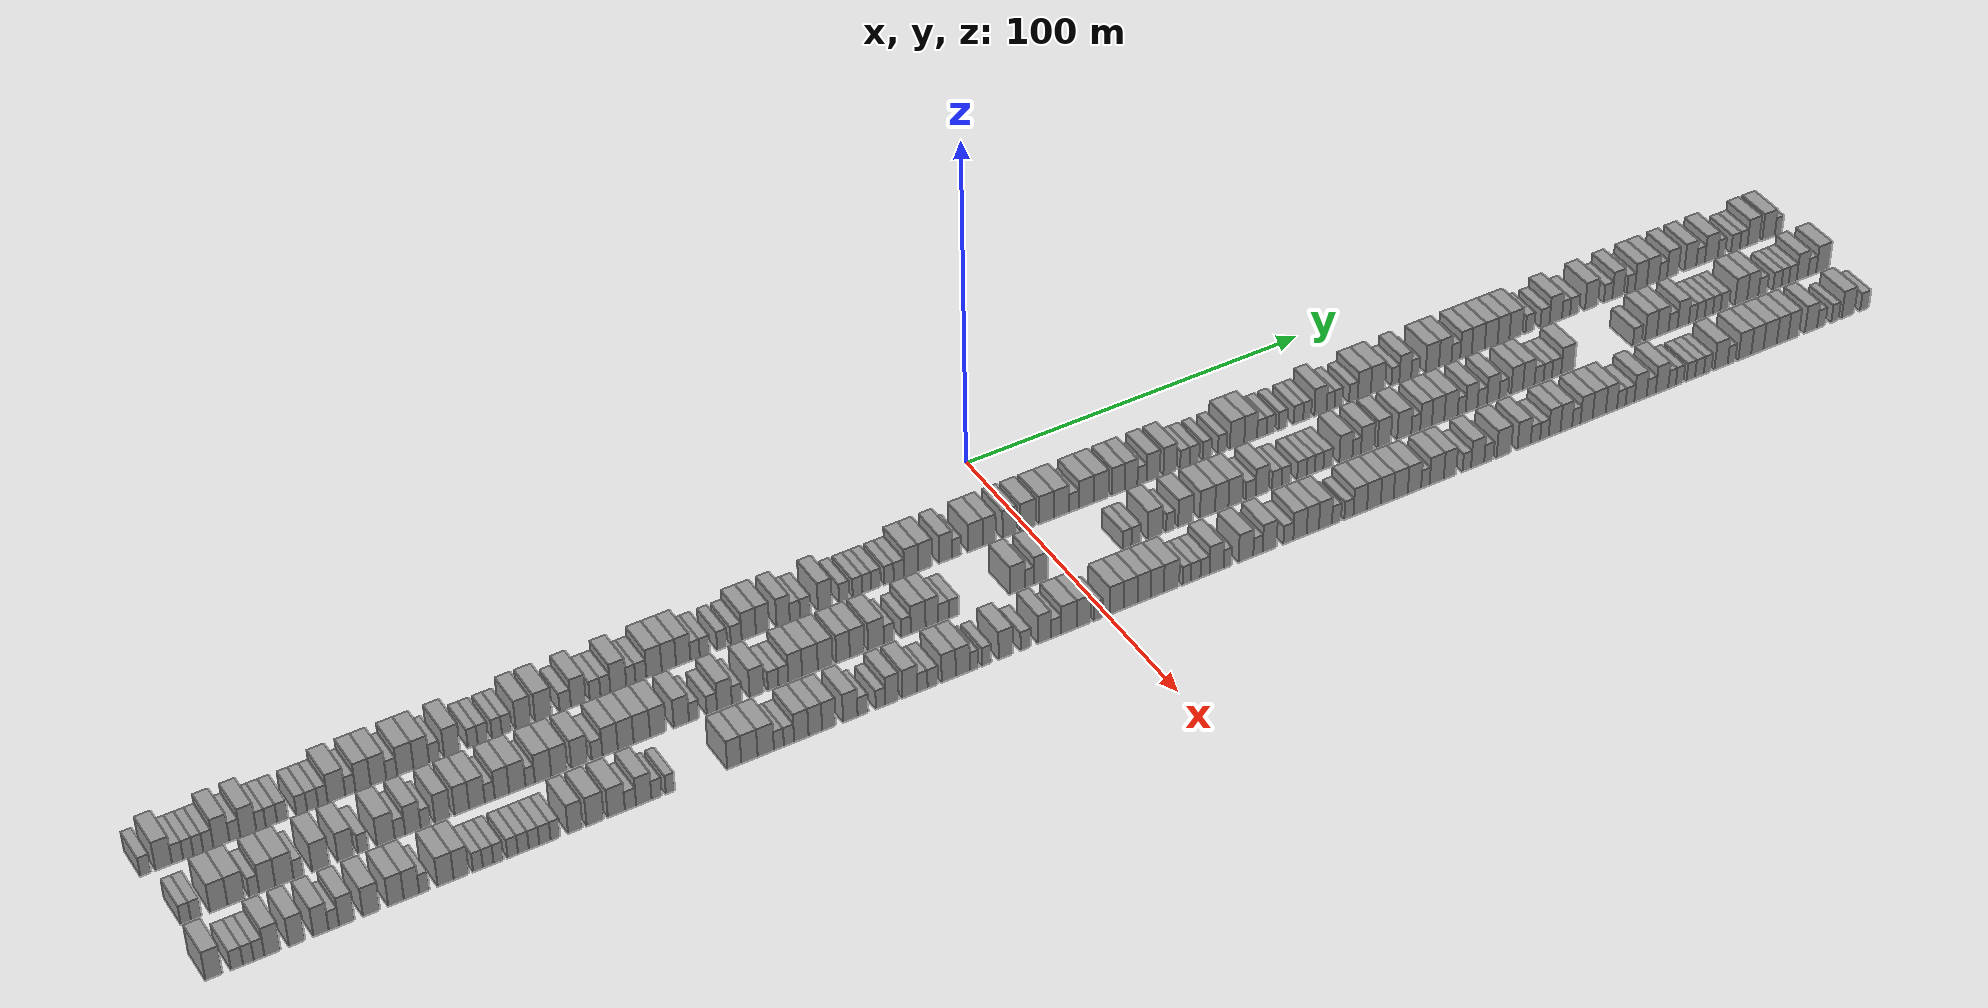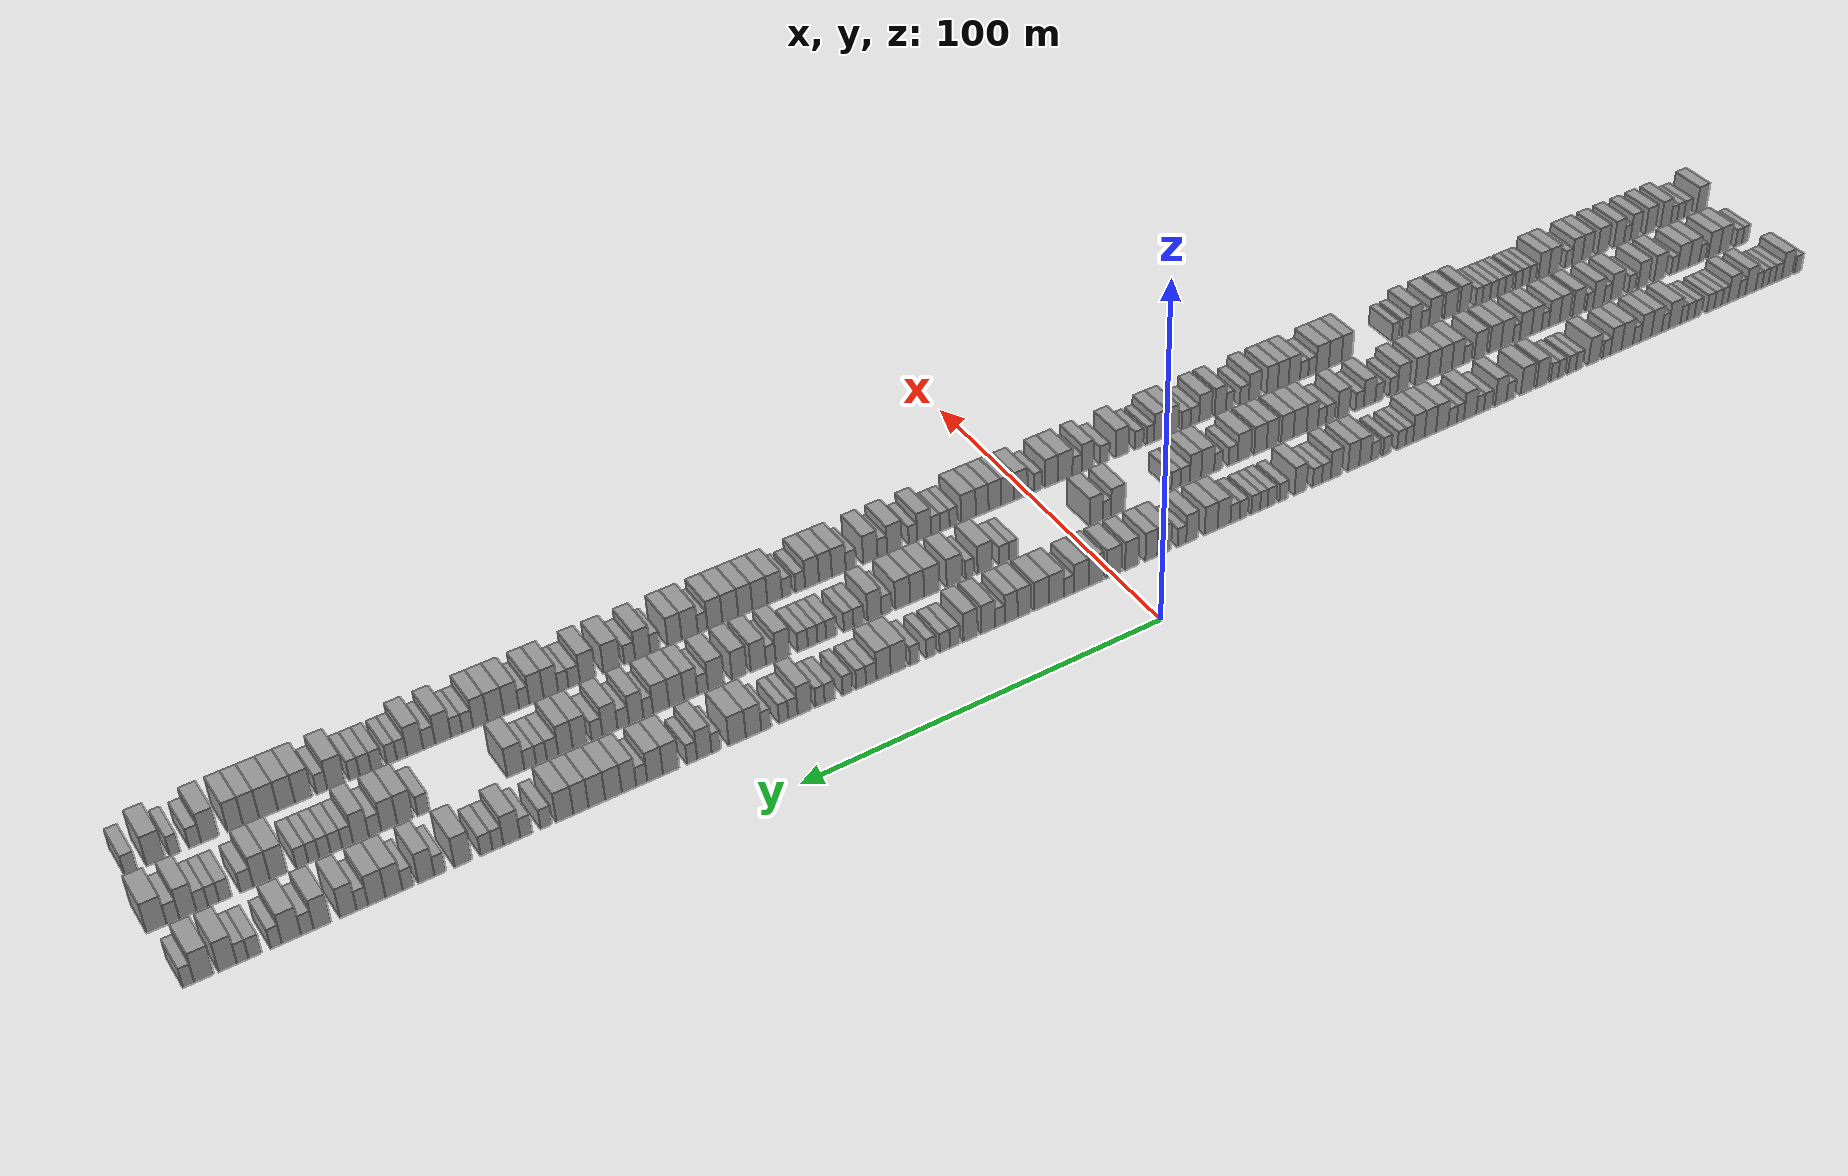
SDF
<sdf version="1.6">
 <world name="default">
  <scene>
   <sky><clouds><speed>12</speed></clouds></sky>
   <ambient>0.4 0.4 0.4 1</ambient>
   <background>0.7 0.7 0.7 1</background>
   <shadows>1</shadows>
  </scene>
  <gravity>0 0 -9.8066</gravity>
  <magnetic_field>6e-06 2.3e-05 -4.2e-05</magnetic_field>
  <physics default="0" name="default_physics" type="ode">
   <ode>
    <solver>
     <type>quick</type>
     <iters>10</iters>
     <sor>1.0</sor>
     <use_dynamic_moi_rescaling>0</use_dynamic_moi_rescaling>
    </solver>
    <constraints>
     <cfm>0</cfm>
     <erp>0.2</erp>
     <contact_max_correcting_vel>100</contact_max_correcting_vel>
     <contact_surface_layer>0.001</contact_surface_layer>
    </constraints>
   </ode>
   <max_step_size>0.004</max_step_size>
   <real_time_factor>1</real_time_factor>
   <real_time_update_rate>250</real_time_update_rate>
  </physics>
  <light name="sun" type="directional">
   <pose>0 0 10 0 0 0</pose>
   <diffuse>0.8 0.8 0.8 1</diffuse>
   <specular>0.2 0.2 0.2 1</specular>
   <attenuation>
    <range>1000</range>
    <constant>0.9</constant>
    <linear>0.01</linear>
    <quadratic>0.001</quadratic>
   </attenuation>
   <direction>-0.5 0.1 -0.9</direction>
  </light>
  <model name="building_1">
   <static>1</static>
   <pose>25.0000 -234.6481 0 0.000000 0.000000 0.000000</pose>
   <link name="link">
    <pose>0 0 3.00 0 0 0</pose>
    <collision name="collision"><geometry><box><size>10.0000 2.7038 6.0000</size></box></geometry></collision>
    <visual name="visual">
     <cast_shadows>0</cast_shadows>
     <geometry><box><size>10.0000 2.7038 6.0000</size></box></geometry>
     <material>
      <script>
       <uri>model://grey_wall/materials/scripts</uri>
       <uri>model://grey_wall/materials/textures</uri>
       <name>vrc/grey_wall</name>
      </script>
     </material>
    </visual>
   </link>
  </model>
  <model name="building_2">
   <static>1</static>
   <pose>25.0000 -230.2623 0 0.000000 0.000000 0.000000</pose>
   <link name="link">
    <pose>0 0 4.50 0 0 0</pose>
    <collision name="collision"><geometry><box><size>10.0000 4.0678 9.0000</size></box></geometry></collision>
    <visual name="visual">
     <cast_shadows>0</cast_shadows>
     <geometry><box><size>10.0000 4.0678 9.0000</size></box></geometry>
     <material>
      <script>
       <uri>model://grey_wall/materials/scripts</uri>
       <uri>model://grey_wall/materials/textures</uri>
       <name>vrc/grey_wall</name>
      </script>
     </material>
    </visual>
   </link>
  </model>
  <model name="building_3">
   <static>1</static>
   <pose>25.0000 -226.8506 0 0.000000 0.000000 0.000000</pose>
   <link name="link">
    <pose>0 0 3.00 0 0 0</pose>
    <collision name="collision"><geometry><box><size>10.0000 2.7557 6.0000</size></box></geometry></collision>
    <visual name="visual">
     <cast_shadows>0</cast_shadows>
     <geometry><box><size>10.0000 2.7557 6.0000</size></box></geometry>
     <material>
      <script>
       <uri>model://grey_wall/materials/scripts</uri>
       <uri>model://grey_wall/materials/textures</uri>
       <name>vrc/grey_wall</name>
      </script>
     </material>
    </visual>
   </link>
  </model>
  <model name="building_4">
   <static>1</static>
   <pose>25.0000 -224.2279 0 0.000000 0.000000 0.000000</pose>
   <link name="link">
    <pose>0 0 3.00 0 0 0</pose>
    <collision name="collision"><geometry><box><size>10.0000 2.4896 6.0000</size></box></geometry></collision>
    <visual name="visual">
     <cast_shadows>0</cast_shadows>
     <geometry><box><size>10.0000 2.4896 6.0000</size></box></geometry>
     <material>
      <script>
       <uri>model://grey_wall/materials/scripts</uri>
       <uri>model://grey_wall/materials/textures</uri>
       <name>vrc/grey_wall</name>
      </script>
     </material>
    </visual>
   </link>
  </model>
  <model name="building_5">
   <static>1</static>
   <pose>25.0000 -221.7675 0 0.000000 0.000000 0.000000</pose>
   <link name="link">
    <pose>0 0 3.00 0 0 0</pose>
    <collision name="collision"><geometry><box><size>10.0000 2.4312 6.0000</size></box></geometry></collision>
    <visual name="visual">
     <cast_shadows>0</cast_shadows>
     <geometry><box><size>10.0000 2.4312 6.0000</size></box></geometry>
     <material>
      <script>
       <uri>model://grey_wall/materials/scripts</uri>
       <uri>model://grey_wall/materials/textures</uri>
       <name>vrc/grey_wall</name>
      </script>
     </material>
    </visual>
   </link>
  </model>
  <model name="building_6">
   <static>1</static>
   <pose>25.0000 -219.2975 0 0.000000 0.000000 0.000000</pose>
   <link name="link">
    <pose>0 0 3.00 0 0 0</pose>
    <collision name="collision"><geometry><box><size>10.0000 2.5089 6.0000</size></box></geometry></collision>
    <visual name="visual">
     <cast_shadows>0</cast_shadows>
     <geometry><box><size>10.0000 2.5089 6.0000</size></box></geometry>
     <material>
      <script>
       <uri>model://grey_wall/materials/scripts</uri>
       <uri>model://grey_wall/materials/textures</uri>
       <name>vrc/grey_wall</name>
      </script>
     </material>
    </visual>
   </link>
  </model>
  <model name="building_7">
   <static>1</static>
   <pose>25.0000 -216.0618 0 0.000000 0.000000 0.000000</pose>
   <link name="link">
    <pose>0 0 4.50 0 0 0</pose>
    <collision name="collision"><geometry><box><size>10.0000 3.9624 9.0000</size></box></geometry></collision>
    <visual name="visual">
     <cast_shadows>0</cast_shadows>
     <geometry><box><size>10.0000 3.9624 9.0000</size></box></geometry>
     <material>
      <script>
       <uri>model://grey_wall/materials/scripts</uri>
       <uri>model://grey_wall/materials/textures</uri>
       <name>vrc/grey_wall</name>
      </script>
     </material>
    </visual>
   </link>
  </model>
  <model name="building_8">
   <static>1</static>
   <pose>25.0000 -212.7326 0 0.000000 0.000000 0.000000</pose>
   <link name="link">
    <pose>0 0 3.00 0 0 0</pose>
    <collision name="collision"><geometry><box><size>10.0000 2.6959 6.0000</size></box></geometry></collision>
    <visual name="visual">
     <cast_shadows>0</cast_shadows>
     <geometry><box><size>10.0000 2.6959 6.0000</size></box></geometry>
     <material>
      <script>
       <uri>model://grey_wall/materials/scripts</uri>
       <uri>model://grey_wall/materials/textures</uri>
       <name>vrc/grey_wall</name>
      </script>
     </material>
    </visual>
   </link>
  </model>
  <model name="building_9">
   <static>1</static>
   <pose>25.0000 -209.4204 0 0.000000 0.000000 0.000000</pose>
   <link name="link">
    <pose>0 0 4.50 0 0 0</pose>
    <collision name="collision"><geometry><box><size>10.0000 3.9286 9.0000</size></box></geometry></collision>
    <visual name="visual">
     <cast_shadows>0</cast_shadows>
     <geometry><box><size>10.0000 3.9286 9.0000</size></box></geometry>
     <material>
      <script>
       <uri>model://grey_wall/materials/scripts</uri>
       <uri>model://grey_wall/materials/textures</uri>
       <name>vrc/grey_wall</name>
      </script>
     </material>
    </visual>
   </link>
  </model>
  <model name="building_10">
   <static>1</static>
   <pose>25.0000 -206.2561 0 0.000000 0.000000 0.000000</pose>
   <link name="link">
    <pose>0 0 3.00 0 0 0</pose>
    <collision name="collision"><geometry><box><size>10.0000 2.4000 6.0000</size></box></geometry></collision>
    <visual name="visual">
     <cast_shadows>0</cast_shadows>
     <geometry><box><size>10.0000 2.4000 6.0000</size></box></geometry>
     <material>
      <script>
       <uri>model://grey_wall/materials/scripts</uri>
       <uri>model://grey_wall/materials/textures</uri>
       <name>vrc/grey_wall</name>
      </script>
     </material>
    </visual>
   </link>
  </model>
  <model name="building_11">
   <static>1</static>
   <pose>25.0000 -203.6401 0 0.000000 0.000000 0.000000</pose>
   <link name="link">
    <pose>0 0 3.00 0 0 0</pose>
    <collision name="collision"><geometry><box><size>10.0000 2.8320 6.0000</size></box></geometry></collision>
    <visual name="visual">
     <cast_shadows>0</cast_shadows>
     <geometry><box><size>10.0000 2.8320 6.0000</size></box></geometry>
     <material>
      <script>
       <uri>model://grey_wall/materials/scripts</uri>
       <uri>model://grey_wall/materials/textures</uri>
       <name>vrc/grey_wall</name>
      </script>
     </material>
    </visual>
   </link>
  </model>
  <model name="building_12">
   <static>1</static>
   <pose>25.0000 -200.8274 0 0.000000 0.000000 0.000000</pose>
   <link name="link">
    <pose>0 0 3.00 0 0 0</pose>
    <collision name="collision"><geometry><box><size>10.0000 2.7935 6.0000</size></box></geometry></collision>
    <visual name="visual">
     <cast_shadows>0</cast_shadows>
     <geometry><box><size>10.0000 2.7935 6.0000</size></box></geometry>
     <material>
      <script>
       <uri>model://grey_wall/materials/scripts</uri>
       <uri>model://grey_wall/materials/textures</uri>
       <name>vrc/grey_wall</name>
      </script>
     </material>
    </visual>
   </link>
  </model>
  <model name="building_13">
   <static>1</static>
   <pose>25.0000 -196.0724 0 0.000000 0.000000 0.000000</pose>
   <link name="link">
    <pose>0 0 3.00 0 0 0</pose>
    <collision name="collision"><geometry><box><size>10.0000 2.7164 6.0000</size></box></geometry></collision>
    <visual name="visual">
     <cast_shadows>0</cast_shadows>
     <geometry><box><size>10.0000 2.7164 6.0000</size></box></geometry>
     <material>
      <script>
       <uri>model://grey_wall/materials/scripts</uri>
       <uri>model://grey_wall/materials/textures</uri>
       <name>vrc/grey_wall</name>
      </script>
     </material>
    </visual>
   </link>
  </model>
  <model name="building_14">
   <static>1</static>
   <pose>25.0000 -193.3266 0 0.000000 0.000000 0.000000</pose>
   <link name="link">
    <pose>0 0 3.00 0 0 0</pose>
    <collision name="collision"><geometry><box><size>10.0000 2.7752 6.0000</size></box></geometry></collision>
    <visual name="visual">
     <cast_shadows>0</cast_shadows>
     <geometry><box><size>10.0000 2.7752 6.0000</size></box></geometry>
     <material>
      <script>
       <uri>model://grey_wall/materials/scripts</uri>
       <uri>model://grey_wall/materials/textures</uri>
       <name>vrc/grey_wall</name>
      </script>
     </material>
    </visual>
   </link>
  </model>
  <model name="building_15">
   <static>1</static>
   <pose>25.0000 -190.7367 0 0.000000 0.000000 0.000000</pose>
   <link name="link">
    <pose>0 0 3.00 0 0 0</pose>
    <collision name="collision"><geometry><box><size>10.0000 2.4047 6.0000</size></box></geometry></collision>
    <visual name="visual">
     <cast_shadows>0</cast_shadows>
     <geometry><box><size>10.0000 2.4047 6.0000</size></box></geometry>
     <material>
      <script>
       <uri>model://grey_wall/materials/scripts</uri>
       <uri>model://grey_wall/materials/textures</uri>
       <name>vrc/grey_wall</name>
      </script>
     </material>
    </visual>
   </link>
  </model>
  <model name="building_16">
   <static>1</static>
   <pose>25.0000 -187.3054 0 0.000000 0.000000 0.000000</pose>
   <link name="link">
    <pose>0 0 4.50 0 0 0</pose>
    <collision name="collision"><geometry><box><size>10.0000 4.4580 9.0000</size></box></geometry></collision>
    <visual name="visual">
     <cast_shadows>0</cast_shadows>
     <geometry><box><size>10.0000 4.4580 9.0000</size></box></geometry>
     <material>
      <script>
       <uri>model://grey_wall/materials/scripts</uri>
       <uri>model://grey_wall/materials/textures</uri>
       <name>vrc/grey_wall</name>
      </script>
     </material>
    </visual>
   </link>
  </model>
  <model name="building_17">
   <static>1</static>
   <pose>25.0000 -183.7864 0 0.000000 0.000000 0.000000</pose>
   <link name="link">
    <pose>0 0 3.00 0 0 0</pose>
    <collision name="collision"><geometry><box><size>10.0000 2.5800 6.0000</size></box></geometry></collision>
    <visual name="visual">
     <cast_shadows>0</cast_shadows>
     <geometry><box><size>10.0000 2.5800 6.0000</size></box></geometry>
     <material>
      <script>
       <uri>model://grey_wall/materials/scripts</uri>
       <uri>model://grey_wall/materials/textures</uri>
       <name>vrc/grey_wall</name>
      </script>
     </material>
    </visual>
   </link>
  </model>
  <model name="building_18">
   <static>1</static>
   <pose>25.0000 -180.5809 0 0.000000 0.000000 0.000000</pose>
   <link name="link">
    <pose>0 0 4.50 0 0 0</pose>
    <collision name="collision"><geometry><box><size>10.0000 3.8311 9.0000</size></box></geometry></collision>
    <visual name="visual">
     <cast_shadows>0</cast_shadows>
     <geometry><box><size>10.0000 3.8311 9.0000</size></box></geometry>
     <material>
      <script>
       <uri>model://grey_wall/materials/scripts</uri>
       <uri>model://grey_wall/materials/textures</uri>
       <name>vrc/grey_wall</name>
      </script>
     </material>
    </visual>
   </link>
  </model>
  <model name="building_19">
   <static>1</static>
   <pose>25.0000 -176.6732 0 0.000000 0.000000 0.000000</pose>
   <link name="link">
    <pose>0 0 4.50 0 0 0</pose>
    <collision name="collision"><geometry><box><size>10.0000 3.9841 9.0000</size></box></geometry></collision>
    <visual name="visual">
     <cast_shadows>0</cast_shadows>
     <geometry><box><size>10.0000 3.9841 9.0000</size></box></geometry>
     <material>
      <script>
       <uri>model://grey_wall/materials/scripts</uri>
       <uri>model://grey_wall/materials/textures</uri>
       <name>vrc/grey_wall</name>
      </script>
     </material>
    </visual>
   </link>
  </model>
  <model name="building_20">
   <static>1</static>
   <pose>25.0000 -173.2971 0 0.000000 0.000000 0.000000</pose>
   <link name="link">
    <pose>0 0 3.00 0 0 0</pose>
    <collision name="collision"><geometry><box><size>10.0000 2.7682 6.0000</size></box></geometry></collision>
    <visual name="visual">
     <cast_shadows>0</cast_shadows>
     <geometry><box><size>10.0000 2.7682 6.0000</size></box></geometry>
     <material>
      <script>
       <uri>model://grey_wall/materials/scripts</uri>
       <uri>model://grey_wall/materials/textures</uri>
       <name>vrc/grey_wall</name>
      </script>
     </material>
    </visual>
   </link>
  </model>
  <model name="building_21">
   <static>1</static>
   <pose>25.0000 -169.8060 0 0.000000 0.000000 0.000000</pose>
   <link name="link">
    <pose>0 0 4.50 0 0 0</pose>
    <collision name="collision"><geometry><box><size>10.0000 4.2139 9.0000</size></box></geometry></collision>
    <visual name="visual">
     <cast_shadows>0</cast_shadows>
     <geometry><box><size>10.0000 4.2139 9.0000</size></box></geometry>
     <material>
      <script>
       <uri>model://grey_wall/materials/scripts</uri>
       <uri>model://grey_wall/materials/textures</uri>
       <name>vrc/grey_wall</name>
      </script>
     </material>
    </visual>
   </link>
  </model>
  <model name="building_22">
   <static>1</static>
   <pose>25.0000 -165.6899 0 0.000000 0.000000 0.000000</pose>
   <link name="link">
    <pose>0 0 4.50 0 0 0</pose>
    <collision name="collision"><geometry><box><size>10.0000 4.0185 9.0000</size></box></geometry></collision>
    <visual name="visual">
     <cast_shadows>0</cast_shadows>
     <geometry><box><size>10.0000 4.0185 9.0000</size></box></geometry>
     <material>
      <script>
       <uri>model://grey_wall/materials/scripts</uri>
       <uri>model://grey_wall/materials/textures</uri>
       <name>vrc/grey_wall</name>
      </script>
     </material>
    </visual>
   </link>
  </model>
  <model name="building_23">
   <static>1</static>
   <pose>25.0000 -162.2572 0 0.000000 0.000000 0.000000</pose>
   <link name="link">
    <pose>0 0 3.00 0 0 0</pose>
    <collision name="collision"><geometry><box><size>10.0000 2.8468 6.0000</size></box></geometry></collision>
    <visual name="visual">
     <cast_shadows>0</cast_shadows>
     <geometry><box><size>10.0000 2.8468 6.0000</size></box></geometry>
     <material>
      <script>
       <uri>model://grey_wall/materials/scripts</uri>
       <uri>model://grey_wall/materials/textures</uri>
       <name>vrc/grey_wall</name>
      </script>
     </material>
    </visual>
   </link>
  </model>
  <model name="building_24">
   <static>1</static>
   <pose>25.0000 -157.7690 0 0.000000 0.000000 0.000000</pose>
   <link name="link">
    <pose>0 0 4.50 0 0 0</pose>
    <collision name="collision"><geometry><box><size>10.0000 4.1296 9.0000</size></box></geometry></collision>
    <visual name="visual">
     <cast_shadows>0</cast_shadows>
     <geometry><box><size>10.0000 4.1296 9.0000</size></box></geometry>
     <material>
      <script>
       <uri>model://grey_wall/materials/scripts</uri>
       <uri>model://grey_wall/materials/textures</uri>
       <name>vrc/grey_wall</name>
      </script>
     </material>
    </visual>
   </link>
  </model>
  <model name="building_25">
   <static>1</static>
   <pose>25.0000 -152.4329 0 0.000000 0.000000 0.000000</pose>
   <link name="link">
    <pose>0 0 3.00 0 0 0</pose>
    <collision name="collision"><geometry><box><size>10.0000 2.5426 6.0000</size></box></geometry></collision>
    <visual name="visual">
     <cast_shadows>0</cast_shadows>
     <geometry><box><size>10.0000 2.5426 6.0000</size></box></geometry>
     <material>
      <script>
       <uri>model://grey_wall/materials/scripts</uri>
       <uri>model://grey_wall/materials/textures</uri>
       <name>vrc/grey_wall</name>
      </script>
     </material>
    </visual>
   </link>
  </model>
  <model name="building_26">
   <static>1</static>
   <pose>25.0000 -149.7893 0 0.000000 0.000000 0.000000</pose>
   <link name="link">
    <pose>0 0 3.00 0 0 0</pose>
    <collision name="collision"><geometry><box><size>10.0000 2.7446 6.0000</size></box></geometry></collision>
    <visual name="visual">
     <cast_shadows>0</cast_shadows>
     <geometry><box><size>10.0000 2.7446 6.0000</size></box></geometry>
     <material>
      <script>
       <uri>model://grey_wall/materials/scripts</uri>
       <uri>model://grey_wall/materials/textures</uri>
       <name>vrc/grey_wall</name>
      </script>
     </material>
    </visual>
   </link>
  </model>
  <model name="building_27">
   <static>1</static>
   <pose>25.0000 -146.1380 0 0.000000 0.000000 0.000000</pose>
   <link name="link">
    <pose>0 0 3.00 0 0 0</pose>
    <collision name="collision"><geometry><box><size>10.0000 2.5580 6.0000</size></box></geometry></collision>
    <visual name="visual">
     <cast_shadows>0</cast_shadows>
     <geometry><box><size>10.0000 2.5580 6.0000</size></box></geometry>
     <material>
      <script>
       <uri>model://grey_wall/materials/scripts</uri>
       <uri>model://grey_wall/materials/textures</uri>
       <name>vrc/grey_wall</name>
      </script>
     </material>
    </visual>
   </link>
  </model>
  <model name="building_28">
   <static>1</static>
   <pose>25.0000 -143.5564 0 0.000000 0.000000 0.000000</pose>
   <link name="link">
    <pose>0 0 3.00 0 0 0</pose>
    <collision name="collision"><geometry><box><size>10.0000 2.6051 6.0000</size></box></geometry></collision>
    <visual name="visual">
     <cast_shadows>0</cast_shadows>
     <geometry><box><size>10.0000 2.6051 6.0000</size></box></geometry>
     <material>
      <script>
       <uri>model://grey_wall/materials/scripts</uri>
       <uri>model://grey_wall/materials/textures</uri>
       <name>vrc/grey_wall</name>
      </script>
     </material>
    </visual>
   </link>
  </model>
  <model name="building_29">
   <static>1</static>
   <pose>25.0000 -139.2186 0 0.000000 0.000000 0.000000</pose>
   <link name="link">
    <pose>0 0 4.50 0 0 0</pose>
    <collision name="collision"><geometry><box><size>10.0000 4.0704 9.0000</size></box></geometry></collision>
    <visual name="visual">
     <cast_shadows>0</cast_shadows>
     <geometry><box><size>10.0000 4.0704 9.0000</size></box></geometry>
     <material>
      <script>
       <uri>model://grey_wall/materials/scripts</uri>
       <uri>model://grey_wall/materials/textures</uri>
       <name>vrc/grey_wall</name>
      </script>
     </material>
    </visual>
   </link>
  </model>
  <model name="building_30">
   <static>1</static>
   <pose>25.0000 -133.9359 0 0.000000 0.000000 0.000000</pose>
   <link name="link">
    <pose>0 0 4.50 0 0 0</pose>
    <collision name="collision"><geometry><box><size>10.0000 4.4950 9.0000</size></box></geometry></collision>
    <visual name="visual">
     <cast_shadows>0</cast_shadows>
     <geometry><box><size>10.0000 4.4950 9.0000</size></box></geometry>
     <material>
      <script>
       <uri>model://grey_wall/materials/scripts</uri>
       <uri>model://grey_wall/materials/textures</uri>
       <name>vrc/grey_wall</name>
      </script>
     </material>
    </visual>
   </link>
  </model>
  <model name="building_31">
   <static>1</static>
   <pose>25.0000 -128.1968 0 0.000000 0.000000 0.000000</pose>
   <link name="link">
    <pose>0 0 3.00 0 0 0</pose>
    <collision name="collision"><geometry><box><size>10.0000 2.9834 6.0000</size></box></geometry></collision>
    <visual name="visual">
     <cast_shadows>0</cast_shadows>
     <geometry><box><size>10.0000 2.9834 6.0000</size></box></geometry>
     <material>
      <script>
       <uri>model://grey_wall/materials/scripts</uri>
       <uri>model://grey_wall/materials/textures</uri>
       <name>vrc/grey_wall</name>
      </script>
     </material>
    </visual>
   </link>
  </model>
  <model name="building_32">
   <static>1</static>
   <pose>25.0000 -124.7177 0 0.000000 0.000000 0.000000</pose>
   <link name="link">
    <pose>0 0 4.50 0 0 0</pose>
    <collision name="collision"><geometry><box><size>10.0000 3.9747 9.0000</size></box></geometry></collision>
    <visual name="visual">
     <cast_shadows>0</cast_shadows>
     <geometry><box><size>10.0000 3.9747 9.0000</size></box></geometry>
     <material>
      <script>
       <uri>model://grey_wall/materials/scripts</uri>
       <uri>model://grey_wall/materials/textures</uri>
       <name>vrc/grey_wall</name>
      </script>
     </material>
    </visual>
   </link>
  </model>
  <model name="building_33">
   <static>1</static>
   <pose>25.0000 -120.3005 0 0.000000 0.000000 0.000000</pose>
   <link name="link">
    <pose>0 0 3.00 0 0 0</pose>
    <collision name="collision"><geometry><box><size>10.0000 2.8597 6.0000</size></box></geometry></collision>
    <visual name="visual">
     <cast_shadows>0</cast_shadows>
     <geometry><box><size>10.0000 2.8597 6.0000</size></box></geometry>
     <material>
      <script>
       <uri>model://grey_wall/materials/scripts</uri>
       <uri>model://grey_wall/materials/textures</uri>
       <name>vrc/grey_wall</name>
      </script>
     </material>
    </visual>
   </link>
  </model>
  <model name="building_34">
   <static>1</static>
   <pose>25.0000 -117.5436 0 0.000000 0.000000 0.000000</pose>
   <link name="link">
    <pose>0 0 3.00 0 0 0</pose>
    <collision name="collision"><geometry><box><size>10.0000 2.6541 6.0000</size></box></geometry></collision>
    <visual name="visual">
     <cast_shadows>0</cast_shadows>
     <geometry><box><size>10.0000 2.6541 6.0000</size></box></geometry>
     <material>
      <script>
       <uri>model://grey_wall/materials/scripts</uri>
       <uri>model://grey_wall/materials/textures</uri>
       <name>vrc/grey_wall</name>
      </script>
     </material>
    </visual>
   </link>
  </model>
  <model name="building_35">
   <static>1</static>
   <pose>25.0000 -114.0958 0 0.000000 0.000000 0.000000</pose>
   <link name="link">
    <pose>0 0 4.50 0 0 0</pose>
    <collision name="collision"><geometry><box><size>10.0000 4.2415 9.0000</size></box></geometry></collision>
    <visual name="visual">
     <cast_shadows>0</cast_shadows>
     <geometry><box><size>10.0000 4.2415 9.0000</size></box></geometry>
     <material>
      <script>
       <uri>model://grey_wall/materials/scripts</uri>
       <uri>model://grey_wall/materials/textures</uri>
       <name>vrc/grey_wall</name>
      </script>
     </material>
    </visual>
   </link>
  </model>
  <model name="building_36">
   <static>1</static>
   <pose>25.0000 -110.7415 0 0.000000 0.000000 0.000000</pose>
   <link name="link">
    <pose>0 0 3.00 0 0 0</pose>
    <collision name="collision"><geometry><box><size>10.0000 2.4672 6.0000</size></box></geometry></collision>
    <visual name="visual">
     <cast_shadows>0</cast_shadows>
     <geometry><box><size>10.0000 2.4672 6.0000</size></box></geometry>
     <material>
      <script>
       <uri>model://grey_wall/materials/scripts</uri>
       <uri>model://grey_wall/materials/textures</uri>
       <name>vrc/grey_wall</name>
      </script>
     </material>
    </visual>
   </link>
  </model>
  <model name="building_37">
   <static>1</static>
   <pose>25.0000 -108.0367 0 0.000000 0.000000 0.000000</pose>
   <link name="link">
    <pose>0 0 3.00 0 0 0</pose>
    <collision name="collision"><geometry><box><size>10.0000 2.9423 6.0000</size></box></geometry></collision>
    <visual name="visual">
     <cast_shadows>0</cast_shadows>
     <geometry><box><size>10.0000 2.9423 6.0000</size></box></geometry>
     <material>
      <script>
       <uri>model://grey_wall/materials/scripts</uri>
       <uri>model://grey_wall/materials/textures</uri>
       <name>vrc/grey_wall</name>
      </script>
     </material>
    </visual>
   </link>
  </model>
  <model name="building_38">
   <static>1</static>
   <pose>25.0000 -104.5135 0 0.000000 0.000000 0.000000</pose>
   <link name="link">
    <pose>0 0 4.50 0 0 0</pose>
    <collision name="collision"><geometry><box><size>10.0000 4.1042 9.0000</size></box></geometry></collision>
    <visual name="visual">
     <cast_shadows>0</cast_shadows>
     <geometry><box><size>10.0000 4.1042 9.0000</size></box></geometry>
     <material>
      <script>
       <uri>model://grey_wall/materials/scripts</uri>
       <uri>model://grey_wall/materials/textures</uri>
       <name>vrc/grey_wall</name>
      </script>
     </material>
    </visual>
   </link>
  </model>
  <model name="building_39">
   <static>1</static>
   <pose>25.0000 -100.5276 0 0.000000 0.000000 0.000000</pose>
   <link name="link">
    <pose>0 0 4.50 0 0 0</pose>
    <collision name="collision"><geometry><box><size>10.0000 3.8674 9.0000</size></box></geometry></collision>
    <visual name="visual">
     <cast_shadows>0</cast_shadows>
     <geometry><box><size>10.0000 3.8674 9.0000</size></box></geometry>
     <material>
      <script>
       <uri>model://grey_wall/materials/scripts</uri>
       <uri>model://grey_wall/materials/textures</uri>
       <name>vrc/grey_wall</name>
      </script>
     </material>
    </visual>
   </link>
  </model>
  <model name="building_40">
   <static>1</static>
   <pose>25.0000 -96.6543 0 0.000000 0.000000 0.000000</pose>
   <link name="link">
    <pose>0 0 4.50 0 0 0</pose>
    <collision name="collision"><geometry><box><size>10.0000 3.8792 9.0000</size></box></geometry></collision>
    <visual name="visual">
     <cast_shadows>0</cast_shadows>
     <geometry><box><size>10.0000 3.8792 9.0000</size></box></geometry>
     <material>
      <script>
       <uri>model://grey_wall/materials/scripts</uri>
       <uri>model://grey_wall/materials/textures</uri>
       <name>vrc/grey_wall</name>
      </script>
     </material>
    </visual>
   </link>
  </model>
  <model name="building_41">
   <static>1</static>
   <pose>25.0000 -93.4547 0 0.000000 0.000000 0.000000</pose>
   <link name="link">
    <pose>0 0 3.00 0 0 0</pose>
    <collision name="collision"><geometry><box><size>10.0000 2.5201 6.0000</size></box></geometry></collision>
    <visual name="visual">
     <cast_shadows>0</cast_shadows>
     <geometry><box><size>10.0000 2.5201 6.0000</size></box></geometry>
     <material>
      <script>
       <uri>model://grey_wall/materials/scripts</uri>
       <uri>model://grey_wall/materials/textures</uri>
       <name>vrc/grey_wall</name>
      </script>
     </material>
    </visual>
   </link>
  </model>
  <model name="building_42">
   <static>1</static>
   <pose>25.0000 -90.8179 0 0.000000 0.000000 0.000000</pose>
   <link name="link">
    <pose>0 0 3.00 0 0 0</pose>
    <collision name="collision"><geometry><box><size>10.0000 2.7535 6.0000</size></box></geometry></collision>
    <visual name="visual">
     <cast_shadows>0</cast_shadows>
     <geometry><box><size>10.0000 2.7535 6.0000</size></box></geometry>
     <material>
      <script>
       <uri>model://grey_wall/materials/scripts</uri>
       <uri>model://grey_wall/materials/textures</uri>
       <name>vrc/grey_wall</name>
      </script>
     </material>
    </visual>
   </link>
  </model>
  <model name="building_43">
   <static>1</static>
   <pose>25.0000 -86.0773 0 0.000000 0.000000 0.000000</pose>
   <link name="link">
    <pose>0 0 3.00 0 0 0</pose>
    <collision name="collision"><geometry><box><size>10.0000 2.7277 6.0000</size></box></geometry></collision>
    <visual name="visual">
     <cast_shadows>0</cast_shadows>
     <geometry><box><size>10.0000 2.7277 6.0000</size></box></geometry>
     <material>
      <script>
       <uri>model://grey_wall/materials/scripts</uri>
       <uri>model://grey_wall/materials/textures</uri>
       <name>vrc/grey_wall</name>
      </script>
     </material>
    </visual>
   </link>
  </model>
  <model name="building_44">
   <static>1</static>
   <pose>25.0000 -82.2348 0 0.000000 0.000000 0.000000</pose>
   <link name="link">
    <pose>0 0 3.00 0 0 0</pose>
    <collision name="collision"><geometry><box><size>10.0000 2.9574 6.0000</size></box></geometry></collision>
    <visual name="visual">
     <cast_shadows>0</cast_shadows>
     <geometry><box><size>10.0000 2.9574 6.0000</size></box></geometry>
     <material>
      <script>
       <uri>model://grey_wall/materials/scripts</uri>
       <uri>model://grey_wall/materials/textures</uri>
       <name>vrc/grey_wall</name>
      </script>
     </material>
    </visual>
   </link>
  </model>
  <model name="building_45">
   <static>1</static>
   <pose>25.0000 -78.7970 0 0.000000 0.000000 0.000000</pose>
   <link name="link">
    <pose>0 0 4.50 0 0 0</pose>
    <collision name="collision"><geometry><box><size>10.0000 3.9181 9.0000</size></box></geometry></collision>
    <visual name="visual">
     <cast_shadows>0</cast_shadows>
     <geometry><box><size>10.0000 3.9181 9.0000</size></box></geometry>
     <material>
      <script>
       <uri>model://grey_wall/materials/scripts</uri>
       <uri>model://grey_wall/materials/textures</uri>
       <name>vrc/grey_wall</name>
      </script>
     </material>
    </visual>
   </link>
  </model>
  <model name="building_46">
   <static>1</static>
   <pose>25.0000 -74.9980 0 0.000000 0.000000 0.000000</pose>
   <link name="link">
    <pose>0 0 4.50 0 0 0</pose>
    <collision name="collision"><geometry><box><size>10.0000 3.6799 9.0000</size></box></geometry></collision>
    <visual name="visual">
     <cast_shadows>0</cast_shadows>
     <geometry><box><size>10.0000 3.6799 9.0000</size></box></geometry>
     <material>
      <script>
       <uri>model://grey_wall/materials/scripts</uri>
       <uri>model://grey_wall/materials/textures</uri>
       <name>vrc/grey_wall</name>
      </script>
     </material>
    </visual>
   </link>
  </model>
  <model name="building_47">
   <static>1</static>
   <pose>25.0000 -69.3368 0 0.000000 0.000000 0.000000</pose>
   <link name="link">
    <pose>0 0 4.50 0 0 0</pose>
    <collision name="collision"><geometry><box><size>10.0000 3.6425 9.0000</size></box></geometry></collision>
    <visual name="visual">
     <cast_shadows>0</cast_shadows>
     <geometry><box><size>10.0000 3.6425 9.0000</size></box></geometry>
     <material>
      <script>
       <uri>model://grey_wall/materials/scripts</uri>
       <uri>model://grey_wall/materials/textures</uri>
       <name>vrc/grey_wall</name>
      </script>
     </material>
    </visual>
   </link>
  </model>
  <model name="building_48">
   <static>1</static>
   <pose>25.0000 -66.0858 0 0.000000 0.000000 0.000000</pose>
   <link name="link">
    <pose>0 0 3.00 0 0 0</pose>
    <collision name="collision"><geometry><box><size>10.0000 2.8594 6.0000</size></box></geometry></collision>
    <visual name="visual">
     <cast_shadows>0</cast_shadows>
     <geometry><box><size>10.0000 2.8594 6.0000</size></box></geometry>
     <material>
      <script>
       <uri>model://grey_wall/materials/scripts</uri>
       <uri>model://grey_wall/materials/textures</uri>
       <name>vrc/grey_wall</name>
      </script>
     </material>
    </visual>
   </link>
  </model>
  <model name="building_49">
   <static>1</static>
   <pose>25.0000 -63.1796 0 0.000000 0.000000 0.000000</pose>
   <link name="link">
    <pose>0 0 3.00 0 0 0</pose>
    <collision name="collision"><geometry><box><size>10.0000 2.9530 6.0000</size></box></geometry></collision>
    <visual name="visual">
     <cast_shadows>0</cast_shadows>
     <geometry><box><size>10.0000 2.9530 6.0000</size></box></geometry>
     <material>
      <script>
       <uri>model://grey_wall/materials/scripts</uri>
       <uri>model://grey_wall/materials/textures</uri>
       <name>vrc/grey_wall</name>
      </script>
     </material>
    </visual>
   </link>
  </model>
  <model name="building_50">
   <static>1</static>
   <pose>25.0000 -57.7720 0 0.000000 0.000000 0.000000</pose>
   <link name="link">
    <pose>0 0 4.50 0 0 0</pose>
    <collision name="collision"><geometry><box><size>10.0000 3.8622 9.0000</size></box></geometry></collision>
    <visual name="visual">
     <cast_shadows>0</cast_shadows>
     <geometry><box><size>10.0000 3.8622 9.0000</size></box></geometry>
     <material>
      <script>
       <uri>model://grey_wall/materials/scripts</uri>
       <uri>model://grey_wall/materials/textures</uri>
       <name>vrc/grey_wall</name>
      </script>
     </material>
    </visual>
   </link>
  </model>
  <model name="building_51">
   <static>1</static>
   <pose>25.0000 -52.4273 0 0.000000 0.000000 0.000000</pose>
   <link name="link">
    <pose>0 0 3.00 0 0 0</pose>
    <collision name="collision"><geometry><box><size>10.0000 2.8271 6.0000</size></box></geometry></collision>
    <visual name="visual">
     <cast_shadows>0</cast_shadows>
     <geometry><box><size>10.0000 2.8271 6.0000</size></box></geometry>
     <material>
      <script>
       <uri>model://grey_wall/materials/scripts</uri>
       <uri>model://grey_wall/materials/textures</uri>
       <name>vrc/grey_wall</name>
      </script>
     </material>
    </visual>
   </link>
  </model>
  <model name="building_52">
   <static>1</static>
   <pose>25.0000 -48.6462 0 0.000000 0.000000 0.000000</pose>
   <link name="link">
    <pose>0 0 3.00 0 0 0</pose>
    <collision name="collision"><geometry><box><size>10.0000 2.7351 6.0000</size></box></geometry></collision>
    <visual name="visual">
     <cast_shadows>0</cast_shadows>
     <geometry><box><size>10.0000 2.7351 6.0000</size></box></geometry>
     <material>
      <script>
       <uri>model://grey_wall/materials/scripts</uri>
       <uri>model://grey_wall/materials/textures</uri>
       <name>vrc/grey_wall</name>
      </script>
     </material>
    </visual>
   </link>
  </model>
  <model name="building_53">
   <static>1</static>
   <pose>25.0000 -46.0753 0 0.000000 0.000000 0.000000</pose>
   <link name="link">
    <pose>0 0 3.00 0 0 0</pose>
    <collision name="collision"><geometry><box><size>10.0000 2.4067 6.0000</size></box></geometry></collision>
    <visual name="visual">
     <cast_shadows>0</cast_shadows>
     <geometry><box><size>10.0000 2.4067 6.0000</size></box></geometry>
     <material>
      <script>
       <uri>model://grey_wall/materials/scripts</uri>
       <uri>model://grey_wall/materials/textures</uri>
       <name>vrc/grey_wall</name>
      </script>
     </material>
    </visual>
   </link>
  </model>
  <model name="building_54">
   <static>1</static>
   <pose>25.0000 -43.4868 0 0.000000 0.000000 0.000000</pose>
   <link name="link">
    <pose>0 0 3.00 0 0 0</pose>
    <collision name="collision"><geometry><box><size>10.0000 2.7703 6.0000</size></box></geometry></collision>
    <visual name="visual">
     <cast_shadows>0</cast_shadows>
     <geometry><box><size>10.0000 2.7703 6.0000</size></box></geometry>
     <material>
      <script>
       <uri>model://grey_wall/materials/scripts</uri>
       <uri>model://grey_wall/materials/textures</uri>
       <name>vrc/grey_wall</name>
      </script>
     </material>
    </visual>
   </link>
  </model>
  <model name="building_55">
   <static>1</static>
   <pose>25.0000 -39.7792 0 0.000000 0.000000 0.000000</pose>
   <link name="link">
    <pose>0 0 3.00 0 0 0</pose>
    <collision name="collision"><geometry><box><size>10.0000 2.6449 6.0000</size></box></geometry></collision>
    <visual name="visual">
     <cast_shadows>0</cast_shadows>
     <geometry><box><size>10.0000 2.6449 6.0000</size></box></geometry>
     <material>
      <script>
       <uri>model://grey_wall/materials/scripts</uri>
       <uri>model://grey_wall/materials/textures</uri>
       <name>vrc/grey_wall</name>
      </script>
     </material>
    </visual>
   </link>
  </model>
  <model name="building_56">
   <static>1</static>
   <pose>25.0000 -36.9956 0 0.000000 0.000000 0.000000</pose>
   <link name="link">
    <pose>0 0 3.00 0 0 0</pose>
    <collision name="collision"><geometry><box><size>10.0000 2.9223 6.0000</size></box></geometry></collision>
    <visual name="visual">
     <cast_shadows>0</cast_shadows>
     <geometry><box><size>10.0000 2.9223 6.0000</size></box></geometry>
     <material>
      <script>
       <uri>model://grey_wall/materials/scripts</uri>
       <uri>model://grey_wall/materials/textures</uri>
       <name>vrc/grey_wall</name>
      </script>
     </material>
    </visual>
   </link>
  </model>
  <model name="building_57">
   <static>1</static>
   <pose>25.0000 -33.5493 0 0.000000 0.000000 0.000000</pose>
   <link name="link">
    <pose>0 0 4.50 0 0 0</pose>
    <collision name="collision"><geometry><box><size>10.0000 3.9704 9.0000</size></box></geometry></collision>
    <visual name="visual">
     <cast_shadows>0</cast_shadows>
     <geometry><box><size>10.0000 3.9704 9.0000</size></box></geometry>
     <material>
      <script>
       <uri>model://grey_wall/materials/scripts</uri>
       <uri>model://grey_wall/materials/textures</uri>
       <name>vrc/grey_wall</name>
      </script>
     </material>
    </visual>
   </link>
  </model>
  <model name="building_58">
   <static>1</static>
   <pose>25.0000 -29.5604 0 0.000000 0.000000 0.000000</pose>
   <link name="link">
    <pose>0 0 4.50 0 0 0</pose>
    <collision name="collision"><geometry><box><size>10.0000 4.0074 9.0000</size></box></geometry></collision>
    <visual name="visual">
     <cast_shadows>0</cast_shadows>
     <geometry><box><size>10.0000 4.0074 9.0000</size></box></geometry>
     <material>
      <script>
       <uri>model://grey_wall/materials/scripts</uri>
       <uri>model://grey_wall/materials/textures</uri>
       <name>vrc/grey_wall</name>
      </script>
     </material>
    </visual>
   </link>
  </model>
  <model name="building_59">
   <static>1</static>
   <pose>25.0000 -23.6987 0 0.000000 0.000000 0.000000</pose>
   <link name="link">
    <pose>0 0 4.50 0 0 0</pose>
    <collision name="collision"><geometry><box><size>10.0000 3.7161 9.0000</size></box></geometry></collision>
    <visual name="visual">
     <cast_shadows>0</cast_shadows>
     <geometry><box><size>10.0000 3.7161 9.0000</size></box></geometry>
     <material>
      <script>
       <uri>model://grey_wall/materials/scripts</uri>
       <uri>model://grey_wall/materials/textures</uri>
       <name>vrc/grey_wall</name>
      </script>
     </material>
    </visual>
   </link>
  </model>
  <model name="building_60">
   <static>1</static>
   <pose>25.0000 -20.5295 0 0.000000 0.000000 0.000000</pose>
   <link name="link">
    <pose>0 0 3.00 0 0 0</pose>
    <collision name="collision"><geometry><box><size>10.0000 2.6221 6.0000</size></box></geometry></collision>
    <visual name="visual">
     <cast_shadows>0</cast_shadows>
     <geometry><box><size>10.0000 2.6221 6.0000</size></box></geometry>
     <material>
      <script>
       <uri>model://grey_wall/materials/scripts</uri>
       <uri>model://grey_wall/materials/textures</uri>
       <name>vrc/grey_wall</name>
      </script>
     </material>
    </visual>
   </link>
  </model>
  <model name="building_61">
   <static>1</static>
   <pose>25.0000 -15.1190 0 0.000000 0.000000 0.000000</pose>
   <link name="link">
    <pose>0 0 4.50 0 0 0</pose>
    <collision name="collision"><geometry><box><size>10.0000 4.1989 9.0000</size></box></geometry></collision>
    <visual name="visual">
     <cast_shadows>0</cast_shadows>
     <geometry><box><size>10.0000 4.1989 9.0000</size></box></geometry>
     <material>
      <script>
       <uri>model://grey_wall/materials/scripts</uri>
       <uri>model://grey_wall/materials/textures</uri>
       <name>vrc/grey_wall</name>
      </script>
     </material>
    </visual>
   </link>
  </model>
  <model name="building_62">
   <static>1</static>
   <pose>25.0000 -11.1904 0 0.000000 0.000000 0.000000</pose>
   <link name="link">
    <pose>0 0 4.50 0 0 0</pose>
    <collision name="collision"><geometry><box><size>10.0000 3.6582 9.0000</size></box></geometry></collision>
    <visual name="visual">
     <cast_shadows>0</cast_shadows>
     <geometry><box><size>10.0000 3.6582 9.0000</size></box></geometry>
     <material>
      <script>
       <uri>model://grey_wall/materials/scripts</uri>
       <uri>model://grey_wall/materials/textures</uri>
       <name>vrc/grey_wall</name>
      </script>
     </material>
    </visual>
   </link>
  </model>
  <model name="building_63">
   <static>1</static>
   <pose>25.0000 -5.3148 0 0.000000 0.000000 0.000000</pose>
   <link name="link">
    <pose>0 0 4.50 0 0 0</pose>
    <collision name="collision"><geometry><box><size>10.0000 4.0931 9.0000</size></box></geometry></collision>
    <visual name="visual">
     <cast_shadows>0</cast_shadows>
     <geometry><box><size>10.0000 4.0931 9.0000</size></box></geometry>
     <material>
      <script>
       <uri>model://grey_wall/materials/scripts</uri>
       <uri>model://grey_wall/materials/textures</uri>
       <name>vrc/grey_wall</name>
      </script>
     </material>
    </visual>
   </link>
  </model>
  <model name="building_64">
   <static>1</static>
   <pose>25.0000 -0.0425 0 0.000000 0.000000 0.000000</pose>
   <link name="link">
    <pose>0 0 4.50 0 0 0</pose>
    <collision name="collision"><geometry><box><size>10.0000 4.4515 9.0000</size></box></geometry></collision>
    <visual name="visual">
     <cast_shadows>0</cast_shadows>
     <geometry><box><size>10.0000 4.4515 9.0000</size></box></geometry>
     <material>
      <script>
       <uri>model://grey_wall/materials/scripts</uri>
       <uri>model://grey_wall/materials/textures</uri>
       <name>vrc/grey_wall</name>
      </script>
     </material>
    </visual>
   </link>
  </model>
  <model name="building_65">
   <static>1</static>
   <pose>25.0000 5.3926 0 0.000000 0.000000 0.000000</pose>
   <link name="link">
    <pose>0 0 4.50 0 0 0</pose>
    <collision name="collision"><geometry><box><size>10.0000 4.4188 9.0000</size></box></geometry></collision>
    <visual name="visual">
     <cast_shadows>0</cast_shadows>
     <geometry><box><size>10.0000 4.4188 9.0000</size></box></geometry>
     <material>
      <script>
       <uri>model://grey_wall/materials/scripts</uri>
       <uri>model://grey_wall/materials/textures</uri>
       <name>vrc/grey_wall</name>
      </script>
     </material>
    </visual>
   </link>
  </model>
  <model name="building_66">
   <static>1</static>
   <pose>25.0000 9.7948 0 0.000000 0.000000 0.000000</pose>
   <link name="link">
    <pose>0 0 4.50 0 0 0</pose>
    <collision name="collision"><geometry><box><size>10.0000 4.3856 9.0000</size></box></geometry></collision>
    <visual name="visual">
     <cast_shadows>0</cast_shadows>
     <geometry><box><size>10.0000 4.3856 9.0000</size></box></geometry>
     <material>
      <script>
       <uri>model://grey_wall/materials/scripts</uri>
       <uri>model://grey_wall/materials/textures</uri>
       <name>vrc/grey_wall</name>
      </script>
     </material>
    </visual>
   </link>
  </model>
  <model name="building_67">
   <static>1</static>
   <pose>25.0000 13.4196 0 0.000000 0.000000 0.000000</pose>
   <link name="link">
    <pose>0 0 3.00 0 0 0</pose>
    <collision name="collision"><geometry><box><size>10.0000 2.8640 6.0000</size></box></geometry></collision>
    <visual name="visual">
     <cast_shadows>0</cast_shadows>
     <geometry><box><size>10.0000 2.8640 6.0000</size></box></geometry>
     <material>
      <script>
       <uri>model://grey_wall/materials/scripts</uri>
       <uri>model://grey_wall/materials/textures</uri>
       <name>vrc/grey_wall</name>
      </script>
     </material>
    </visual>
   </link>
  </model>
  <model name="building_68">
   <static>1</static>
   <pose>25.0000 17.0380 0 0.000000 0.000000 0.000000</pose>
   <link name="link">
    <pose>0 0 4.50 0 0 0</pose>
    <collision name="collision"><geometry><box><size>10.0000 4.3727 9.0000</size></box></geometry></collision>
    <visual name="visual">
     <cast_shadows>0</cast_shadows>
     <geometry><box><size>10.0000 4.3727 9.0000</size></box></geometry>
     <material>
      <script>
       <uri>model://grey_wall/materials/scripts</uri>
       <uri>model://grey_wall/materials/textures</uri>
       <name>vrc/grey_wall</name>
      </script>
     </material>
    </visual>
   </link>
  </model>
  <model name="building_69">
   <static>1</static>
   <pose>25.0000 21.4392 0 0.000000 0.000000 0.000000</pose>
   <link name="link">
    <pose>0 0 4.50 0 0 0</pose>
    <collision name="collision"><geometry><box><size>10.0000 4.4298 9.0000</size></box></geometry></collision>
    <visual name="visual">
     <cast_shadows>0</cast_shadows>
     <geometry><box><size>10.0000 4.4298 9.0000</size></box></geometry>
     <material>
      <script>
       <uri>model://grey_wall/materials/scripts</uri>
       <uri>model://grey_wall/materials/textures</uri>
       <name>vrc/grey_wall</name>
      </script>
     </material>
    </visual>
   </link>
  </model>
  <model name="building_70">
   <static>1</static>
   <pose>25.0000 26.5454 0 0.000000 0.000000 0.000000</pose>
   <link name="link">
    <pose>0 0 4.50 0 0 0</pose>
    <collision name="collision"><geometry><box><size>10.0000 3.7825 9.0000</size></box></geometry></collision>
    <visual name="visual">
     <cast_shadows>0</cast_shadows>
     <geometry><box><size>10.0000 3.7825 9.0000</size></box></geometry>
     <material>
      <script>
       <uri>model://grey_wall/materials/scripts</uri>
       <uri>model://grey_wall/materials/textures</uri>
       <name>vrc/grey_wall</name>
      </script>
     </material>
    </visual>
   </link>
  </model>
  <model name="building_71">
   <static>1</static>
   <pose>25.0000 30.2810 0 0.000000 0.000000 0.000000</pose>
   <link name="link">
    <pose>0 0 4.50 0 0 0</pose>
    <collision name="collision"><geometry><box><size>10.0000 3.6888 9.0000</size></box></geometry></collision>
    <visual name="visual">
     <cast_shadows>0</cast_shadows>
     <geometry><box><size>10.0000 3.6888 9.0000</size></box></geometry>
     <material>
      <script>
       <uri>model://grey_wall/materials/scripts</uri>
       <uri>model://grey_wall/materials/textures</uri>
       <name>vrc/grey_wall</name>
      </script>
     </material>
    </visual>
   </link>
  </model>
  <model name="building_72">
   <static>1</static>
   <pose>25.0000 33.5298 0 0.000000 0.000000 0.000000</pose>
   <link name="link">
    <pose>0 0 3.00 0 0 0</pose>
    <collision name="collision"><geometry><box><size>10.0000 2.8089 6.0000</size></box></geometry></collision>
    <visual name="visual">
     <cast_shadows>0</cast_shadows>
     <geometry><box><size>10.0000 2.8089 6.0000</size></box></geometry>
     <material>
      <script>
       <uri>model://grey_wall/materials/scripts</uri>
       <uri>model://grey_wall/materials/textures</uri>
       <name>vrc/grey_wall</name>
      </script>
     </material>
    </visual>
   </link>
  </model>
  <model name="building_73">
   <static>1</static>
   <pose>25.0000 36.9050 0 0.000000 0.000000 0.000000</pose>
   <link name="link">
    <pose>0 0 4.50 0 0 0</pose>
    <collision name="collision"><geometry><box><size>10.0000 3.9414 9.0000</size></box></geometry></collision>
    <visual name="visual">
     <cast_shadows>0</cast_shadows>
     <geometry><box><size>10.0000 3.9414 9.0000</size></box></geometry>
     <material>
      <script>
       <uri>model://grey_wall/materials/scripts</uri>
       <uri>model://grey_wall/materials/textures</uri>
       <name>vrc/grey_wall</name>
      </script>
     </material>
    </visual>
   </link>
  </model>
  <model name="building_74">
   <static>1</static>
   <pose>25.0000 41.8972 0 0.000000 0.000000 0.000000</pose>
   <link name="link">
    <pose>0 0 4.50 0 0 0</pose>
    <collision name="collision"><geometry><box><size>10.0000 4.0429 9.0000</size></box></geometry></collision>
    <visual name="visual">
     <cast_shadows>0</cast_shadows>
     <geometry><box><size>10.0000 4.0429 9.0000</size></box></geometry>
     <material>
      <script>
       <uri>model://grey_wall/materials/scripts</uri>
       <uri>model://grey_wall/materials/textures</uri>
       <name>vrc/grey_wall</name>
      </script>
     </material>
    </visual>
   </link>
  </model>
  <model name="building_75">
   <static>1</static>
   <pose>25.0000 46.3423 0 0.000000 0.000000 0.000000</pose>
   <link name="link">
    <pose>0 0 3.00 0 0 0</pose>
    <collision name="collision"><geometry><box><size>10.0000 2.8474 6.0000</size></box></geometry></collision>
    <visual name="visual">
     <cast_shadows>0</cast_shadows>
     <geometry><box><size>10.0000 2.8474 6.0000</size></box></geometry>
     <material>
      <script>
       <uri>model://grey_wall/materials/scripts</uri>
       <uri>model://grey_wall/materials/textures</uri>
       <name>vrc/grey_wall</name>
      </script>
     </material>
    </visual>
   </link>
  </model>
  <model name="building_76">
   <static>1</static>
   <pose>25.0000 49.2047 0 0.000000 0.000000 0.000000</pose>
   <link name="link">
    <pose>0 0 3.00 0 0 0</pose>
    <collision name="collision"><geometry><box><size>10.0000 2.8776 6.0000</size></box></geometry></collision>
    <visual name="visual">
     <cast_shadows>0</cast_shadows>
     <geometry><box><size>10.0000 2.8776 6.0000</size></box></geometry>
     <material>
      <script>
       <uri>model://grey_wall/materials/scripts</uri>
       <uri>model://grey_wall/materials/textures</uri>
       <name>vrc/grey_wall</name>
      </script>
     </material>
    </visual>
   </link>
  </model>
  <model name="building_77">
   <static>1</static>
   <pose>25.0000 52.9782 0 0.000000 0.000000 0.000000</pose>
   <link name="link">
    <pose>0 0 3.00 0 0 0</pose>
    <collision name="collision"><geometry><box><size>10.0000 2.6694 6.0000</size></box></geometry></collision>
    <visual name="visual">
     <cast_shadows>0</cast_shadows>
     <geometry><box><size>10.0000 2.6694 6.0000</size></box></geometry>
     <material>
      <script>
       <uri>model://grey_wall/materials/scripts</uri>
       <uri>model://grey_wall/materials/textures</uri>
       <name>vrc/grey_wall</name>
      </script>
     </material>
    </visual>
   </link>
  </model>
  <model name="building_78">
   <static>1</static>
   <pose>25.0000 57.6168 0 0.000000 0.000000 0.000000</pose>
   <link name="link">
    <pose>0 0 3.00 0 0 0</pose>
    <collision name="collision"><geometry><box><size>10.0000 2.6077 6.0000</size></box></geometry></collision>
    <visual name="visual">
     <cast_shadows>0</cast_shadows>
     <geometry><box><size>10.0000 2.6077 6.0000</size></box></geometry>
     <material>
      <script>
       <uri>model://grey_wall/materials/scripts</uri>
       <uri>model://grey_wall/materials/textures</uri>
       <name>vrc/grey_wall</name>
      </script>
     </material>
    </visual>
   </link>
  </model>
  <model name="building_79">
   <static>1</static>
   <pose>25.0000 62.0913 0 0.000000 0.000000 0.000000</pose>
   <link name="link">
    <pose>0 0 4.50 0 0 0</pose>
    <collision name="collision"><geometry><box><size>10.0000 4.3413 9.0000</size></box></geometry></collision>
    <visual name="visual">
     <cast_shadows>0</cast_shadows>
     <geometry><box><size>10.0000 4.3413 9.0000</size></box></geometry>
     <material>
      <script>
       <uri>model://grey_wall/materials/scripts</uri>
       <uri>model://grey_wall/materials/textures</uri>
       <name>vrc/grey_wall</name>
      </script>
     </material>
    </visual>
   </link>
  </model>
  <model name="building_80">
   <static>1</static>
   <pose>25.0000 66.2099 0 0.000000 0.000000 0.000000</pose>
   <link name="link">
    <pose>0 0 4.50 0 0 0</pose>
    <collision name="collision"><geometry><box><size>10.0000 3.8960 9.0000</size></box></geometry></collision>
    <visual name="visual">
     <cast_shadows>0</cast_shadows>
     <geometry><box><size>10.0000 3.8960 9.0000</size></box></geometry>
     <material>
      <script>
       <uri>model://grey_wall/materials/scripts</uri>
       <uri>model://grey_wall/materials/textures</uri>
       <name>vrc/grey_wall</name>
      </script>
     </material>
    </visual>
   </link>
  </model>
  <model name="building_81">
   <static>1</static>
   <pose>25.0000 69.5908 0 0.000000 0.000000 0.000000</pose>
   <link name="link">
    <pose>0 0 3.00 0 0 0</pose>
    <collision name="collision"><geometry><box><size>10.0000 2.8658 6.0000</size></box></geometry></collision>
    <visual name="visual">
     <cast_shadows>0</cast_shadows>
     <geometry><box><size>10.0000 2.8658 6.0000</size></box></geometry>
     <material>
      <script>
       <uri>model://grey_wall/materials/scripts</uri>
       <uri>model://grey_wall/materials/textures</uri>
       <name>vrc/grey_wall</name>
      </script>
     </material>
    </visual>
   </link>
  </model>
  <model name="building_82">
   <static>1</static>
   <pose>25.0000 72.3663 0 0.000000 0.000000 0.000000</pose>
   <link name="link">
    <pose>0 0 3.00 0 0 0</pose>
    <collision name="collision"><geometry><box><size>10.0000 2.6852 6.0000</size></box></geometry></collision>
    <visual name="visual">
     <cast_shadows>0</cast_shadows>
     <geometry><box><size>10.0000 2.6852 6.0000</size></box></geometry>
     <material>
      <script>
       <uri>model://grey_wall/materials/scripts</uri>
       <uri>model://grey_wall/materials/textures</uri>
       <name>vrc/grey_wall</name>
      </script>
     </material>
    </visual>
   </link>
  </model>
  <model name="building_83">
   <static>1</static>
   <pose>25.0000 76.0589 0 0.000000 0.000000 0.000000</pose>
   <link name="link">
    <pose>0 0 3.00 0 0 0</pose>
    <collision name="collision"><geometry><box><size>10.0000 2.7002 6.0000</size></box></geometry></collision>
    <visual name="visual">
     <cast_shadows>0</cast_shadows>
     <geometry><box><size>10.0000 2.7002 6.0000</size></box></geometry>
     <material>
      <script>
       <uri>model://grey_wall/materials/scripts</uri>
       <uri>model://grey_wall/materials/textures</uri>
       <name>vrc/grey_wall</name>
      </script>
     </material>
    </visual>
   </link>
  </model>
  <model name="building_84">
   <static>1</static>
   <pose>25.0000 80.8456 0 0.000000 0.000000 0.000000</pose>
   <link name="link">
    <pose>0 0 3.00 0 0 0</pose>
    <collision name="collision"><geometry><box><size>10.0000 2.8731 6.0000</size></box></geometry></collision>
    <visual name="visual">
     <cast_shadows>0</cast_shadows>
     <geometry><box><size>10.0000 2.8731 6.0000</size></box></geometry>
     <material>
      <script>
       <uri>model://grey_wall/materials/scripts</uri>
       <uri>model://grey_wall/materials/textures</uri>
       <name>vrc/grey_wall</name>
      </script>
     </material>
    </visual>
   </link>
  </model>
  <model name="building_85">
   <static>1</static>
   <pose>25.0000 83.5002 0 0.000000 0.000000 0.000000</pose>
   <link name="link">
    <pose>0 0 3.00 0 0 0</pose>
    <collision name="collision"><geometry><box><size>10.0000 2.4361 6.0000</size></box></geometry></collision>
    <visual name="visual">
     <cast_shadows>0</cast_shadows>
     <geometry><box><size>10.0000 2.4361 6.0000</size></box></geometry>
     <material>
      <script>
       <uri>model://grey_wall/materials/scripts</uri>
       <uri>model://grey_wall/materials/textures</uri>
       <name>vrc/grey_wall</name>
      </script>
     </material>
    </visual>
   </link>
  </model>
  <model name="building_86">
   <static>1</static>
   <pose>25.0000 87.6265 0 0.000000 0.000000 0.000000</pose>
   <link name="link">
    <pose>0 0 4.50 0 0 0</pose>
    <collision name="collision"><geometry><box><size>10.0000 3.8165 9.0000</size></box></geometry></collision>
    <visual name="visual">
     <cast_shadows>0</cast_shadows>
     <geometry><box><size>10.0000 3.8165 9.0000</size></box></geometry>
     <material>
      <script>
       <uri>model://grey_wall/materials/scripts</uri>
       <uri>model://grey_wall/materials/textures</uri>
       <name>vrc/grey_wall</name>
      </script>
     </material>
    </visual>
   </link>
  </model>
  <model name="building_87">
   <static>1</static>
   <pose>25.0000 90.7595 0 0.000000 0.000000 0.000000</pose>
   <link name="link">
    <pose>0 0 3.00 0 0 0</pose>
    <collision name="collision"><geometry><box><size>10.0000 2.4495 6.0000</size></box></geometry></collision>
    <visual name="visual">
     <cast_shadows>0</cast_shadows>
     <geometry><box><size>10.0000 2.4495 6.0000</size></box></geometry>
     <material>
      <script>
       <uri>model://grey_wall/materials/scripts</uri>
       <uri>model://grey_wall/materials/textures</uri>
       <name>vrc/grey_wall</name>
      </script>
     </material>
    </visual>
   </link>
  </model>
  <model name="building_88">
   <static>1</static>
   <pose>25.0000 93.2309 0 0.000000 0.000000 0.000000</pose>
   <link name="link">
    <pose>0 0 3.00 0 0 0</pose>
    <collision name="collision"><geometry><box><size>10.0000 2.4933 6.0000</size></box></geometry></collision>
    <visual name="visual">
     <cast_shadows>0</cast_shadows>
     <geometry><box><size>10.0000 2.4933 6.0000</size></box></geometry>
     <material>
      <script>
       <uri>model://grey_wall/materials/scripts</uri>
       <uri>model://grey_wall/materials/textures</uri>
       <name>vrc/grey_wall</name>
      </script>
     </material>
    </visual>
   </link>
  </model>
  <model name="building_89">
   <static>1</static>
   <pose>25.0000 97.8223 0 0.000000 0.000000 0.000000</pose>
   <link name="link">
    <pose>0 0 3.00 0 0 0</pose>
    <collision name="collision"><geometry><box><size>10.0000 2.6894 6.0000</size></box></geometry></collision>
    <visual name="visual">
     <cast_shadows>0</cast_shadows>
     <geometry><box><size>10.0000 2.6894 6.0000</size></box></geometry>
     <material>
      <script>
       <uri>model://grey_wall/materials/scripts</uri>
       <uri>model://grey_wall/materials/textures</uri>
       <name>vrc/grey_wall</name>
      </script>
     </material>
    </visual>
   </link>
  </model>
  <model name="building_90">
   <static>1</static>
   <pose>25.0000 101.2135 0 0.000000 0.000000 0.000000</pose>
   <link name="link">
    <pose>0 0 4.50 0 0 0</pose>
    <collision name="collision"><geometry><box><size>10.0000 4.0932 9.0000</size></box></geometry></collision>
    <visual name="visual">
     <cast_shadows>0</cast_shadows>
     <geometry><box><size>10.0000 4.0932 9.0000</size></box></geometry>
     <material>
      <script>
       <uri>model://grey_wall/materials/scripts</uri>
       <uri>model://grey_wall/materials/textures</uri>
       <name>vrc/grey_wall</name>
      </script>
     </material>
    </visual>
   </link>
  </model>
  <model name="building_91">
   <static>1</static>
   <pose>25.0000 105.4755 0 0.000000 0.000000 0.000000</pose>
   <link name="link">
    <pose>0 0 4.50 0 0 0</pose>
    <collision name="collision"><geometry><box><size>10.0000 4.4307 9.0000</size></box></geometry></collision>
    <visual name="visual">
     <cast_shadows>0</cast_shadows>
     <geometry><box><size>10.0000 4.4307 9.0000</size></box></geometry>
     <material>
      <script>
       <uri>model://grey_wall/materials/scripts</uri>
       <uri>model://grey_wall/materials/textures</uri>
       <name>vrc/grey_wall</name>
      </script>
     </material>
    </visual>
   </link>
  </model>
  <model name="building_92">
   <static>1</static>
   <pose>25.0000 110.9336 0 0.000000 0.000000 0.000000</pose>
   <link name="link">
    <pose>0 0 3.00 0 0 0</pose>
    <collision name="collision"><geometry><box><size>10.0000 2.4856 6.0000</size></box></geometry></collision>
    <visual name="visual">
     <cast_shadows>0</cast_shadows>
     <geometry><box><size>10.0000 2.4856 6.0000</size></box></geometry>
     <material>
      <script>
       <uri>model://grey_wall/materials/scripts</uri>
       <uri>model://grey_wall/materials/textures</uri>
       <name>vrc/grey_wall</name>
      </script>
     </material>
    </visual>
   </link>
  </model>
  <model name="building_93">
   <static>1</static>
   <pose>25.0000 114.0467 0 0.000000 0.000000 0.000000</pose>
   <link name="link">
    <pose>0 0 4.50 0 0 0</pose>
    <collision name="collision"><geometry><box><size>10.0000 3.7405 9.0000</size></box></geometry></collision>
    <visual name="visual">
     <cast_shadows>0</cast_shadows>
     <geometry><box><size>10.0000 3.7405 9.0000</size></box></geometry>
     <material>
      <script>
       <uri>model://grey_wall/materials/scripts</uri>
       <uri>model://grey_wall/materials/textures</uri>
       <name>vrc/grey_wall</name>
      </script>
     </material>
    </visual>
   </link>
  </model>
  <model name="building_94">
   <static>1</static>
   <pose>25.0000 117.2134 0 0.000000 0.000000 0.000000</pose>
   <link name="link">
    <pose>0 0 3.00 0 0 0</pose>
    <collision name="collision"><geometry><box><size>10.0000 2.5930 6.0000</size></box></geometry></collision>
    <visual name="visual">
     <cast_shadows>0</cast_shadows>
     <geometry><box><size>10.0000 2.5930 6.0000</size></box></geometry>
     <material>
      <script>
       <uri>model://grey_wall/materials/scripts</uri>
       <uri>model://grey_wall/materials/textures</uri>
       <name>vrc/grey_wall</name>
      </script>
     </material>
    </visual>
   </link>
  </model>
  <model name="building_95">
   <static>1</static>
   <pose>25.0000 122.6028 0 0.000000 0.000000 0.000000</pose>
   <link name="link">
    <pose>0 0 4.50 0 0 0</pose>
    <collision name="collision"><geometry><box><size>10.0000 4.1859 9.0000</size></box></geometry></collision>
    <visual name="visual">
     <cast_shadows>0</cast_shadows>
     <geometry><box><size>10.0000 4.1859 9.0000</size></box></geometry>
     <material>
      <script>
       <uri>model://grey_wall/materials/scripts</uri>
       <uri>model://grey_wall/materials/textures</uri>
       <name>vrc/grey_wall</name>
      </script>
     </material>
    </visual>
   </link>
  </model>
  <model name="building_96">
   <static>1</static>
   <pose>25.0000 126.6774 0 0.000000 0.000000 0.000000</pose>
   <link name="link">
    <pose>0 0 4.50 0 0 0</pose>
    <collision name="collision"><geometry><box><size>10.0000 3.9634 9.0000</size></box></geometry></collision>
    <visual name="visual">
     <cast_shadows>0</cast_shadows>
     <geometry><box><size>10.0000 3.9634 9.0000</size></box></geometry>
     <material>
      <script>
       <uri>model://grey_wall/materials/scripts</uri>
       <uri>model://grey_wall/materials/textures</uri>
       <name>vrc/grey_wall</name>
      </script>
     </material>
    </visual>
   </link>
  </model>
  <model name="building_97">
   <static>1</static>
   <pose>25.0000 130.0631 0 0.000000 0.000000 0.000000</pose>
   <link name="link">
    <pose>0 0 3.00 0 0 0</pose>
    <collision name="collision"><geometry><box><size>10.0000 2.8080 6.0000</size></box></geometry></collision>
    <visual name="visual">
     <cast_shadows>0</cast_shadows>
     <geometry><box><size>10.0000 2.8080 6.0000</size></box></geometry>
     <material>
      <script>
       <uri>model://grey_wall/materials/scripts</uri>
       <uri>model://grey_wall/materials/textures</uri>
       <name>vrc/grey_wall</name>
      </script>
     </material>
    </visual>
   </link>
  </model>
  <model name="building_98">
   <static>1</static>
   <pose>25.0000 133.2818 0 0.000000 0.000000 0.000000</pose>
   <link name="link">
    <pose>0 0 4.50 0 0 0</pose>
    <collision name="collision"><geometry><box><size>10.0000 3.6292 9.0000</size></box></geometry></collision>
    <visual name="visual">
     <cast_shadows>0</cast_shadows>
     <geometry><box><size>10.0000 3.6292 9.0000</size></box></geometry>
     <material>
      <script>
       <uri>model://grey_wall/materials/scripts</uri>
       <uri>model://grey_wall/materials/textures</uri>
       <name>vrc/grey_wall</name>
      </script>
     </material>
    </visual>
   </link>
  </model>
  <model name="building_99">
   <static>1</static>
   <pose>25.0000 137.1671 0 0.000000 0.000000 0.000000</pose>
   <link name="link">
    <pose>0 0 4.50 0 0 0</pose>
    <collision name="collision"><geometry><box><size>10.0000 4.1414 9.0000</size></box></geometry></collision>
    <visual name="visual">
     <cast_shadows>0</cast_shadows>
     <geometry><box><size>10.0000 4.1414 9.0000</size></box></geometry>
     <material>
      <script>
       <uri>model://grey_wall/materials/scripts</uri>
       <uri>model://grey_wall/materials/textures</uri>
       <name>vrc/grey_wall</name>
      </script>
     </material>
    </visual>
   </link>
  </model>
  <model name="building_100">
   <static>1</static>
   <pose>25.0000 141.3183 0 0.000000 0.000000 0.000000</pose>
   <link name="link">
    <pose>0 0 4.50 0 0 0</pose>
    <collision name="collision"><geometry><box><size>10.0000 4.1610 9.0000</size></box></geometry></collision>
    <visual name="visual">
     <cast_shadows>0</cast_shadows>
     <geometry><box><size>10.0000 4.1610 9.0000</size></box></geometry>
     <material>
      <script>
       <uri>model://grey_wall/materials/scripts</uri>
       <uri>model://grey_wall/materials/textures</uri>
       <name>vrc/grey_wall</name>
      </script>
     </material>
    </visual>
   </link>
  </model>
  <model name="building_101">
   <static>1</static>
   <pose>25.0000 145.2894 0 0.000000 0.000000 0.000000</pose>
   <link name="link">
    <pose>0 0 4.50 0 0 0</pose>
    <collision name="collision"><geometry><box><size>10.0000 3.7814 9.0000</size></box></geometry></collision>
    <visual name="visual">
     <cast_shadows>0</cast_shadows>
     <geometry><box><size>10.0000 3.7814 9.0000</size></box></geometry>
     <material>
      <script>
       <uri>model://grey_wall/materials/scripts</uri>
       <uri>model://grey_wall/materials/textures</uri>
       <name>vrc/grey_wall</name>
      </script>
     </material>
    </visual>
   </link>
  </model>
  <model name="building_102">
   <static>1</static>
   <pose>25.0000 149.2871 0 0.000000 0.000000 0.000000</pose>
   <link name="link">
    <pose>0 0 4.50 0 0 0</pose>
    <collision name="collision"><geometry><box><size>10.0000 4.2140 9.0000</size></box></geometry></collision>
    <visual name="visual">
     <cast_shadows>0</cast_shadows>
     <geometry><box><size>10.0000 4.2140 9.0000</size></box></geometry>
     <material>
      <script>
       <uri>model://grey_wall/materials/scripts</uri>
       <uri>model://grey_wall/materials/textures</uri>
       <name>vrc/grey_wall</name>
      </script>
     </material>
    </visual>
   </link>
  </model>
  <model name="building_103">
   <static>1</static>
   <pose>25.0000 153.8083 0 0.000000 0.000000 0.000000</pose>
   <link name="link">
    <pose>0 0 3.00 0 0 0</pose>
    <collision name="collision"><geometry><box><size>10.0000 2.8283 6.0000</size></box></geometry></collision>
    <visual name="visual">
     <cast_shadows>0</cast_shadows>
     <geometry><box><size>10.0000 2.8283 6.0000</size></box></geometry>
     <material>
      <script>
       <uri>model://grey_wall/materials/scripts</uri>
       <uri>model://grey_wall/materials/textures</uri>
       <name>vrc/grey_wall</name>
      </script>
     </material>
    </visual>
   </link>
  </model>
  <model name="building_104">
   <static>1</static>
   <pose>25.0000 158.7008 0 0.000000 0.000000 0.000000</pose>
   <link name="link">
    <pose>0 0 3.00 0 0 0</pose>
    <collision name="collision"><geometry><box><size>10.0000 2.9569 6.0000</size></box></geometry></collision>
    <visual name="visual">
     <cast_shadows>0</cast_shadows>
     <geometry><box><size>10.0000 2.9569 6.0000</size></box></geometry>
     <material>
      <script>
       <uri>model://grey_wall/materials/scripts</uri>
       <uri>model://grey_wall/materials/textures</uri>
       <name>vrc/grey_wall</name>
      </script>
     </material>
    </visual>
   </link>
  </model>
  <model name="building_105">
   <static>1</static>
   <pose>25.0000 162.2158 0 0.000000 0.000000 0.000000</pose>
   <link name="link">
    <pose>0 0 4.50 0 0 0</pose>
    <collision name="collision"><geometry><box><size>10.0000 4.0731 9.0000</size></box></geometry></collision>
    <visual name="visual">
     <cast_shadows>0</cast_shadows>
     <geometry><box><size>10.0000 4.0731 9.0000</size></box></geometry>
     <material>
      <script>
       <uri>model://grey_wall/materials/scripts</uri>
       <uri>model://grey_wall/materials/textures</uri>
       <name>vrc/grey_wall</name>
      </script>
     </material>
    </visual>
   </link>
  </model>
  <model name="building_106">
   <static>1</static>
   <pose>25.0000 165.5660 0 0.000000 0.000000 0.000000</pose>
   <link name="link">
    <pose>0 0 3.00 0 0 0</pose>
    <collision name="collision"><geometry><box><size>10.0000 2.6272 6.0000</size></box></geometry></collision>
    <visual name="visual">
     <cast_shadows>0</cast_shadows>
     <geometry><box><size>10.0000 2.6272 6.0000</size></box></geometry>
     <material>
      <script>
       <uri>model://grey_wall/materials/scripts</uri>
       <uri>model://grey_wall/materials/textures</uri>
       <name>vrc/grey_wall</name>
      </script>
     </material>
    </visual>
   </link>
  </model>
  <model name="building_107">
   <static>1</static>
   <pose>25.0000 168.3294 0 0.000000 0.000000 0.000000</pose>
   <link name="link">
    <pose>0 0 3.00 0 0 0</pose>
    <collision name="collision"><geometry><box><size>10.0000 2.8996 6.0000</size></box></geometry></collision>
    <visual name="visual">
     <cast_shadows>0</cast_shadows>
     <geometry><box><size>10.0000 2.8996 6.0000</size></box></geometry>
     <material>
      <script>
       <uri>model://grey_wall/materials/scripts</uri>
       <uri>model://grey_wall/materials/textures</uri>
       <name>vrc/grey_wall</name>
      </script>
     </material>
    </visual>
   </link>
  </model>
  <model name="building_108">
   <static>1</static>
   <pose>25.0000 173.8782 0 0.000000 0.000000 0.000000</pose>
   <link name="link">
    <pose>0 0 4.50 0 0 0</pose>
    <collision name="collision"><geometry><box><size>10.0000 4.1981 9.0000</size></box></geometry></collision>
    <visual name="visual">
     <cast_shadows>0</cast_shadows>
     <geometry><box><size>10.0000 4.1981 9.0000</size></box></geometry>
     <material>
      <script>
       <uri>model://grey_wall/materials/scripts</uri>
       <uri>model://grey_wall/materials/textures</uri>
       <name>vrc/grey_wall</name>
      </script>
     </material>
    </visual>
   </link>
  </model>
  <model name="building_109">
   <static>1</static>
   <pose>25.0000 179.3486 0 0.000000 0.000000 0.000000</pose>
   <link name="link">
    <pose>0 0 3.00 0 0 0</pose>
    <collision name="collision"><geometry><box><size>10.0000 2.7426 6.0000</size></box></geometry></collision>
    <visual name="visual">
     <cast_shadows>0</cast_shadows>
     <geometry><box><size>10.0000 2.7426 6.0000</size></box></geometry>
     <material>
      <script>
       <uri>model://grey_wall/materials/scripts</uri>
       <uri>model://grey_wall/materials/textures</uri>
       <name>vrc/grey_wall</name>
      </script>
     </material>
    </visual>
   </link>
  </model>
  <model name="building_110">
   <static>1</static>
   <pose>25.0000 182.6232 0 0.000000 0.000000 0.000000</pose>
   <link name="link">
    <pose>0 0 4.50 0 0 0</pose>
    <collision name="collision"><geometry><box><size>10.0000 3.8066 9.0000</size></box></geometry></collision>
    <visual name="visual">
     <cast_shadows>0</cast_shadows>
     <geometry><box><size>10.0000 3.8066 9.0000</size></box></geometry>
     <material>
      <script>
       <uri>model://grey_wall/materials/scripts</uri>
       <uri>model://grey_wall/materials/textures</uri>
       <name>vrc/grey_wall</name>
      </script>
     </material>
    </visual>
   </link>
  </model>
  <model name="building_111">
   <static>1</static>
   <pose>25.0000 186.8645 0 0.000000 0.000000 0.000000</pose>
   <link name="link">
    <pose>0 0 3.00 0 0 0</pose>
    <collision name="collision"><geometry><box><size>10.0000 2.6759 6.0000</size></box></geometry></collision>
    <visual name="visual">
     <cast_shadows>0</cast_shadows>
     <geometry><box><size>10.0000 2.6759 6.0000</size></box></geometry>
     <material>
      <script>
       <uri>model://grey_wall/materials/scripts</uri>
       <uri>model://grey_wall/materials/textures</uri>
       <name>vrc/grey_wall</name>
      </script>
     </material>
    </visual>
   </link>
  </model>
  <model name="building_112">
   <static>1</static>
   <pose>25.0000 190.1864 0 0.000000 0.000000 0.000000</pose>
   <link name="link">
    <pose>0 0 4.50 0 0 0</pose>
    <collision name="collision"><geometry><box><size>10.0000 3.9680 9.0000</size></box></geometry></collision>
    <visual name="visual">
     <cast_shadows>0</cast_shadows>
     <geometry><box><size>10.0000 3.9680 9.0000</size></box></geometry>
     <material>
      <script>
       <uri>model://grey_wall/materials/scripts</uri>
       <uri>model://grey_wall/materials/textures</uri>
       <name>vrc/grey_wall</name>
      </script>
     </material>
    </visual>
   </link>
  </model>
  <model name="building_113">
   <static>1</static>
   <pose>25.0000 194.1858 0 0.000000 0.000000 0.000000</pose>
   <link name="link">
    <pose>0 0 4.50 0 0 0</pose>
    <collision name="collision"><geometry><box><size>10.0000 4.0307 9.0000</size></box></geometry></collision>
    <visual name="visual">
     <cast_shadows>0</cast_shadows>
     <geometry><box><size>10.0000 4.0307 9.0000</size></box></geometry>
     <material>
      <script>
       <uri>model://grey_wall/materials/scripts</uri>
       <uri>model://grey_wall/materials/textures</uri>
       <name>vrc/grey_wall</name>
      </script>
     </material>
    </visual>
   </link>
  </model>
  <model name="building_114">
   <static>1</static>
   <pose>25.0000 197.5328 0 0.000000 0.000000 0.000000</pose>
   <link name="link">
    <pose>0 0 3.00 0 0 0</pose>
    <collision name="collision"><geometry><box><size>10.0000 2.6633 6.0000</size></box></geometry></collision>
    <visual name="visual">
     <cast_shadows>0</cast_shadows>
     <geometry><box><size>10.0000 2.6633 6.0000</size></box></geometry>
     <material>
      <script>
       <uri>model://grey_wall/materials/scripts</uri>
       <uri>model://grey_wall/materials/textures</uri>
       <name>vrc/grey_wall</name>
      </script>
     </material>
    </visual>
   </link>
  </model>
  <model name="building_115">
   <static>1</static>
   <pose>25.0000 200.7746 0 0.000000 0.000000 0.000000</pose>
   <link name="link">
    <pose>0 0 4.50 0 0 0</pose>
    <collision name="collision"><geometry><box><size>10.0000 3.8202 9.0000</size></box></geometry></collision>
    <visual name="visual">
     <cast_shadows>0</cast_shadows>
     <geometry><box><size>10.0000 3.8202 9.0000</size></box></geometry>
     <material>
      <script>
       <uri>model://grey_wall/materials/scripts</uri>
       <uri>model://grey_wall/materials/textures</uri>
       <name>vrc/grey_wall</name>
      </script>
     </material>
    </visual>
   </link>
  </model>
  <model name="building_116">
   <static>1</static>
   <pose>25.0000 206.6756 0 0.000000 0.000000 0.000000</pose>
   <link name="link">
    <pose>0 0 4.50 0 0 0</pose>
    <collision name="collision"><geometry><box><size>10.0000 3.9818 9.0000</size></box></geometry></collision>
    <visual name="visual">
     <cast_shadows>0</cast_shadows>
     <geometry><box><size>10.0000 3.9818 9.0000</size></box></geometry>
     <material>
      <script>
       <uri>model://grey_wall/materials/scripts</uri>
       <uri>model://grey_wall/materials/textures</uri>
       <name>vrc/grey_wall</name>
      </script>
     </material>
    </visual>
   </link>
  </model>
  <model name="building_117">
   <static>1</static>
   <pose>25.0000 210.1035 0 0.000000 0.000000 0.000000</pose>
   <link name="link">
    <pose>0 0 3.00 0 0 0</pose>
    <collision name="collision"><geometry><box><size>10.0000 2.8740 6.0000</size></box></geometry></collision>
    <visual name="visual">
     <cast_shadows>0</cast_shadows>
     <geometry><box><size>10.0000 2.8740 6.0000</size></box></geometry>
     <material>
      <script>
       <uri>model://grey_wall/materials/scripts</uri>
       <uri>model://grey_wall/materials/textures</uri>
       <name>vrc/grey_wall</name>
      </script>
     </material>
    </visual>
   </link>
  </model>
  <model name="building_118">
   <static>1</static>
   <pose>25.0000 213.7059 0 0.000000 0.000000 0.000000</pose>
   <link name="link">
    <pose>0 0 4.50 0 0 0</pose>
    <collision name="collision"><geometry><box><size>10.0000 4.3307 9.0000</size></box></geometry></collision>
    <visual name="visual">
     <cast_shadows>0</cast_shadows>
     <geometry><box><size>10.0000 4.3307 9.0000</size></box></geometry>
     <material>
      <script>
       <uri>model://grey_wall/materials/scripts</uri>
       <uri>model://grey_wall/materials/textures</uri>
       <name>vrc/grey_wall</name>
      </script>
     </material>
    </visual>
   </link>
  </model>
  <model name="building_119">
   <static>1</static>
   <pose>25.0000 217.1237 0 0.000000 0.000000 0.000000</pose>
   <link name="link">
    <pose>0 0 3.00 0 0 0</pose>
    <collision name="collision"><geometry><box><size>10.0000 2.5049 6.0000</size></box></geometry></collision>
    <visual name="visual">
     <cast_shadows>0</cast_shadows>
     <geometry><box><size>10.0000 2.5049 6.0000</size></box></geometry>
     <material>
      <script>
       <uri>model://grey_wall/materials/scripts</uri>
       <uri>model://grey_wall/materials/textures</uri>
       <name>vrc/grey_wall</name>
      </script>
     </material>
    </visual>
   </link>
  </model>
  <model name="building_120">
   <static>1</static>
   <pose>25.0000 221.8567 0 0.000000 0.000000 0.000000</pose>
   <link name="link">
    <pose>0 0 3.00 0 0 0</pose>
    <collision name="collision"><geometry><box><size>10.0000 2.9611 6.0000</size></box></geometry></collision>
    <visual name="visual">
     <cast_shadows>0</cast_shadows>
     <geometry><box><size>10.0000 2.9611 6.0000</size></box></geometry>
     <material>
      <script>
       <uri>model://grey_wall/materials/scripts</uri>
       <uri>model://grey_wall/materials/textures</uri>
       <name>vrc/grey_wall</name>
      </script>
     </material>
    </visual>
   </link>
  </model>
  <model name="building_121">
   <static>1</static>
   <pose>25.0000 224.6244 0 0.000000 0.000000 0.000000</pose>
   <link name="link">
    <pose>0 0 3.00 0 0 0</pose>
    <collision name="collision"><geometry><box><size>10.0000 2.5744 6.0000</size></box></geometry></collision>
    <visual name="visual">
     <cast_shadows>0</cast_shadows>
     <geometry><box><size>10.0000 2.5744 6.0000</size></box></geometry>
     <material>
      <script>
       <uri>model://grey_wall/materials/scripts</uri>
       <uri>model://grey_wall/materials/textures</uri>
       <name>vrc/grey_wall</name>
      </script>
     </material>
    </visual>
   </link>
  </model>
  <model name="building_122">
   <static>1</static>
   <pose>25.0000 227.9382 0 0.000000 0.000000 0.000000</pose>
   <link name="link">
    <pose>0 0 4.50 0 0 0</pose>
    <collision name="collision"><geometry><box><size>10.0000 4.0531 9.0000</size></box></geometry></collision>
    <visual name="visual">
     <cast_shadows>0</cast_shadows>
     <geometry><box><size>10.0000 4.0531 9.0000</size></box></geometry>
     <material>
      <script>
       <uri>model://grey_wall/materials/scripts</uri>
       <uri>model://grey_wall/materials/textures</uri>
       <name>vrc/grey_wall</name>
      </script>
     </material>
    </visual>
   </link>
  </model>
  <model name="building_123">
   <static>1</static>
   <pose>25.0000 233.1161 0 0.000000 0.000000 0.000000</pose>
   <link name="link">
    <pose>0 0 4.50 0 0 0</pose>
    <collision name="collision"><geometry><box><size>10.0000 4.3026 9.0000</size></box></geometry></collision>
    <visual name="visual">
     <cast_shadows>0</cast_shadows>
     <geometry><box><size>10.0000 4.3026 9.0000</size></box></geometry>
     <material>
      <script>
       <uri>model://grey_wall/materials/scripts</uri>
       <uri>model://grey_wall/materials/textures</uri>
       <name>vrc/grey_wall</name>
      </script>
     </material>
    </visual>
   </link>
  </model>
  <model name="building_124">
   <static>1</static>
   <pose>25.0000 236.5218 0 0.000000 0.000000 0.000000</pose>
   <link name="link">
    <pose>0 0 3.00 0 0 0</pose>
    <collision name="collision"><geometry><box><size>10.0000 2.5089 6.0000</size></box></geometry></collision>
    <visual name="visual">
     <cast_shadows>0</cast_shadows>
     <geometry><box><size>10.0000 2.5089 6.0000</size></box></geometry>
     <material>
      <script>
       <uri>model://grey_wall/materials/scripts</uri>
       <uri>model://grey_wall/materials/textures</uri>
       <name>vrc/grey_wall</name>
      </script>
     </material>
    </visual>
   </link>
  </model>
  <model name="building_125">
   <static>1</static>
   <pose>44.0000 -232.7569 0 0.000000 0.000000 0.000000</pose>
   <link name="link">
    <pose>0 0 3.00 0 0 0</pose>
    <collision name="collision"><geometry><box><size>10.0000 2.4863 6.0000</size></box></geometry></collision>
    <visual name="visual">
     <cast_shadows>0</cast_shadows>
     <geometry><box><size>10.0000 2.4863 6.0000</size></box></geometry>
     <material>
      <script>
       <uri>model://grey_wall/materials/scripts</uri>
       <uri>model://grey_wall/materials/textures</uri>
       <name>vrc/grey_wall</name>
      </script>
     </material>
    </visual>
   </link>
  </model>
  <model name="building_126">
   <static>1</static>
   <pose>44.0000 -230.1991 0 0.000000 0.000000 0.000000</pose>
   <link name="link">
    <pose>0 0 3.00 0 0 0</pose>
    <collision name="collision"><geometry><box><size>10.0000 2.6292 6.0000</size></box></geometry></collision>
    <visual name="visual">
     <cast_shadows>0</cast_shadows>
     <geometry><box><size>10.0000 2.6292 6.0000</size></box></geometry>
     <material>
      <script>
       <uri>model://grey_wall/materials/scripts</uri>
       <uri>model://grey_wall/materials/textures</uri>
       <name>vrc/grey_wall</name>
      </script>
     </material>
    </visual>
   </link>
  </model>
  <model name="building_127">
   <static>1</static>
   <pose>44.0000 -224.7389 0 0.000000 0.000000 0.000000</pose>
   <link name="link">
    <pose>0 0 4.50 0 0 0</pose>
    <collision name="collision"><geometry><box><size>10.0000 4.2913 9.0000</size></box></geometry></collision>
    <visual name="visual">
     <cast_shadows>0</cast_shadows>
     <geometry><box><size>10.0000 4.2913 9.0000</size></box></geometry>
     <material>
      <script>
       <uri>model://grey_wall/materials/scripts</uri>
       <uri>model://grey_wall/materials/textures</uri>
       <name>vrc/grey_wall</name>
      </script>
     </material>
    </visual>
   </link>
  </model>
  <model name="building_128">
   <static>1</static>
   <pose>44.0000 -220.4427 0 0.000000 0.000000 0.000000</pose>
   <link name="link">
    <pose>0 0 4.50 0 0 0</pose>
    <collision name="collision"><geometry><box><size>10.0000 4.3011 9.0000</size></box></geometry></collision>
    <visual name="visual">
     <cast_shadows>0</cast_shadows>
     <geometry><box><size>10.0000 4.3011 9.0000</size></box></geometry>
     <material>
      <script>
       <uri>model://grey_wall/materials/scripts</uri>
       <uri>model://grey_wall/materials/textures</uri>
       <name>vrc/grey_wall</name>
      </script>
     </material>
    </visual>
   </link>
  </model>
  <model name="building_129">
   <static>1</static>
   <pose>44.0000 -216.0761 0 0.000000 0.000000 0.000000</pose>
   <link name="link">
    <pose>0 0 3.00 0 0 0</pose>
    <collision name="collision"><geometry><box><size>10.0000 2.4320 6.0000</size></box></geometry></collision>
    <visual name="visual">
     <cast_shadows>0</cast_shadows>
     <geometry><box><size>10.0000 2.4320 6.0000</size></box></geometry>
     <material>
      <script>
       <uri>model://grey_wall/materials/scripts</uri>
       <uri>model://grey_wall/materials/textures</uri>
       <name>vrc/grey_wall</name>
      </script>
     </material>
    </visual>
   </link>
  </model>
  <model name="building_130">
   <static>1</static>
   <pose>44.0000 -212.8763 0 0.000000 0.000000 0.000000</pose>
   <link name="link">
    <pose>0 0 4.50 0 0 0</pose>
    <collision name="collision"><geometry><box><size>10.0000 3.9676 9.0000</size></box></geometry></collision>
    <visual name="visual">
     <cast_shadows>0</cast_shadows>
     <geometry><box><size>10.0000 3.9676 9.0000</size></box></geometry>
     <material>
      <script>
       <uri>model://grey_wall/materials/scripts</uri>
       <uri>model://grey_wall/materials/textures</uri>
       <name>vrc/grey_wall</name>
      </script>
     </material>
    </visual>
   </link>
  </model>
  <model name="building_131">
   <static>1</static>
   <pose>44.0000 -208.6429 0 0.000000 0.000000 0.000000</pose>
   <link name="link">
    <pose>0 0 4.50 0 0 0</pose>
    <collision name="collision"><geometry><box><size>10.0000 4.4991 9.0000</size></box></geometry></collision>
    <visual name="visual">
     <cast_shadows>0</cast_shadows>
     <geometry><box><size>10.0000 4.4991 9.0000</size></box></geometry>
     <material>
      <script>
       <uri>model://grey_wall/materials/scripts</uri>
       <uri>model://grey_wall/materials/textures</uri>
       <name>vrc/grey_wall</name>
      </script>
     </material>
    </visual>
   </link>
  </model>
  <model name="building_132">
   <static>1</static>
   <pose>44.0000 -205.1088 0 0.000000 0.000000 0.000000</pose>
   <link name="link">
    <pose>0 0 3.00 0 0 0</pose>
    <collision name="collision"><geometry><box><size>10.0000 2.5690 6.0000</size></box></geometry></collision>
    <visual name="visual">
     <cast_shadows>0</cast_shadows>
     <geometry><box><size>10.0000 2.5690 6.0000</size></box></geometry>
     <material>
      <script>
       <uri>model://grey_wall/materials/scripts</uri>
       <uri>model://grey_wall/materials/textures</uri>
       <name>vrc/grey_wall</name>
      </script>
     </material>
    </visual>
   </link>
  </model>
  <model name="building_133">
   <static>1</static>
   <pose>44.0000 -199.6345 0 0.000000 0.000000 0.000000</pose>
   <link name="link">
    <pose>0 0 4.50 0 0 0</pose>
    <collision name="collision"><geometry><box><size>10.0000 4.3795 9.0000</size></box></geometry></collision>
    <visual name="visual">
     <cast_shadows>0</cast_shadows>
     <geometry><box><size>10.0000 4.3795 9.0000</size></box></geometry>
     <material>
      <script>
       <uri>model://grey_wall/materials/scripts</uri>
       <uri>model://grey_wall/materials/textures</uri>
       <name>vrc/grey_wall</name>
      </script>
     </material>
    </visual>
   </link>
  </model>
  <model name="building_134">
   <static>1</static>
   <pose>44.0000 -193.4110 0 0.000000 0.000000 0.000000</pose>
   <link name="link">
    <pose>0 0 4.50 0 0 0</pose>
    <collision name="collision"><geometry><box><size>10.0000 4.0676 9.0000</size></box></geometry></collision>
    <visual name="visual">
     <cast_shadows>0</cast_shadows>
     <geometry><box><size>10.0000 4.0676 9.0000</size></box></geometry>
     <material>
      <script>
       <uri>model://grey_wall/materials/scripts</uri>
       <uri>model://grey_wall/materials/textures</uri>
       <name>vrc/grey_wall</name>
      </script>
     </material>
    </visual>
   </link>
  </model>
  <model name="building_135">
   <static>1</static>
   <pose>44.0000 -189.0309 0 0.000000 0.000000 0.000000</pose>
   <link name="link">
    <pose>0 0 3.00 0 0 0</pose>
    <collision name="collision"><geometry><box><size>10.0000 2.6925 6.0000</size></box></geometry></collision>
    <visual name="visual">
     <cast_shadows>0</cast_shadows>
     <geometry><box><size>10.0000 2.6925 6.0000</size></box></geometry>
     <material>
      <script>
       <uri>model://grey_wall/materials/scripts</uri>
       <uri>model://grey_wall/materials/textures</uri>
       <name>vrc/grey_wall</name>
      </script>
     </material>
    </visual>
   </link>
  </model>
  <model name="building_136">
   <static>1</static>
   <pose>44.0000 -183.4459 0 0.000000 0.000000 0.000000</pose>
   <link name="link">
    <pose>0 0 4.50 0 0 0</pose>
    <collision name="collision"><geometry><box><size>10.0000 4.4775 9.0000</size></box></geometry></collision>
    <visual name="visual">
     <cast_shadows>0</cast_shadows>
     <geometry><box><size>10.0000 4.4775 9.0000</size></box></geometry>
     <material>
      <script>
       <uri>model://grey_wall/materials/scripts</uri>
       <uri>model://grey_wall/materials/textures</uri>
       <name>vrc/grey_wall</name>
      </script>
     </material>
    </visual>
   </link>
  </model>
  <model name="building_137">
   <static>1</static>
   <pose>44.0000 -179.8754 0 0.000000 0.000000 0.000000</pose>
   <link name="link">
    <pose>0 0 3.00 0 0 0</pose>
    <collision name="collision"><geometry><box><size>10.0000 2.6635 6.0000</size></box></geometry></collision>
    <visual name="visual">
     <cast_shadows>0</cast_shadows>
     <geometry><box><size>10.0000 2.6635 6.0000</size></box></geometry>
     <material>
      <script>
       <uri>model://grey_wall/materials/scripts</uri>
       <uri>model://grey_wall/materials/textures</uri>
       <name>vrc/grey_wall</name>
      </script>
     </material>
    </visual>
   </link>
  </model>
  <model name="building_138">
   <static>1</static>
   <pose>44.0000 -176.5899 0 0.000000 0.000000 0.000000</pose>
   <link name="link">
    <pose>0 0 4.50 0 0 0</pose>
    <collision name="collision"><geometry><box><size>10.0000 3.9077 9.0000</size></box></geometry></collision>
    <visual name="visual">
     <cast_shadows>0</cast_shadows>
     <geometry><box><size>10.0000 3.9077 9.0000</size></box></geometry>
     <material>
      <script>
       <uri>model://grey_wall/materials/scripts</uri>
       <uri>model://grey_wall/materials/textures</uri>
       <name>vrc/grey_wall</name>
      </script>
     </material>
    </visual>
   </link>
  </model>
  <model name="building_139">
   <static>1</static>
   <pose>44.0000 -173.3482 0 0.000000 0.000000 0.000000</pose>
   <link name="link">
    <pose>0 0 3.00 0 0 0</pose>
    <collision name="collision"><geometry><box><size>10.0000 2.5755 6.0000</size></box></geometry></collision>
    <visual name="visual">
     <cast_shadows>0</cast_shadows>
     <geometry><box><size>10.0000 2.5755 6.0000</size></box></geometry>
     <material>
      <script>
       <uri>model://grey_wall/materials/scripts</uri>
       <uri>model://grey_wall/materials/textures</uri>
       <name>vrc/grey_wall</name>
      </script>
     </material>
    </visual>
   </link>
  </model>
  <model name="building_140">
   <static>1</static>
   <pose>44.0000 -169.0680 0 0.000000 0.000000 0.000000</pose>
   <link name="link">
    <pose>0 0 4.50 0 0 0</pose>
    <collision name="collision"><geometry><box><size>10.0000 3.9850 9.0000</size></box></geometry></collision>
    <visual name="visual">
     <cast_shadows>0</cast_shadows>
     <geometry><box><size>10.0000 3.9850 9.0000</size></box></geometry>
     <material>
      <script>
       <uri>model://grey_wall/materials/scripts</uri>
       <uri>model://grey_wall/materials/textures</uri>
       <name>vrc/grey_wall</name>
      </script>
     </material>
    </visual>
   </link>
  </model>
  <model name="building_141">
   <static>1</static>
   <pose>44.0000 -164.2095 0 0.000000 0.000000 0.000000</pose>
   <link name="link">
    <pose>0 0 4.50 0 0 0</pose>
    <collision name="collision"><geometry><box><size>10.0000 3.7321 9.0000</size></box></geometry></collision>
    <visual name="visual">
     <cast_shadows>0</cast_shadows>
     <geometry><box><size>10.0000 3.7321 9.0000</size></box></geometry>
     <material>
      <script>
       <uri>model://grey_wall/materials/scripts</uri>
       <uri>model://grey_wall/materials/textures</uri>
       <name>vrc/grey_wall</name>
      </script>
     </material>
    </visual>
   </link>
  </model>
  <model name="building_142">
   <static>1</static>
   <pose>44.0000 -160.3380 0 0.000000 0.000000 0.000000</pose>
   <link name="link">
    <pose>0 0 4.50 0 0 0</pose>
    <collision name="collision"><geometry><box><size>10.0000 4.0108 9.0000</size></box></geometry></collision>
    <visual name="visual">
     <cast_shadows>0</cast_shadows>
     <geometry><box><size>10.0000 4.0108 9.0000</size></box></geometry>
     <material>
      <script>
       <uri>model://grey_wall/materials/scripts</uri>
       <uri>model://grey_wall/materials/textures</uri>
       <name>vrc/grey_wall</name>
      </script>
     </material>
    </visual>
   </link>
  </model>
  <model name="building_143">
   <static>1</static>
   <pose>44.0000 -157.0587 0 0.000000 0.000000 0.000000</pose>
   <link name="link">
    <pose>0 0 3.00 0 0 0</pose>
    <collision name="collision"><geometry><box><size>10.0000 2.5477 6.0000</size></box></geometry></collision>
    <visual name="visual">
     <cast_shadows>0</cast_shadows>
     <geometry><box><size>10.0000 2.5477 6.0000</size></box></geometry>
     <material>
      <script>
       <uri>model://grey_wall/materials/scripts</uri>
       <uri>model://grey_wall/materials/textures</uri>
       <name>vrc/grey_wall</name>
      </script>
     </material>
    </visual>
   </link>
  </model>
  <model name="building_144">
   <static>1</static>
   <pose>44.0000 -153.9371 0 0.000000 0.000000 0.000000</pose>
   <link name="link">
    <pose>0 0 4.50 0 0 0</pose>
    <collision name="collision"><geometry><box><size>10.0000 3.6954 9.0000</size></box></geometry></collision>
    <visual name="visual">
     <cast_shadows>0</cast_shadows>
     <geometry><box><size>10.0000 3.6954 9.0000</size></box></geometry>
     <material>
      <script>
       <uri>model://grey_wall/materials/scripts</uri>
       <uri>model://grey_wall/materials/textures</uri>
       <name>vrc/grey_wall</name>
      </script>
     </material>
    </visual>
   </link>
  </model>
  <model name="building_145">
   <static>1</static>
   <pose>44.0000 -149.9729 0 0.000000 0.000000 0.000000</pose>
   <link name="link">
    <pose>0 0 4.50 0 0 0</pose>
    <collision name="collision"><geometry><box><size>10.0000 4.2332 9.0000</size></box></geometry></collision>
    <visual name="visual">
     <cast_shadows>0</cast_shadows>
     <geometry><box><size>10.0000 4.2332 9.0000</size></box></geometry>
     <material>
      <script>
       <uri>model://grey_wall/materials/scripts</uri>
       <uri>model://grey_wall/materials/textures</uri>
       <name>vrc/grey_wall</name>
      </script>
     </material>
    </visual>
   </link>
  </model>
  <model name="building_146">
   <static>1</static>
   <pose>44.0000 -146.6468 0 0.000000 0.000000 0.000000</pose>
   <link name="link">
    <pose>0 0 3.00 0 0 0</pose>
    <collision name="collision"><geometry><box><size>10.0000 2.4189 6.0000</size></box></geometry></collision>
    <visual name="visual">
     <cast_shadows>0</cast_shadows>
     <geometry><box><size>10.0000 2.4189 6.0000</size></box></geometry>
     <material>
      <script>
       <uri>model://grey_wall/materials/scripts</uri>
       <uri>model://grey_wall/materials/textures</uri>
       <name>vrc/grey_wall</name>
      </script>
     </material>
    </visual>
   </link>
  </model>
  <model name="building_147">
   <static>1</static>
   <pose>44.0000 -143.3100 0 0.000000 0.000000 0.000000</pose>
   <link name="link">
    <pose>0 0 4.50 0 0 0</pose>
    <collision name="collision"><geometry><box><size>10.0000 4.2547 9.0000</size></box></geometry></collision>
    <visual name="visual">
     <cast_shadows>0</cast_shadows>
     <geometry><box><size>10.0000 4.2547 9.0000</size></box></geometry>
     <material>
      <script>
       <uri>model://grey_wall/materials/scripts</uri>
       <uri>model://grey_wall/materials/textures</uri>
       <name>vrc/grey_wall</name>
      </script>
     </material>
    </visual>
   </link>
  </model>
  <model name="building_148">
   <static>1</static>
   <pose>44.0000 -139.0746 0 0.000000 0.000000 0.000000</pose>
   <link name="link">
    <pose>0 0 4.50 0 0 0</pose>
    <collision name="collision"><geometry><box><size>10.0000 4.2160 9.0000</size></box></geometry></collision>
    <visual name="visual">
     <cast_shadows>0</cast_shadows>
     <geometry><box><size>10.0000 4.2160 9.0000</size></box></geometry>
     <material>
      <script>
       <uri>model://grey_wall/materials/scripts</uri>
       <uri>model://grey_wall/materials/textures</uri>
       <name>vrc/grey_wall</name>
      </script>
     </material>
    </visual>
   </link>
  </model>
  <model name="building_149">
   <static>1</static>
   <pose>44.0000 -133.8319 0 0.000000 0.000000 0.000000</pose>
   <link name="link">
    <pose>0 0 4.50 0 0 0</pose>
    <collision name="collision"><geometry><box><size>10.0000 4.2694 9.0000</size></box></geometry></collision>
    <visual name="visual">
     <cast_shadows>0</cast_shadows>
     <geometry><box><size>10.0000 4.2694 9.0000</size></box></geometry>
     <material>
      <script>
       <uri>model://grey_wall/materials/scripts</uri>
       <uri>model://grey_wall/materials/textures</uri>
       <name>vrc/grey_wall</name>
      </script>
     </material>
    </visual>
   </link>
  </model>
  <model name="building_150">
   <static>1</static>
   <pose>44.0000 -129.2747 0 0.000000 0.000000 0.000000</pose>
   <link name="link">
    <pose>0 0 3.00 0 0 0</pose>
    <collision name="collision"><geometry><box><size>10.0000 2.8450 6.0000</size></box></geometry></collision>
    <visual name="visual">
     <cast_shadows>0</cast_shadows>
     <geometry><box><size>10.0000 2.8450 6.0000</size></box></geometry>
     <material>
      <script>
       <uri>model://grey_wall/materials/scripts</uri>
       <uri>model://grey_wall/materials/textures</uri>
       <name>vrc/grey_wall</name>
      </script>
     </material>
    </visual>
   </link>
  </model>
  <model name="building_151">
   <static>1</static>
   <pose>44.0000 -125.8301 0 0.000000 0.000000 0.000000</pose>
   <link name="link">
    <pose>0 0 4.50 0 0 0</pose>
    <collision name="collision"><geometry><box><size>10.0000 4.0442 9.0000</size></box></geometry></collision>
    <visual name="visual">
     <cast_shadows>0</cast_shadows>
     <geometry><box><size>10.0000 4.0442 9.0000</size></box></geometry>
     <material>
      <script>
       <uri>model://grey_wall/materials/scripts</uri>
       <uri>model://grey_wall/materials/textures</uri>
       <name>vrc/grey_wall</name>
      </script>
     </material>
    </visual>
   </link>
  </model>
  <model name="building_152">
   <static>1</static>
   <pose>44.0000 -121.7290 0 0.000000 0.000000 0.000000</pose>
   <link name="link">
    <pose>0 0 4.50 0 0 0</pose>
    <collision name="collision"><geometry><box><size>10.0000 4.1580 9.0000</size></box></geometry></collision>
    <visual name="visual">
     <cast_shadows>0</cast_shadows>
     <geometry><box><size>10.0000 4.1580 9.0000</size></box></geometry>
     <material>
      <script>
       <uri>model://grey_wall/materials/scripts</uri>
       <uri>model://grey_wall/materials/textures</uri>
       <name>vrc/grey_wall</name>
      </script>
     </material>
    </visual>
   </link>
  </model>
  <model name="building_153">
   <static>1</static>
   <pose>44.0000 -117.4698 0 0.000000 0.000000 0.000000</pose>
   <link name="link">
    <pose>0 0 4.50 0 0 0</pose>
    <collision name="collision"><geometry><box><size>10.0000 4.3604 9.0000</size></box></geometry></collision>
    <visual name="visual">
     <cast_shadows>0</cast_shadows>
     <geometry><box><size>10.0000 4.3604 9.0000</size></box></geometry>
     <material>
      <script>
       <uri>model://grey_wall/materials/scripts</uri>
       <uri>model://grey_wall/materials/textures</uri>
       <name>vrc/grey_wall</name>
      </script>
     </material>
    </visual>
   </link>
  </model>
  <model name="building_154">
   <static>1</static>
   <pose>44.0000 -113.1627 0 0.000000 0.000000 0.000000</pose>
   <link name="link">
    <pose>0 0 4.50 0 0 0</pose>
    <collision name="collision"><geometry><box><size>10.0000 4.2538 9.0000</size></box></geometry></collision>
    <visual name="visual">
     <cast_shadows>0</cast_shadows>
     <geometry><box><size>10.0000 4.2538 9.0000</size></box></geometry>
     <material>
      <script>
       <uri>model://grey_wall/materials/scripts</uri>
       <uri>model://grey_wall/materials/textures</uri>
       <name>vrc/grey_wall</name>
      </script>
     </material>
    </visual>
   </link>
  </model>
  <model name="building_155">
   <static>1</static>
   <pose>44.0000 -107.0063 0 0.000000 0.000000 0.000000</pose>
   <link name="link">
    <pose>0 0 4.50 0 0 0</pose>
    <collision name="collision"><geometry><box><size>10.0000 4.0589 9.0000</size></box></geometry></collision>
    <visual name="visual">
     <cast_shadows>0</cast_shadows>
     <geometry><box><size>10.0000 4.0589 9.0000</size></box></geometry>
     <material>
      <script>
       <uri>model://grey_wall/materials/scripts</uri>
       <uri>model://grey_wall/materials/textures</uri>
       <name>vrc/grey_wall</name>
      </script>
     </material>
    </visual>
   </link>
  </model>
  <model name="building_156">
   <static>1</static>
   <pose>44.0000 -103.6064 0 0.000000 0.000000 0.000000</pose>
   <link name="link">
    <pose>0 0 3.00 0 0 0</pose>
    <collision name="collision"><geometry><box><size>10.0000 2.7409 6.0000</size></box></geometry></collision>
    <visual name="visual">
     <cast_shadows>0</cast_shadows>
     <geometry><box><size>10.0000 2.7409 6.0000</size></box></geometry>
     <material>
      <script>
       <uri>model://grey_wall/materials/scripts</uri>
       <uri>model://grey_wall/materials/textures</uri>
       <name>vrc/grey_wall</name>
      </script>
     </material>
    </visual>
   </link>
  </model>
  <model name="building_157">
   <static>1</static>
   <pose>44.0000 -98.8428 0 0.000000 0.000000 0.000000</pose>
   <link name="link">
    <pose>0 0 3.00 0 0 0</pose>
    <collision name="collision"><geometry><box><size>10.0000 2.7862 6.0000</size></box></geometry></collision>
    <visual name="visual">
     <cast_shadows>0</cast_shadows>
     <geometry><box><size>10.0000 2.7862 6.0000</size></box></geometry>
     <material>
      <script>
       <uri>model://grey_wall/materials/scripts</uri>
       <uri>model://grey_wall/materials/textures</uri>
       <name>vrc/grey_wall</name>
      </script>
     </material>
    </visual>
   </link>
  </model>
  <model name="building_158">
   <static>1</static>
   <pose>44.0000 -95.4618 0 0.000000 0.000000 0.000000</pose>
   <link name="link">
    <pose>0 0 4.50 0 0 0</pose>
    <collision name="collision"><geometry><box><size>10.0000 3.9758 9.0000</size></box></geometry></collision>
    <visual name="visual">
     <cast_shadows>0</cast_shadows>
     <geometry><box><size>10.0000 3.9758 9.0000</size></box></geometry>
     <material>
      <script>
       <uri>model://grey_wall/materials/scripts</uri>
       <uri>model://grey_wall/materials/textures</uri>
       <name>vrc/grey_wall</name>
      </script>
     </material>
    </visual>
   </link>
  </model>
  <model name="building_159">
   <static>1</static>
   <pose>44.0000 -92.0936 0 0.000000 0.000000 0.000000</pose>
   <link name="link">
    <pose>0 0 3.00 0 0 0</pose>
    <collision name="collision"><geometry><box><size>10.0000 2.7607 6.0000</size></box></geometry></collision>
    <visual name="visual">
     <cast_shadows>0</cast_shadows>
     <geometry><box><size>10.0000 2.7607 6.0000</size></box></geometry>
     <material>
      <script>
       <uri>model://grey_wall/materials/scripts</uri>
       <uri>model://grey_wall/materials/textures</uri>
       <name>vrc/grey_wall</name>
      </script>
     </material>
    </visual>
   </link>
  </model>
  <model name="building_160">
   <static>1</static>
   <pose>44.0000 -86.7491 0 0.000000 0.000000 0.000000</pose>
   <link name="link">
    <pose>0 0 4.50 0 0 0</pose>
    <collision name="collision"><geometry><box><size>10.0000 3.9282 9.0000</size></box></geometry></collision>
    <visual name="visual">
     <cast_shadows>0</cast_shadows>
     <geometry><box><size>10.0000 3.9282 9.0000</size></box></geometry>
     <material>
      <script>
       <uri>model://grey_wall/materials/scripts</uri>
       <uri>model://grey_wall/materials/textures</uri>
       <name>vrc/grey_wall</name>
      </script>
     </material>
    </visual>
   </link>
  </model>
  <model name="building_161">
   <static>1</static>
   <pose>44.0000 -82.3471 0 0.000000 0.000000 0.000000</pose>
   <link name="link">
    <pose>0 0 3.00 0 0 0</pose>
    <collision name="collision"><geometry><box><size>10.0000 2.8759 6.0000</size></box></geometry></collision>
    <visual name="visual">
     <cast_shadows>0</cast_shadows>
     <geometry><box><size>10.0000 2.8759 6.0000</size></box></geometry>
     <material>
      <script>
       <uri>model://grey_wall/materials/scripts</uri>
       <uri>model://grey_wall/materials/textures</uri>
       <name>vrc/grey_wall</name>
      </script>
     </material>
    </visual>
   </link>
  </model>
  <model name="building_162">
   <static>1</static>
   <pose>44.0000 -79.5609 0 0.000000 0.000000 0.000000</pose>
   <link name="link">
    <pose>0 0 3.00 0 0 0</pose>
    <collision name="collision"><geometry><box><size>10.0000 2.6965 6.0000</size></box></geometry></collision>
    <visual name="visual">
     <cast_shadows>0</cast_shadows>
     <geometry><box><size>10.0000 2.6965 6.0000</size></box></geometry>
     <material>
      <script>
       <uri>model://grey_wall/materials/scripts</uri>
       <uri>model://grey_wall/materials/textures</uri>
       <name>vrc/grey_wall</name>
      </script>
     </material>
    </visual>
   </link>
  </model>
  <model name="building_163">
   <static>1</static>
   <pose>44.0000 -76.3268 0 0.000000 0.000000 0.000000</pose>
   <link name="link">
    <pose>0 0 4.50 0 0 0</pose>
    <collision name="collision"><geometry><box><size>10.0000 3.7716 9.0000</size></box></geometry></collision>
    <visual name="visual">
     <cast_shadows>0</cast_shadows>
     <geometry><box><size>10.0000 3.7716 9.0000</size></box></geometry>
     <material>
      <script>
       <uri>model://grey_wall/materials/scripts</uri>
       <uri>model://grey_wall/materials/textures</uri>
       <name>vrc/grey_wall</name>
      </script>
     </material>
    </visual>
   </link>
  </model>
  <model name="building_164">
   <static>1</static>
   <pose>44.0000 -72.2914 0 0.000000 0.000000 0.000000</pose>
   <link name="link">
    <pose>0 0 4.50 0 0 0</pose>
    <collision name="collision"><geometry><box><size>10.0000 4.2992 9.0000</size></box></geometry></collision>
    <visual name="visual">
     <cast_shadows>0</cast_shadows>
     <geometry><box><size>10.0000 4.2992 9.0000</size></box></geometry>
     <material>
      <script>
       <uri>model://grey_wall/materials/scripts</uri>
       <uri>model://grey_wall/materials/textures</uri>
       <name>vrc/grey_wall</name>
      </script>
     </material>
    </visual>
   </link>
  </model>
  <model name="building_165">
   <static>1</static>
   <pose>44.0000 -68.1045 0 0.000000 0.000000 0.000000</pose>
   <link name="link">
    <pose>0 0 4.50 0 0 0</pose>
    <collision name="collision"><geometry><box><size>10.0000 4.0744 9.0000</size></box></geometry></collision>
    <visual name="visual">
     <cast_shadows>0</cast_shadows>
     <geometry><box><size>10.0000 4.0744 9.0000</size></box></geometry>
     <material>
      <script>
       <uri>model://grey_wall/materials/scripts</uri>
       <uri>model://grey_wall/materials/textures</uri>
       <name>vrc/grey_wall</name>
      </script>
     </material>
    </visual>
   </link>
  </model>
  <model name="building_166">
   <static>1</static>
   <pose>44.0000 -63.2114 0 0.000000 0.000000 0.000000</pose>
   <link name="link">
    <pose>0 0 4.50 0 0 0</pose>
    <collision name="collision"><geometry><box><size>10.0000 3.7117 9.0000</size></box></geometry></collision>
    <visual name="visual">
     <cast_shadows>0</cast_shadows>
     <geometry><box><size>10.0000 3.7117 9.0000</size></box></geometry>
     <material>
      <script>
       <uri>model://grey_wall/materials/scripts</uri>
       <uri>model://grey_wall/materials/textures</uri>
       <name>vrc/grey_wall</name>
      </script>
     </material>
    </visual>
   </link>
  </model>
  <model name="building_167">
   <static>1</static>
   <pose>44.0000 -59.3350 0 0.000000 0.000000 0.000000</pose>
   <link name="link">
    <pose>0 0 4.50 0 0 0</pose>
    <collision name="collision"><geometry><box><size>10.0000 4.0411 9.0000</size></box></geometry></collision>
    <visual name="visual">
     <cast_shadows>0</cast_shadows>
     <geometry><box><size>10.0000 4.0411 9.0000</size></box></geometry>
     <material>
      <script>
       <uri>model://grey_wall/materials/scripts</uri>
       <uri>model://grey_wall/materials/textures</uri>
       <name>vrc/grey_wall</name>
      </script>
     </material>
    </visual>
   </link>
  </model>
  <model name="building_168">
   <static>1</static>
   <pose>44.0000 -54.1233 0 0.000000 0.000000 0.000000</pose>
   <link name="link">
    <pose>0 0 4.50 0 0 0</pose>
    <collision name="collision"><geometry><box><size>10.0000 4.3823 9.0000</size></box></geometry></collision>
    <visual name="visual">
     <cast_shadows>0</cast_shadows>
     <geometry><box><size>10.0000 4.3823 9.0000</size></box></geometry>
     <material>
      <script>
       <uri>model://grey_wall/materials/scripts</uri>
       <uri>model://grey_wall/materials/textures</uri>
       <name>vrc/grey_wall</name>
      </script>
     </material>
    </visual>
   </link>
  </model>
  <model name="building_169">
   <static>1</static>
   <pose>44.0000 -50.5168 0 0.000000 0.000000 0.000000</pose>
   <link name="link">
    <pose>0 0 3.00 0 0 0</pose>
    <collision name="collision"><geometry><box><size>10.0000 2.8308 6.0000</size></box></geometry></collision>
    <visual name="visual">
     <cast_shadows>0</cast_shadows>
     <geometry><box><size>10.0000 2.8308 6.0000</size></box></geometry>
     <material>
      <script>
       <uri>model://grey_wall/materials/scripts</uri>
       <uri>model://grey_wall/materials/textures</uri>
       <name>vrc/grey_wall</name>
      </script>
     </material>
    </visual>
   </link>
  </model>
  <model name="building_170">
   <static>1</static>
   <pose>44.0000 -45.7778 0 0.000000 0.000000 0.000000</pose>
   <link name="link">
    <pose>0 0 3.00 0 0 0</pose>
    <collision name="collision"><geometry><box><size>10.0000 2.6473 6.0000</size></box></geometry></collision>
    <visual name="visual">
     <cast_shadows>0</cast_shadows>
     <geometry><box><size>10.0000 2.6473 6.0000</size></box></geometry>
     <material>
      <script>
       <uri>model://grey_wall/materials/scripts</uri>
       <uri>model://grey_wall/materials/textures</uri>
       <name>vrc/grey_wall</name>
      </script>
     </material>
    </visual>
   </link>
  </model>
  <model name="building_171">
   <static>1</static>
   <pose>44.0000 -42.3983 0 0.000000 0.000000 0.000000</pose>
   <link name="link">
    <pose>0 0 4.50 0 0 0</pose>
    <collision name="collision"><geometry><box><size>10.0000 4.1117 9.0000</size></box></geometry></collision>
    <visual name="visual">
     <cast_shadows>0</cast_shadows>
     <geometry><box><size>10.0000 4.1117 9.0000</size></box></geometry>
     <material>
      <script>
       <uri>model://grey_wall/materials/scripts</uri>
       <uri>model://grey_wall/materials/textures</uri>
       <name>vrc/grey_wall</name>
      </script>
     </material>
    </visual>
   </link>
  </model>
  <model name="building_172">
   <static>1</static>
   <pose>44.0000 -38.5413 0 0.000000 0.000000 0.000000</pose>
   <link name="link">
    <pose>0 0 4.50 0 0 0</pose>
    <collision name="collision"><geometry><box><size>10.0000 3.6022 9.0000</size></box></geometry></collision>
    <visual name="visual">
     <cast_shadows>0</cast_shadows>
     <geometry><box><size>10.0000 3.6022 9.0000</size></box></geometry>
     <material>
      <script>
       <uri>model://grey_wall/materials/scripts</uri>
       <uri>model://grey_wall/materials/textures</uri>
       <name>vrc/grey_wall</name>
      </script>
     </material>
    </visual>
   </link>
  </model>
  <model name="building_173">
   <static>1</static>
   <pose>44.0000 -35.2444 0 0.000000 0.000000 0.000000</pose>
   <link name="link">
    <pose>0 0 3.00 0 0 0</pose>
    <collision name="collision"><geometry><box><size>10.0000 2.9916 6.0000</size></box></geometry></collision>
    <visual name="visual">
     <cast_shadows>0</cast_shadows>
     <geometry><box><size>10.0000 2.9916 6.0000</size></box></geometry>
     <material>
      <script>
       <uri>model://grey_wall/materials/scripts</uri>
       <uri>model://grey_wall/materials/textures</uri>
       <name>vrc/grey_wall</name>
      </script>
     </material>
    </visual>
   </link>
  </model>
  <model name="building_174">
   <static>1</static>
   <pose>44.0000 -32.3224 0 0.000000 0.000000 0.000000</pose>
   <link name="link">
    <pose>0 0 3.00 0 0 0</pose>
    <collision name="collision"><geometry><box><size>10.0000 2.8525 6.0000</size></box></geometry></collision>
    <visual name="visual">
     <cast_shadows>0</cast_shadows>
     <geometry><box><size>10.0000 2.8525 6.0000</size></box></geometry>
     <material>
      <script>
       <uri>model://grey_wall/materials/scripts</uri>
       <uri>model://grey_wall/materials/textures</uri>
       <name>vrc/grey_wall</name>
      </script>
     </material>
    </visual>
   </link>
  </model>
  <model name="building_175">
   <static>1</static>
   <pose>44.0000 -14.3872 0 0.000000 0.000000 0.000000</pose>
   <link name="link">
    <pose>0 0 4.50 0 0 0</pose>
    <collision name="collision"><geometry><box><size>10.0000 4.3393 9.0000</size></box></geometry></collision>
    <visual name="visual">
     <cast_shadows>0</cast_shadows>
     <geometry><box><size>10.0000 4.3393 9.0000</size></box></geometry>
     <material>
      <script>
       <uri>model://grey_wall/materials/scripts</uri>
       <uri>model://grey_wall/materials/textures</uri>
       <name>vrc/grey_wall</name>
      </script>
     </material>
    </visual>
   </link>
  </model>
  <model name="building_176">
   <static>1</static>
   <pose>44.0000 -10.9563 0 0.000000 0.000000 0.000000</pose>
   <link name="link">
    <pose>0 0 3.00 0 0 0</pose>
    <collision name="collision"><geometry><box><size>10.0000 2.5224 6.0000</size></box></geometry></collision>
    <visual name="visual">
     <cast_shadows>0</cast_shadows>
     <geometry><box><size>10.0000 2.5224 6.0000</size></box></geometry>
     <material>
      <script>
       <uri>model://grey_wall/materials/scripts</uri>
       <uri>model://grey_wall/materials/textures</uri>
       <name>vrc/grey_wall</name>
      </script>
     </material>
    </visual>
   </link>
  </model>
  <model name="building_177">
   <static>1</static>
   <pose>44.0000 -7.6598 0 0.000000 0.000000 0.000000</pose>
   <link name="link">
    <pose>0 0 4.50 0 0 0</pose>
    <collision name="collision"><geometry><box><size>10.0000 4.0707 9.0000</size></box></geometry></collision>
    <visual name="visual">
     <cast_shadows>0</cast_shadows>
     <geometry><box><size>10.0000 4.0707 9.0000</size></box></geometry>
     <material>
      <script>
       <uri>model://grey_wall/materials/scripts</uri>
       <uri>model://grey_wall/materials/textures</uri>
       <name>vrc/grey_wall</name>
      </script>
     </material>
    </visual>
   </link>
  </model>
  <model name="building_178">
   <static>1</static>
   <pose>44.0000 17.2535 0 0.000000 0.000000 0.000000</pose>
   <link name="link">
    <pose>0 0 3.00 0 0 0</pose>
    <collision name="collision"><geometry><box><size>10.0000 2.5852 6.0000</size></box></geometry></collision>
    <visual name="visual">
     <cast_shadows>0</cast_shadows>
     <geometry><box><size>10.0000 2.5852 6.0000</size></box></geometry>
     <material>
      <script>
       <uri>model://grey_wall/materials/scripts</uri>
       <uri>model://grey_wall/materials/textures</uri>
       <name>vrc/grey_wall</name>
      </script>
     </material>
    </visual>
   </link>
  </model>
  <model name="building_179">
   <static>1</static>
   <pose>44.0000 19.9597 0 0.000000 0.000000 0.000000</pose>
   <link name="link">
    <pose>0 0 3.00 0 0 0</pose>
    <collision name="collision"><geometry><box><size>10.0000 2.8272 6.0000</size></box></geometry></collision>
    <visual name="visual">
     <cast_shadows>0</cast_shadows>
     <geometry><box><size>10.0000 2.8272 6.0000</size></box></geometry>
     <material>
      <script>
       <uri>model://grey_wall/materials/scripts</uri>
       <uri>model://grey_wall/materials/textures</uri>
       <name>vrc/grey_wall</name>
      </script>
     </material>
    </visual>
   </link>
  </model>
  <model name="building_180">
   <static>1</static>
   <pose>44.0000 25.5648 0 0.000000 0.000000 0.000000</pose>
   <link name="link">
    <pose>0 0 4.50 0 0 0</pose>
    <collision name="collision"><geometry><box><size>10.0000 4.3829 9.0000</size></box></geometry></collision>
    <visual name="visual">
     <cast_shadows>0</cast_shadows>
     <geometry><box><size>10.0000 4.3829 9.0000</size></box></geometry>
     <material>
      <script>
       <uri>model://grey_wall/materials/scripts</uri>
       <uri>model://grey_wall/materials/textures</uri>
       <name>vrc/grey_wall</name>
      </script>
     </material>
    </visual>
   </link>
  </model>
  <model name="building_181">
   <static>1</static>
   <pose>44.0000 30.0153 0 0.000000 0.000000 0.000000</pose>
   <link name="link">
    <pose>0 0 3.00 0 0 0</pose>
    <collision name="collision"><geometry><box><size>10.0000 2.5182 6.0000</size></box></geometry></collision>
    <visual name="visual">
     <cast_shadows>0</cast_shadows>
     <geometry><box><size>10.0000 2.5182 6.0000</size></box></geometry>
     <material>
      <script>
       <uri>model://grey_wall/materials/scripts</uri>
       <uri>model://grey_wall/materials/textures</uri>
       <name>vrc/grey_wall</name>
      </script>
     </material>
    </visual>
   </link>
  </model>
  <model name="building_182">
   <static>1</static>
   <pose>44.0000 34.5083 0 0.000000 0.000000 0.000000</pose>
   <link name="link">
    <pose>0 0 4.50 0 0 0</pose>
    <collision name="collision"><geometry><box><size>10.0000 4.4677 9.0000</size></box></geometry></collision>
    <visual name="visual">
     <cast_shadows>0</cast_shadows>
     <geometry><box><size>10.0000 4.4677 9.0000</size></box></geometry>
     <material>
      <script>
       <uri>model://grey_wall/materials/scripts</uri>
       <uri>model://grey_wall/materials/textures</uri>
       <name>vrc/grey_wall</name>
      </script>
     </material>
    </visual>
   </link>
  </model>
  <model name="building_183">
   <static>1</static>
   <pose>44.0000 40.9732 0 0.000000 0.000000 0.000000</pose>
   <link name="link">
    <pose>0 0 4.50 0 0 0</pose>
    <collision name="collision"><geometry><box><size>10.0000 4.4620 9.0000</size></box></geometry></collision>
    <visual name="visual">
     <cast_shadows>0</cast_shadows>
     <geometry><box><size>10.0000 4.4620 9.0000</size></box></geometry>
     <material>
      <script>
       <uri>model://grey_wall/materials/scripts</uri>
       <uri>model://grey_wall/materials/textures</uri>
       <name>vrc/grey_wall</name>
      </script>
     </material>
    </visual>
   </link>
  </model>
  <model name="building_184">
   <static>1</static>
   <pose>44.0000 45.1944 0 0.000000 0.000000 0.000000</pose>
   <link name="link">
    <pose>0 0 4.50 0 0 0</pose>
    <collision name="collision"><geometry><box><size>10.0000 3.9804 9.0000</size></box></geometry></collision>
    <visual name="visual">
     <cast_shadows>0</cast_shadows>
     <geometry><box><size>10.0000 3.9804 9.0000</size></box></geometry>
     <material>
      <script>
       <uri>model://grey_wall/materials/scripts</uri>
       <uri>model://grey_wall/materials/textures</uri>
       <name>vrc/grey_wall</name>
      </script>
     </material>
    </visual>
   </link>
  </model>
  <model name="building_185">
   <static>1</static>
   <pose>44.0000 49.2957 0 0.000000 0.000000 0.000000</pose>
   <link name="link">
    <pose>0 0 4.50 0 0 0</pose>
    <collision name="collision"><geometry><box><size>10.0000 4.2222 9.0000</size></box></geometry></collision>
    <visual name="visual">
     <cast_shadows>0</cast_shadows>
     <geometry><box><size>10.0000 4.2222 9.0000</size></box></geometry>
     <material>
      <script>
       <uri>model://grey_wall/materials/scripts</uri>
       <uri>model://grey_wall/materials/textures</uri>
       <name>vrc/grey_wall</name>
      </script>
     </material>
    </visual>
   </link>
  </model>
  <model name="building_186">
   <static>1</static>
   <pose>44.0000 53.8713 0 0.000000 0.000000 0.000000</pose>
   <link name="link">
    <pose>0 0 3.00 0 0 0</pose>
    <collision name="collision"><geometry><box><size>10.0000 2.9292 6.0000</size></box></geometry></collision>
    <visual name="visual">
     <cast_shadows>0</cast_shadows>
     <geometry><box><size>10.0000 2.9292 6.0000</size></box></geometry>
     <material>
      <script>
       <uri>model://grey_wall/materials/scripts</uri>
       <uri>model://grey_wall/materials/textures</uri>
       <name>vrc/grey_wall</name>
      </script>
     </material>
    </visual>
   </link>
  </model>
  <model name="building_187">
   <static>1</static>
   <pose>44.0000 57.2955 0 0.000000 0.000000 0.000000</pose>
   <link name="link">
    <pose>0 0 4.50 0 0 0</pose>
    <collision name="collision"><geometry><box><size>10.0000 3.9192 9.0000</size></box></geometry></collision>
    <visual name="visual">
     <cast_shadows>0</cast_shadows>
     <geometry><box><size>10.0000 3.9192 9.0000</size></box></geometry>
     <material>
      <script>
       <uri>model://grey_wall/materials/scripts</uri>
       <uri>model://grey_wall/materials/textures</uri>
       <name>vrc/grey_wall</name>
      </script>
     </material>
    </visual>
   </link>
  </model>
  <model name="building_188">
   <static>1</static>
   <pose>44.0000 61.7269 0 0.000000 0.000000 0.000000</pose>
   <link name="link">
    <pose>0 0 3.00 0 0 0</pose>
    <collision name="collision"><geometry><box><size>10.0000 2.9437 6.0000</size></box></geometry></collision>
    <visual name="visual">
     <cast_shadows>0</cast_shadows>
     <geometry><box><size>10.0000 2.9437 6.0000</size></box></geometry>
     <material>
      <script>
       <uri>model://grey_wall/materials/scripts</uri>
       <uri>model://grey_wall/materials/textures</uri>
       <name>vrc/grey_wall</name>
      </script>
     </material>
    </visual>
   </link>
  </model>
  <model name="building_189">
   <static>1</static>
   <pose>44.0000 64.5300 0 0.000000 0.000000 0.000000</pose>
   <link name="link">
    <pose>0 0 3.00 0 0 0</pose>
    <collision name="collision"><geometry><box><size>10.0000 2.6625 6.0000</size></box></geometry></collision>
    <visual name="visual">
     <cast_shadows>0</cast_shadows>
     <geometry><box><size>10.0000 2.6625 6.0000</size></box></geometry>
     <material>
      <script>
       <uri>model://grey_wall/materials/scripts</uri>
       <uri>model://grey_wall/materials/textures</uri>
       <name>vrc/grey_wall</name>
      </script>
     </material>
    </visual>
   </link>
  </model>
  <model name="building_190">
   <static>1</static>
   <pose>44.0000 69.3159 0 0.000000 0.000000 0.000000</pose>
   <link name="link">
    <pose>0 0 3.00 0 0 0</pose>
    <collision name="collision"><geometry><box><size>10.0000 2.9095 6.0000</size></box></geometry></collision>
    <visual name="visual">
     <cast_shadows>0</cast_shadows>
     <geometry><box><size>10.0000 2.9095 6.0000</size></box></geometry>
     <material>
      <script>
       <uri>model://grey_wall/materials/scripts</uri>
       <uri>model://grey_wall/materials/textures</uri>
       <name>vrc/grey_wall</name>
      </script>
     </material>
    </visual>
   </link>
  </model>
  <model name="building_191">
   <static>1</static>
   <pose>44.0000 71.9890 0 0.000000 0.000000 0.000000</pose>
   <link name="link">
    <pose>0 0 3.00 0 0 0</pose>
    <collision name="collision"><geometry><box><size>10.0000 2.4366 6.0000</size></box></geometry></collision>
    <visual name="visual">
     <cast_shadows>0</cast_shadows>
     <geometry><box><size>10.0000 2.4366 6.0000</size></box></geometry>
     <material>
      <script>
       <uri>model://grey_wall/materials/scripts</uri>
       <uri>model://grey_wall/materials/textures</uri>
       <name>vrc/grey_wall</name>
      </script>
     </material>
    </visual>
   </link>
  </model>
  <model name="building_192">
   <static>1</static>
   <pose>44.0000 74.5039 0 0.000000 0.000000 0.000000</pose>
   <link name="link">
    <pose>0 0 3.00 0 0 0</pose>
    <collision name="collision"><geometry><box><size>10.0000 2.5933 6.0000</size></box></geometry></collision>
    <visual name="visual">
     <cast_shadows>0</cast_shadows>
     <geometry><box><size>10.0000 2.5933 6.0000</size></box></geometry>
     <material>
      <script>
       <uri>model://grey_wall/materials/scripts</uri>
       <uri>model://grey_wall/materials/textures</uri>
       <name>vrc/grey_wall</name>
      </script>
     </material>
    </visual>
   </link>
  </model>
  <model name="building_193">
   <static>1</static>
   <pose>44.0000 77.2271 0 0.000000 0.000000 0.000000</pose>
   <link name="link">
    <pose>0 0 3.00 0 0 0</pose>
    <collision name="collision"><geometry><box><size>10.0000 2.8531 6.0000</size></box></geometry></collision>
    <visual name="visual">
     <cast_shadows>0</cast_shadows>
     <geometry><box><size>10.0000 2.8531 6.0000</size></box></geometry>
     <material>
      <script>
       <uri>model://grey_wall/materials/scripts</uri>
       <uri>model://grey_wall/materials/textures</uri>
       <name>vrc/grey_wall</name>
      </script>
     </material>
    </visual>
   </link>
  </model>
  <model name="building_194">
   <static>1</static>
   <pose>44.0000 82.6647 0 0.000000 0.000000 0.000000</pose>
   <link name="link">
    <pose>0 0 4.50 0 0 0</pose>
    <collision name="collision"><geometry><box><size>10.0000 4.0220 9.0000</size></box></geometry></collision>
    <visual name="visual">
     <cast_shadows>0</cast_shadows>
     <geometry><box><size>10.0000 4.0220 9.0000</size></box></geometry>
     <material>
      <script>
       <uri>model://grey_wall/materials/scripts</uri>
       <uri>model://grey_wall/materials/textures</uri>
       <name>vrc/grey_wall</name>
      </script>
     </material>
    </visual>
   </link>
  </model>
  <model name="building_195">
   <static>1</static>
   <pose>44.0000 85.9677 0 0.000000 0.000000 0.000000</pose>
   <link name="link">
    <pose>0 0 3.00 0 0 0</pose>
    <collision name="collision"><geometry><box><size>10.0000 2.5840 6.0000</size></box></geometry></collision>
    <visual name="visual">
     <cast_shadows>0</cast_shadows>
     <geometry><box><size>10.0000 2.5840 6.0000</size></box></geometry>
     <material>
      <script>
       <uri>model://grey_wall/materials/scripts</uri>
       <uri>model://grey_wall/materials/textures</uri>
       <name>vrc/grey_wall</name>
      </script>
     </material>
    </visual>
   </link>
  </model>
  <model name="building_196">
   <static>1</static>
   <pose>44.0000 89.3220 0 0.000000 0.000000 0.000000</pose>
   <link name="link">
    <pose>0 0 4.50 0 0 0</pose>
    <collision name="collision"><geometry><box><size>10.0000 4.1246 9.0000</size></box></geometry></collision>
    <visual name="visual">
     <cast_shadows>0</cast_shadows>
     <geometry><box><size>10.0000 4.1246 9.0000</size></box></geometry>
     <material>
      <script>
       <uri>model://grey_wall/materials/scripts</uri>
       <uri>model://grey_wall/materials/textures</uri>
       <name>vrc/grey_wall</name>
      </script>
     </material>
    </visual>
   </link>
  </model>
  <model name="building_197">
   <static>1</static>
   <pose>44.0000 94.4240 0 0.000000 0.000000 0.000000</pose>
   <link name="link">
    <pose>0 0 4.50 0 0 0</pose>
    <collision name="collision"><geometry><box><size>10.0000 4.0794 9.0000</size></box></geometry></collision>
    <visual name="visual">
     <cast_shadows>0</cast_shadows>
     <geometry><box><size>10.0000 4.0794 9.0000</size></box></geometry>
     <material>
      <script>
       <uri>model://grey_wall/materials/scripts</uri>
       <uri>model://grey_wall/materials/textures</uri>
       <name>vrc/grey_wall</name>
      </script>
     </material>
    </visual>
   </link>
  </model>
  <model name="building_198">
   <static>1</static>
   <pose>44.0000 100.6492 0 0.000000 0.000000 0.000000</pose>
   <link name="link">
    <pose>0 0 4.50 0 0 0</pose>
    <collision name="collision"><geometry><box><size>10.0000 4.3709 9.0000</size></box></geometry></collision>
    <visual name="visual">
     <cast_shadows>0</cast_shadows>
     <geometry><box><size>10.0000 4.3709 9.0000</size></box></geometry>
     <material>
      <script>
       <uri>model://grey_wall/materials/scripts</uri>
       <uri>model://grey_wall/materials/textures</uri>
       <name>vrc/grey_wall</name>
      </script>
     </material>
    </visual>
   </link>
  </model>
  <model name="building_199">
   <static>1</static>
   <pose>44.0000 104.2167 0 0.000000 0.000000 0.000000</pose>
   <link name="link">
    <pose>0 0 3.00 0 0 0</pose>
    <collision name="collision"><geometry><box><size>10.0000 2.7642 6.0000</size></box></geometry></collision>
    <visual name="visual">
     <cast_shadows>0</cast_shadows>
     <geometry><box><size>10.0000 2.7642 6.0000</size></box></geometry>
     <material>
      <script>
       <uri>model://grey_wall/materials/scripts</uri>
       <uri>model://grey_wall/materials/textures</uri>
       <name>vrc/grey_wall</name>
      </script>
     </material>
    </visual>
   </link>
  </model>
  <model name="building_200">
   <static>1</static>
   <pose>44.0000 107.3999 0 0.000000 0.000000 0.000000</pose>
   <link name="link">
    <pose>0 0 4.50 0 0 0</pose>
    <collision name="collision"><geometry><box><size>10.0000 3.6023 9.0000</size></box></geometry></collision>
    <visual name="visual">
     <cast_shadows>0</cast_shadows>
     <geometry><box><size>10.0000 3.6023 9.0000</size></box></geometry>
     <material>
      <script>
       <uri>model://grey_wall/materials/scripts</uri>
       <uri>model://grey_wall/materials/textures</uri>
       <name>vrc/grey_wall</name>
      </script>
     </material>
    </visual>
   </link>
  </model>
  <model name="building_201">
   <static>1</static>
   <pose>44.0000 111.1440 0 0.000000 0.000000 0.000000</pose>
   <link name="link">
    <pose>0 0 4.50 0 0 0</pose>
    <collision name="collision"><geometry><box><size>10.0000 3.8859 9.0000</size></box></geometry></collision>
    <visual name="visual">
     <cast_shadows>0</cast_shadows>
     <geometry><box><size>10.0000 3.8859 9.0000</size></box></geometry>
     <material>
      <script>
       <uri>model://grey_wall/materials/scripts</uri>
       <uri>model://grey_wall/materials/textures</uri>
       <name>vrc/grey_wall</name>
      </script>
     </material>
    </visual>
   </link>
  </model>
  <model name="building_202">
   <static>1</static>
   <pose>44.0000 115.1730 0 0.000000 0.000000 0.000000</pose>
   <link name="link">
    <pose>0 0 4.50 0 0 0</pose>
    <collision name="collision"><geometry><box><size>10.0000 4.1720 9.0000</size></box></geometry></collision>
    <visual name="visual">
     <cast_shadows>0</cast_shadows>
     <geometry><box><size>10.0000 4.1720 9.0000</size></box></geometry>
     <material>
      <script>
       <uri>model://grey_wall/materials/scripts</uri>
       <uri>model://grey_wall/materials/textures</uri>
       <name>vrc/grey_wall</name>
      </script>
     </material>
    </visual>
   </link>
  </model>
  <model name="building_203">
   <static>1</static>
   <pose>44.0000 118.5215 0 0.000000 0.000000 0.000000</pose>
   <link name="link">
    <pose>0 0 3.00 0 0 0</pose>
    <collision name="collision"><geometry><box><size>10.0000 2.5250 6.0000</size></box></geometry></collision>
    <visual name="visual">
     <cast_shadows>0</cast_shadows>
     <geometry><box><size>10.0000 2.5250 6.0000</size></box></geometry>
     <material>
      <script>
       <uri>model://grey_wall/materials/scripts</uri>
       <uri>model://grey_wall/materials/textures</uri>
       <name>vrc/grey_wall</name>
      </script>
     </material>
    </visual>
   </link>
  </model>
  <model name="building_204">
   <static>1</static>
   <pose>44.0000 121.6447 0 0.000000 0.000000 0.000000</pose>
   <link name="link">
    <pose>0 0 4.50 0 0 0</pose>
    <collision name="collision"><geometry><box><size>10.0000 3.7213 9.0000</size></box></geometry></collision>
    <visual name="visual">
     <cast_shadows>0</cast_shadows>
     <geometry><box><size>10.0000 3.7213 9.0000</size></box></geometry>
     <material>
      <script>
       <uri>model://grey_wall/materials/scripts</uri>
       <uri>model://grey_wall/materials/textures</uri>
       <name>vrc/grey_wall</name>
      </script>
     </material>
    </visual>
   </link>
  </model>
  <model name="building_205">
   <static>1</static>
   <pose>44.0000 124.9823 0 0.000000 0.000000 0.000000</pose>
   <link name="link">
    <pose>0 0 3.00 0 0 0</pose>
    <collision name="collision"><geometry><box><size>10.0000 2.9539 6.0000</size></box></geometry></collision>
    <visual name="visual">
     <cast_shadows>0</cast_shadows>
     <geometry><box><size>10.0000 2.9539 6.0000</size></box></geometry>
     <material>
      <script>
       <uri>model://grey_wall/materials/scripts</uri>
       <uri>model://grey_wall/materials/textures</uri>
       <name>vrc/grey_wall</name>
      </script>
     </material>
    </visual>
   </link>
  </model>
  <model name="building_206">
   <static>1</static>
   <pose>44.0000 128.4001 0 0.000000 0.000000 0.000000</pose>
   <link name="link">
    <pose>0 0 4.50 0 0 0</pose>
    <collision name="collision"><geometry><box><size>10.0000 3.8818 9.0000</size></box></geometry></collision>
    <visual name="visual">
     <cast_shadows>0</cast_shadows>
     <geometry><box><size>10.0000 3.8818 9.0000</size></box></geometry>
     <material>
      <script>
       <uri>model://grey_wall/materials/scripts</uri>
       <uri>model://grey_wall/materials/textures</uri>
       <name>vrc/grey_wall</name>
      </script>
     </material>
    </visual>
   </link>
  </model>
  <model name="building_207">
   <static>1</static>
   <pose>44.0000 131.7375 0 0.000000 0.000000 0.000000</pose>
   <link name="link">
    <pose>0 0 3.00 0 0 0</pose>
    <collision name="collision"><geometry><box><size>10.0000 2.7929 6.0000</size></box></geometry></collision>
    <visual name="visual">
     <cast_shadows>0</cast_shadows>
     <geometry><box><size>10.0000 2.7929 6.0000</size></box></geometry>
     <material>
      <script>
       <uri>model://grey_wall/materials/scripts</uri>
       <uri>model://grey_wall/materials/textures</uri>
       <name>vrc/grey_wall</name>
      </script>
     </material>
    </visual>
   </link>
  </model>
  <model name="building_208">
   <static>1</static>
   <pose>44.0000 136.0123 0 0.000000 0.000000 0.000000</pose>
   <link name="link">
    <pose>0 0 4.50 0 0 0</pose>
    <collision name="collision"><geometry><box><size>10.0000 3.7566 9.0000</size></box></geometry></collision>
    <visual name="visual">
     <cast_shadows>0</cast_shadows>
     <geometry><box><size>10.0000 3.7566 9.0000</size></box></geometry>
     <material>
      <script>
       <uri>model://grey_wall/materials/scripts</uri>
       <uri>model://grey_wall/materials/textures</uri>
       <name>vrc/grey_wall</name>
      </script>
     </material>
    </visual>
   </link>
  </model>
  <model name="building_209">
   <static>1</static>
   <pose>44.0000 139.7263 0 0.000000 0.000000 0.000000</pose>
   <link name="link">
    <pose>0 0 4.50 0 0 0</pose>
    <collision name="collision"><geometry><box><size>10.0000 3.6715 9.0000</size></box></geometry></collision>
    <visual name="visual">
     <cast_shadows>0</cast_shadows>
     <geometry><box><size>10.0000 3.6715 9.0000</size></box></geometry>
     <material>
      <script>
       <uri>model://grey_wall/materials/scripts</uri>
       <uri>model://grey_wall/materials/textures</uri>
       <name>vrc/grey_wall</name>
      </script>
     </material>
    </visual>
   </link>
  </model>
  <model name="building_210">
   <static>1</static>
   <pose>44.0000 143.0093 0 0.000000 0.000000 0.000000</pose>
   <link name="link">
    <pose>0 0 3.00 0 0 0</pose>
    <collision name="collision"><geometry><box><size>10.0000 2.8945 6.0000</size></box></geometry></collision>
    <visual name="visual">
     <cast_shadows>0</cast_shadows>
     <geometry><box><size>10.0000 2.8945 6.0000</size></box></geometry>
     <material>
      <script>
       <uri>model://grey_wall/materials/scripts</uri>
       <uri>model://grey_wall/materials/textures</uri>
       <name>vrc/grey_wall</name>
      </script>
     </material>
    </visual>
   </link>
  </model>
  <model name="building_211">
   <static>1</static>
   <pose>44.0000 145.8019 0 0.000000 0.000000 0.000000</pose>
   <link name="link">
    <pose>0 0 3.00 0 0 0</pose>
    <collision name="collision"><geometry><box><size>10.0000 2.6907 6.0000</size></box></geometry></collision>
    <visual name="visual">
     <cast_shadows>0</cast_shadows>
     <geometry><box><size>10.0000 2.6907 6.0000</size></box></geometry>
     <material>
      <script>
       <uri>model://grey_wall/materials/scripts</uri>
       <uri>model://grey_wall/materials/textures</uri>
       <name>vrc/grey_wall</name>
      </script>
     </material>
    </visual>
   </link>
  </model>
  <model name="building_212">
   <static>1</static>
   <pose>44.0000 148.6254 0 0.000000 0.000000 0.000000</pose>
   <link name="link">
    <pose>0 0 3.00 0 0 0</pose>
    <collision name="collision"><geometry><box><size>10.0000 2.9563 6.0000</size></box></geometry></collision>
    <visual name="visual">
     <cast_shadows>0</cast_shadows>
     <geometry><box><size>10.0000 2.9563 6.0000</size></box></geometry>
     <material>
      <script>
       <uri>model://grey_wall/materials/scripts</uri>
       <uri>model://grey_wall/materials/textures</uri>
       <name>vrc/grey_wall</name>
      </script>
     </material>
    </visual>
   </link>
  </model>
  <model name="building_213">
   <static>1</static>
   <pose>44.0000 152.2397 0 0.000000 0.000000 0.000000</pose>
   <link name="link">
    <pose>0 0 4.50 0 0 0</pose>
    <collision name="collision"><geometry><box><size>10.0000 4.2723 9.0000</size></box></geometry></collision>
    <visual name="visual">
     <cast_shadows>0</cast_shadows>
     <geometry><box><size>10.0000 4.2723 9.0000</size></box></geometry>
     <material>
      <script>
       <uri>model://grey_wall/materials/scripts</uri>
       <uri>model://grey_wall/materials/textures</uri>
       <name>vrc/grey_wall</name>
      </script>
     </material>
    </visual>
   </link>
  </model>
  <model name="building_214">
   <static>1</static>
   <pose>44.0000 174.7750 0 0.000000 0.000000 0.000000</pose>
   <link name="link">
    <pose>0 0 3.00 0 0 0</pose>
    <collision name="collision"><geometry><box><size>10.0000 2.9327 6.0000</size></box></geometry></collision>
    <visual name="visual">
     <cast_shadows>0</cast_shadows>
     <geometry><box><size>10.0000 2.9327 6.0000</size></box></geometry>
     <material>
      <script>
       <uri>model://grey_wall/materials/scripts</uri>
       <uri>model://grey_wall/materials/textures</uri>
       <name>vrc/grey_wall</name>
      </script>
     </material>
    </visual>
   </link>
  </model>
  <model name="building_215">
   <static>1</static>
   <pose>44.0000 179.1906 0 0.000000 0.000000 0.000000</pose>
   <link name="link">
    <pose>0 0 4.50 0 0 0</pose>
    <collision name="collision"><geometry><box><size>10.0000 3.8986 9.0000</size></box></geometry></collision>
    <visual name="visual">
     <cast_shadows>0</cast_shadows>
     <geometry><box><size>10.0000 3.8986 9.0000</size></box></geometry>
     <material>
      <script>
       <uri>model://grey_wall/materials/scripts</uri>
       <uri>model://grey_wall/materials/textures</uri>
       <name>vrc/grey_wall</name>
      </script>
     </material>
    </visual>
   </link>
  </model>
  <model name="building_216">
   <static>1</static>
   <pose>44.0000 183.0331 0 0.000000 0.000000 0.000000</pose>
   <link name="link">
    <pose>0 0 4.50 0 0 0</pose>
    <collision name="collision"><geometry><box><size>10.0000 3.7863 9.0000</size></box></geometry></collision>
    <visual name="visual">
     <cast_shadows>0</cast_shadows>
     <geometry><box><size>10.0000 3.7863 9.0000</size></box></geometry>
     <material>
      <script>
       <uri>model://grey_wall/materials/scripts</uri>
       <uri>model://grey_wall/materials/textures</uri>
       <name>vrc/grey_wall</name>
      </script>
     </material>
    </visual>
   </link>
  </model>
  <model name="building_217">
   <static>1</static>
   <pose>44.0000 186.4161 0 0.000000 0.000000 0.000000</pose>
   <link name="link">
    <pose>0 0 3.00 0 0 0</pose>
    <collision name="collision"><geometry><box><size>10.0000 2.9795 6.0000</size></box></geometry></collision>
    <visual name="visual">
     <cast_shadows>0</cast_shadows>
     <geometry><box><size>10.0000 2.9795 6.0000</size></box></geometry>
     <material>
      <script>
       <uri>model://grey_wall/materials/scripts</uri>
       <uri>model://grey_wall/materials/textures</uri>
       <name>vrc/grey_wall</name>
      </script>
     </material>
    </visual>
   </link>
  </model>
  <model name="building_218">
   <static>1</static>
   <pose>44.0000 189.7617 0 0.000000 0.000000 0.000000</pose>
   <link name="link">
    <pose>0 0 4.50 0 0 0</pose>
    <collision name="collision"><geometry><box><size>10.0000 3.7117 9.0000</size></box></geometry></collision>
    <visual name="visual">
     <cast_shadows>0</cast_shadows>
     <geometry><box><size>10.0000 3.7117 9.0000</size></box></geometry>
     <material>
      <script>
       <uri>model://grey_wall/materials/scripts</uri>
       <uri>model://grey_wall/materials/textures</uri>
       <name>vrc/grey_wall</name>
      </script>
     </material>
    </visual>
   </link>
  </model>
  <model name="building_219">
   <static>1</static>
   <pose>44.0000 192.8788 0 0.000000 0.000000 0.000000</pose>
   <link name="link">
    <pose>0 0 3.00 0 0 0</pose>
    <collision name="collision"><geometry><box><size>10.0000 2.5225 6.0000</size></box></geometry></collision>
    <visual name="visual">
     <cast_shadows>0</cast_shadows>
     <geometry><box><size>10.0000 2.5225 6.0000</size></box></geometry>
     <material>
      <script>
       <uri>model://grey_wall/materials/scripts</uri>
       <uri>model://grey_wall/materials/textures</uri>
       <name>vrc/grey_wall</name>
      </script>
     </material>
    </visual>
   </link>
  </model>
  <model name="building_220">
   <static>1</static>
   <pose>44.0000 195.5178 0 0.000000 0.000000 0.000000</pose>
   <link name="link">
    <pose>0 0 3.00 0 0 0</pose>
    <collision name="collision"><geometry><box><size>10.0000 2.7556 6.0000</size></box></geometry></collision>
    <visual name="visual">
     <cast_shadows>0</cast_shadows>
     <geometry><box><size>10.0000 2.7556 6.0000</size></box></geometry>
     <material>
      <script>
       <uri>model://grey_wall/materials/scripts</uri>
       <uri>model://grey_wall/materials/textures</uri>
       <name>vrc/grey_wall</name>
      </script>
     </material>
    </visual>
   </link>
  </model>
  <model name="building_221">
   <static>1</static>
   <pose>44.0000 198.2379 0 0.000000 0.000000 0.000000</pose>
   <link name="link">
    <pose>0 0 3.00 0 0 0</pose>
    <collision name="collision"><geometry><box><size>10.0000 2.6845 6.0000</size></box></geometry></collision>
    <visual name="visual">
     <cast_shadows>0</cast_shadows>
     <geometry><box><size>10.0000 2.6845 6.0000</size></box></geometry>
     <material>
      <script>
       <uri>model://grey_wall/materials/scripts</uri>
       <uri>model://grey_wall/materials/textures</uri>
       <name>vrc/grey_wall</name>
      </script>
     </material>
    </visual>
   </link>
  </model>
  <model name="building_222">
   <static>1</static>
   <pose>44.0000 200.8382 0 0.000000 0.000000 0.000000</pose>
   <link name="link">
    <pose>0 0 3.00 0 0 0</pose>
    <collision name="collision"><geometry><box><size>10.0000 2.5161 6.0000</size></box></geometry></collision>
    <visual name="visual">
     <cast_shadows>0</cast_shadows>
     <geometry><box><size>10.0000 2.5161 6.0000</size></box></geometry>
     <material>
      <script>
       <uri>model://grey_wall/materials/scripts</uri>
       <uri>model://grey_wall/materials/textures</uri>
       <name>vrc/grey_wall</name>
      </script>
     </material>
    </visual>
   </link>
  </model>
  <model name="building_223">
   <static>1</static>
   <pose>44.0000 203.5032 0 0.000000 0.000000 0.000000</pose>
   <link name="link">
    <pose>0 0 3.00 0 0 0</pose>
    <collision name="collision"><geometry><box><size>10.0000 2.8139 6.0000</size></box></geometry></collision>
    <visual name="visual">
     <cast_shadows>0</cast_shadows>
     <geometry><box><size>10.0000 2.8139 6.0000</size></box></geometry>
     <material>
      <script>
       <uri>model://grey_wall/materials/scripts</uri>
       <uri>model://grey_wall/materials/textures</uri>
       <name>vrc/grey_wall</name>
      </script>
     </material>
    </visual>
   </link>
  </model>
  <model name="building_224">
   <static>1</static>
   <pose>44.0000 208.9691 0 0.000000 0.000000 0.000000</pose>
   <link name="link">
    <pose>0 0 4.50 0 0 0</pose>
    <collision name="collision"><geometry><box><size>10.0000 4.1181 9.0000</size></box></geometry></collision>
    <visual name="visual">
     <cast_shadows>0</cast_shadows>
     <geometry><box><size>10.0000 4.1181 9.0000</size></box></geometry>
     <material>
      <script>
       <uri>model://grey_wall/materials/scripts</uri>
       <uri>model://grey_wall/materials/textures</uri>
       <name>vrc/grey_wall</name>
      </script>
     </material>
    </visual>
   </link>
  </model>
  <model name="building_225">
   <static>1</static>
   <pose>44.0000 212.8925 0 0.000000 0.000000 0.000000</pose>
   <link name="link">
    <pose>0 0 4.50 0 0 0</pose>
    <collision name="collision"><geometry><box><size>10.0000 3.7287 9.0000</size></box></geometry></collision>
    <visual name="visual">
     <cast_shadows>0</cast_shadows>
     <geometry><box><size>10.0000 3.7287 9.0000</size></box></geometry>
     <material>
      <script>
       <uri>model://grey_wall/materials/scripts</uri>
       <uri>model://grey_wall/materials/textures</uri>
       <name>vrc/grey_wall</name>
      </script>
     </material>
    </visual>
   </link>
  </model>
  <model name="building_226">
   <static>1</static>
   <pose>44.0000 216.2244 0 0.000000 0.000000 0.000000</pose>
   <link name="link">
    <pose>0 0 3.00 0 0 0</pose>
    <collision name="collision"><geometry><box><size>10.0000 2.9351 6.0000</size></box></geometry></collision>
    <visual name="visual">
     <cast_shadows>0</cast_shadows>
     <geometry><box><size>10.0000 2.9351 6.0000</size></box></geometry>
     <material>
      <script>
       <uri>model://grey_wall/materials/scripts</uri>
       <uri>model://grey_wall/materials/textures</uri>
       <name>vrc/grey_wall</name>
      </script>
     </material>
    </visual>
   </link>
  </model>
  <model name="building_227">
   <static>1</static>
   <pose>44.0000 221.1040 0 0.000000 0.000000 0.000000</pose>
   <link name="link">
    <pose>0 0 3.00 0 0 0</pose>
    <collision name="collision"><geometry><box><size>10.0000 2.8240 6.0000</size></box></geometry></collision>
    <visual name="visual">
     <cast_shadows>0</cast_shadows>
     <geometry><box><size>10.0000 2.8240 6.0000</size></box></geometry>
     <material>
      <script>
       <uri>model://grey_wall/materials/scripts</uri>
       <uri>model://grey_wall/materials/textures</uri>
       <name>vrc/grey_wall</name>
      </script>
     </material>
    </visual>
   </link>
  </model>
  <model name="building_228">
   <static>1</static>
   <pose>44.0000 223.7551 0 0.000000 0.000000 0.000000</pose>
   <link name="link">
    <pose>0 0 3.00 0 0 0</pose>
    <collision name="collision"><geometry><box><size>10.0000 2.4782 6.0000</size></box></geometry></collision>
    <visual name="visual">
     <cast_shadows>0</cast_shadows>
     <geometry><box><size>10.0000 2.4782 6.0000</size></box></geometry>
     <material>
      <script>
       <uri>model://grey_wall/materials/scripts</uri>
       <uri>model://grey_wall/materials/textures</uri>
       <name>vrc/grey_wall</name>
      </script>
     </material>
    </visual>
   </link>
  </model>
  <model name="building_229">
   <static>1</static>
   <pose>44.0000 226.3191 0 0.000000 0.000000 0.000000</pose>
   <link name="link">
    <pose>0 0 3.00 0 0 0</pose>
    <collision name="collision"><geometry><box><size>10.0000 2.6498 6.0000</size></box></geometry></collision>
    <visual name="visual">
     <cast_shadows>0</cast_shadows>
     <geometry><box><size>10.0000 2.6498 6.0000</size></box></geometry>
     <material>
      <script>
       <uri>model://grey_wall/materials/scripts</uri>
       <uri>model://grey_wall/materials/textures</uri>
       <name>vrc/grey_wall</name>
      </script>
     </material>
    </visual>
   </link>
  </model>
  <model name="building_230">
   <static>1</static>
   <pose>44.0000 229.5467 0 0.000000 0.000000 0.000000</pose>
   <link name="link">
    <pose>0 0 4.50 0 0 0</pose>
    <collision name="collision"><geometry><box><size>10.0000 3.8054 9.0000</size></box></geometry></collision>
    <visual name="visual">
     <cast_shadows>0</cast_shadows>
     <geometry><box><size>10.0000 3.8054 9.0000</size></box></geometry>
     <material>
      <script>
       <uri>model://grey_wall/materials/scripts</uri>
       <uri>model://grey_wall/materials/textures</uri>
       <name>vrc/grey_wall</name>
      </script>
     </material>
    </visual>
   </link>
  </model>
  <model name="building_231">
   <static>1</static>
   <pose>44.0000 232.8650 0 0.000000 0.000000 0.000000</pose>
   <link name="link">
    <pose>0 0 3.00 0 0 0</pose>
    <collision name="collision"><geometry><box><size>10.0000 2.8312 6.0000</size></box></geometry></collision>
    <visual name="visual">
     <cast_shadows>0</cast_shadows>
     <geometry><box><size>10.0000 2.8312 6.0000</size></box></geometry>
     <material>
      <script>
       <uri>model://grey_wall/materials/scripts</uri>
       <uri>model://grey_wall/materials/textures</uri>
       <name>vrc/grey_wall</name>
      </script>
     </material>
    </visual>
   </link>
  </model>
  <model name="building_232">
   <static>1</static>
   <pose>44.0000 236.5291 0 0.000000 0.000000 0.000000</pose>
   <link name="link">
    <pose>0 0 4.50 0 0 0</pose>
    <collision name="collision"><geometry><box><size>10.0000 4.4969 9.0000</size></box></geometry></collision>
    <visual name="visual">
     <cast_shadows>0</cast_shadows>
     <geometry><box><size>10.0000 4.4969 9.0000</size></box></geometry>
     <material>
      <script>
       <uri>model://grey_wall/materials/scripts</uri>
       <uri>model://grey_wall/materials/textures</uri>
       <name>vrc/grey_wall</name>
      </script>
     </material>
    </visual>
   </link>
  </model>
  <model name="building_233">
   <static>1</static>
   <pose>63.0000 -233.9388 0 0.000000 0.000000 0.000000</pose>
   <link name="link">
    <pose>0 0 4.50 0 0 0</pose>
    <collision name="collision"><geometry><box><size>10.0000 4.1223 9.0000</size></box></geometry></collision>
    <visual name="visual">
     <cast_shadows>0</cast_shadows>
     <geometry><box><size>10.0000 4.1223 9.0000</size></box></geometry>
     <material>
      <script>
       <uri>model://grey_wall/materials/scripts</uri>
       <uri>model://grey_wall/materials/textures</uri>
       <name>vrc/grey_wall</name>
      </script>
     </material>
    </visual>
   </link>
  </model>
  <model name="building_234">
   <static>1</static>
   <pose>63.0000 -228.4174 0 0.000000 0.000000 0.000000</pose>
   <link name="link">
    <pose>0 0 3.00 0 0 0</pose>
    <collision name="collision"><geometry><box><size>10.0000 2.9205 6.0000</size></box></geometry></collision>
    <visual name="visual">
     <cast_shadows>0</cast_shadows>
     <geometry><box><size>10.0000 2.9205 6.0000</size></box></geometry>
     <material>
      <script>
       <uri>model://grey_wall/materials/scripts</uri>
       <uri>model://grey_wall/materials/textures</uri>
       <name>vrc/grey_wall</name>
      </script>
     </material>
    </visual>
   </link>
  </model>
  <model name="building_235">
   <static>1</static>
   <pose>63.0000 -225.6605 0 0.000000 0.000000 0.000000</pose>
   <link name="link">
    <pose>0 0 3.00 0 0 0</pose>
    <collision name="collision"><geometry><box><size>10.0000 2.5933 6.0000</size></box></geometry></collision>
    <visual name="visual">
     <cast_shadows>0</cast_shadows>
     <geometry><box><size>10.0000 2.5933 6.0000</size></box></geometry>
     <material>
      <script>
       <uri>model://grey_wall/materials/scripts</uri>
       <uri>model://grey_wall/materials/textures</uri>
       <name>vrc/grey_wall</name>
      </script>
     </material>
    </visual>
   </link>
  </model>
  <model name="building_236">
   <static>1</static>
   <pose>63.0000 -223.0857 0 0.000000 0.000000 0.000000</pose>
   <link name="link">
    <pose>0 0 3.00 0 0 0</pose>
    <collision name="collision"><geometry><box><size>10.0000 2.5563 6.0000</size></box></geometry></collision>
    <visual name="visual">
     <cast_shadows>0</cast_shadows>
     <geometry><box><size>10.0000 2.5563 6.0000</size></box></geometry>
     <material>
      <script>
       <uri>model://grey_wall/materials/scripts</uri>
       <uri>model://grey_wall/materials/textures</uri>
       <name>vrc/grey_wall</name>
      </script>
     </material>
    </visual>
   </link>
  </model>
  <model name="building_237">
   <static>1</static>
   <pose>63.0000 -219.8384 0 0.000000 0.000000 0.000000</pose>
   <link name="link">
    <pose>0 0 4.50 0 0 0</pose>
    <collision name="collision"><geometry><box><size>10.0000 3.9382 9.0000</size></box></geometry></collision>
    <visual name="visual">
     <cast_shadows>0</cast_shadows>
     <geometry><box><size>10.0000 3.9382 9.0000</size></box></geometry>
     <material>
      <script>
       <uri>model://grey_wall/materials/scripts</uri>
       <uri>model://grey_wall/materials/textures</uri>
       <name>vrc/grey_wall</name>
      </script>
     </material>
    </visual>
   </link>
  </model>
  <model name="building_238">
   <static>1</static>
   <pose>63.0000 -213.8990 0 0.000000 0.000000 0.000000</pose>
   <link name="link">
    <pose>0 0 4.50 0 0 0</pose>
    <collision name="collision"><geometry><box><size>10.0000 3.9406 9.0000</size></box></geometry></collision>
    <visual name="visual">
     <cast_shadows>0</cast_shadows>
     <geometry><box><size>10.0000 3.9406 9.0000</size></box></geometry>
     <material>
      <script>
       <uri>model://grey_wall/materials/scripts</uri>
       <uri>model://grey_wall/materials/textures</uri>
       <name>vrc/grey_wall</name>
      </script>
     </material>
    </visual>
   </link>
  </model>
  <model name="building_239">
   <static>1</static>
   <pose>63.0000 -208.0524 0 0.000000 0.000000 0.000000</pose>
   <link name="link">
    <pose>0 0 4.50 0 0 0</pose>
    <collision name="collision"><geometry><box><size>10.0000 3.7527 9.0000</size></box></geometry></collision>
    <visual name="visual">
     <cast_shadows>0</cast_shadows>
     <geometry><box><size>10.0000 3.7527 9.0000</size></box></geometry>
     <material>
      <script>
       <uri>model://grey_wall/materials/scripts</uri>
       <uri>model://grey_wall/materials/textures</uri>
       <name>vrc/grey_wall</name>
      </script>
     </material>
    </visual>
   </link>
  </model>
  <model name="building_240">
   <static>1</static>
   <pose>63.0000 -204.9037 0 0.000000 0.000000 0.000000</pose>
   <link name="link">
    <pose>0 0 3.00 0 0 0</pose>
    <collision name="collision"><geometry><box><size>10.0000 2.5447 6.0000</size></box></geometry></collision>
    <visual name="visual">
     <cast_shadows>0</cast_shadows>
     <geometry><box><size>10.0000 2.5447 6.0000</size></box></geometry>
     <material>
      <script>
       <uri>model://grey_wall/materials/scripts</uri>
       <uri>model://grey_wall/materials/textures</uri>
       <name>vrc/grey_wall</name>
      </script>
     </material>
    </visual>
   </link>
  </model>
  <model name="building_241">
   <static>1</static>
   <pose>63.0000 -201.7048 0 0.000000 0.000000 0.000000</pose>
   <link name="link">
    <pose>0 0 4.50 0 0 0</pose>
    <collision name="collision"><geometry><box><size>10.0000 3.8530 9.0000</size></box></geometry></collision>
    <visual name="visual">
     <cast_shadows>0</cast_shadows>
     <geometry><box><size>10.0000 3.8530 9.0000</size></box></geometry>
     <material>
      <script>
       <uri>model://grey_wall/materials/scripts</uri>
       <uri>model://grey_wall/materials/textures</uri>
       <name>vrc/grey_wall</name>
      </script>
     </material>
    </visual>
   </link>
  </model>
  <model name="building_242">
   <static>1</static>
   <pose>63.0000 -195.6646 0 0.000000 0.000000 0.000000</pose>
   <link name="link">
    <pose>0 0 4.50 0 0 0</pose>
    <collision name="collision"><geometry><box><size>10.0000 4.2275 9.0000</size></box></geometry></collision>
    <visual name="visual">
     <cast_shadows>0</cast_shadows>
     <geometry><box><size>10.0000 4.2275 9.0000</size></box></geometry>
     <material>
      <script>
       <uri>model://grey_wall/materials/scripts</uri>
       <uri>model://grey_wall/materials/textures</uri>
       <name>vrc/grey_wall</name>
      </script>
     </material>
    </visual>
   </link>
  </model>
  <model name="building_243">
   <static>1</static>
   <pose>63.0000 -189.6024 0 0.000000 0.000000 0.000000</pose>
   <link name="link">
    <pose>0 0 4.50 0 0 0</pose>
    <collision name="collision"><geometry><box><size>10.0000 3.8969 9.0000</size></box></geometry></collision>
    <visual name="visual">
     <cast_shadows>0</cast_shadows>
     <geometry><box><size>10.0000 3.8969 9.0000</size></box></geometry>
     <material>
      <script>
       <uri>model://grey_wall/materials/scripts</uri>
       <uri>model://grey_wall/materials/textures</uri>
       <name>vrc/grey_wall</name>
      </script>
     </material>
    </visual>
   </link>
  </model>
  <model name="building_244">
   <static>1</static>
   <pose>63.0000 -185.7312 0 0.000000 0.000000 0.000000</pose>
   <link name="link">
    <pose>0 0 4.50 0 0 0</pose>
    <collision name="collision"><geometry><box><size>10.0000 3.8454 9.0000</size></box></geometry></collision>
    <visual name="visual">
     <cast_shadows>0</cast_shadows>
     <geometry><box><size>10.0000 3.8454 9.0000</size></box></geometry>
     <material>
      <script>
       <uri>model://grey_wall/materials/scripts</uri>
       <uri>model://grey_wall/materials/textures</uri>
       <name>vrc/grey_wall</name>
      </script>
     </material>
    </visual>
   </link>
  </model>
  <model name="building_245">
   <static>1</static>
   <pose>63.0000 -182.5381 0 0.000000 0.000000 0.000000</pose>
   <link name="link">
    <pose>0 0 3.00 0 0 0</pose>
    <collision name="collision"><geometry><box><size>10.0000 2.5407 6.0000</size></box></geometry></collision>
    <visual name="visual">
     <cast_shadows>0</cast_shadows>
     <geometry><box><size>10.0000 2.5407 6.0000</size></box></geometry>
     <material>
      <script>
       <uri>model://grey_wall/materials/scripts</uri>
       <uri>model://grey_wall/materials/textures</uri>
       <name>vrc/grey_wall</name>
      </script>
     </material>
    </visual>
   </link>
  </model>
  <model name="building_246">
   <static>1</static>
   <pose>63.0000 -177.2435 0 0.000000 0.000000 0.000000</pose>
   <link name="link">
    <pose>0 0 4.50 0 0 0</pose>
    <collision name="collision"><geometry><box><size>10.0000 4.0485 9.0000</size></box></geometry></collision>
    <visual name="visual">
     <cast_shadows>0</cast_shadows>
     <geometry><box><size>10.0000 4.0485 9.0000</size></box></geometry>
     <material>
      <script>
       <uri>model://grey_wall/materials/scripts</uri>
       <uri>model://grey_wall/materials/textures</uri>
       <name>vrc/grey_wall</name>
      </script>
     </material>
    </visual>
   </link>
  </model>
  <model name="building_247">
   <static>1</static>
   <pose>63.0000 -173.2972 0 0.000000 0.000000 0.000000</pose>
   <link name="link">
    <pose>0 0 4.50 0 0 0</pose>
    <collision name="collision"><geometry><box><size>10.0000 3.8440 9.0000</size></box></geometry></collision>
    <visual name="visual">
     <cast_shadows>0</cast_shadows>
     <geometry><box><size>10.0000 3.8440 9.0000</size></box></geometry>
     <material>
      <script>
       <uri>model://grey_wall/materials/scripts</uri>
       <uri>model://grey_wall/materials/textures</uri>
       <name>vrc/grey_wall</name>
      </script>
     </material>
    </visual>
   </link>
  </model>
  <model name="building_248">
   <static>1</static>
   <pose>63.0000 -169.1296 0 0.000000 0.000000 0.000000</pose>
   <link name="link">
    <pose>0 0 3.00 0 0 0</pose>
    <collision name="collision"><geometry><box><size>10.0000 2.4912 6.0000</size></box></geometry></collision>
    <visual name="visual">
     <cast_shadows>0</cast_shadows>
     <geometry><box><size>10.0000 2.4912 6.0000</size></box></geometry>
     <material>
      <script>
       <uri>model://grey_wall/materials/scripts</uri>
       <uri>model://grey_wall/materials/textures</uri>
       <name>vrc/grey_wall</name>
      </script>
     </material>
    </visual>
   </link>
  </model>
  <model name="building_249">
   <static>1</static>
   <pose>63.0000 -166.5387 0 0.000000 0.000000 0.000000</pose>
   <link name="link">
    <pose>0 0 3.00 0 0 0</pose>
    <collision name="collision"><geometry><box><size>10.0000 2.6907 6.0000</size></box></geometry></collision>
    <visual name="visual">
     <cast_shadows>0</cast_shadows>
     <geometry><box><size>10.0000 2.6907 6.0000</size></box></geometry>
     <material>
      <script>
       <uri>model://grey_wall/materials/scripts</uri>
       <uri>model://grey_wall/materials/textures</uri>
       <name>vrc/grey_wall</name>
      </script>
     </material>
    </visual>
   </link>
  </model>
  <model name="building_250">
   <static>1</static>
   <pose>63.0000 -163.9267 0 0.000000 0.000000 0.000000</pose>
   <link name="link">
    <pose>0 0 3.00 0 0 0</pose>
    <collision name="collision"><geometry><box><size>10.0000 2.5331 6.0000</size></box></geometry></collision>
    <visual name="visual">
     <cast_shadows>0</cast_shadows>
     <geometry><box><size>10.0000 2.5331 6.0000</size></box></geometry>
     <material>
      <script>
       <uri>model://grey_wall/materials/scripts</uri>
       <uri>model://grey_wall/materials/textures</uri>
       <name>vrc/grey_wall</name>
      </script>
     </material>
    </visual>
   </link>
  </model>
  <model name="building_251">
   <static>1</static>
   <pose>63.0000 -160.3449 0 0.000000 0.000000 0.000000</pose>
   <link name="link">
    <pose>0 0 3.00 0 0 0</pose>
    <collision name="collision"><geometry><box><size>10.0000 2.6306 6.0000</size></box></geometry></collision>
    <visual name="visual">
     <cast_shadows>0</cast_shadows>
     <geometry><box><size>10.0000 2.6306 6.0000</size></box></geometry>
     <material>
      <script>
       <uri>model://grey_wall/materials/scripts</uri>
       <uri>model://grey_wall/materials/textures</uri>
       <name>vrc/grey_wall</name>
      </script>
     </material>
    </visual>
   </link>
  </model>
  <model name="building_252">
   <static>1</static>
   <pose>63.0000 -157.6517 0 0.000000 0.000000 0.000000</pose>
   <link name="link">
    <pose>0 0 3.00 0 0 0</pose>
    <collision name="collision"><geometry><box><size>10.0000 2.7556 6.0000</size></box></geometry></collision>
    <visual name="visual">
     <cast_shadows>0</cast_shadows>
     <geometry><box><size>10.0000 2.7556 6.0000</size></box></geometry>
     <material>
      <script>
       <uri>model://grey_wall/materials/scripts</uri>
       <uri>model://grey_wall/materials/textures</uri>
       <name>vrc/grey_wall</name>
      </script>
     </material>
    </visual>
   </link>
  </model>
  <model name="building_253">
   <static>1</static>
   <pose>63.0000 -154.9325 0 0.000000 0.000000 0.000000</pose>
   <link name="link">
    <pose>0 0 3.00 0 0 0</pose>
    <collision name="collision"><geometry><box><size>10.0000 2.6829 6.0000</size></box></geometry></collision>
    <visual name="visual">
     <cast_shadows>0</cast_shadows>
     <geometry><box><size>10.0000 2.6829 6.0000</size></box></geometry>
     <material>
      <script>
       <uri>model://grey_wall/materials/scripts</uri>
       <uri>model://grey_wall/materials/textures</uri>
       <name>vrc/grey_wall</name>
      </script>
     </material>
    </visual>
   </link>
  </model>
  <model name="building_254">
   <static>1</static>
   <pose>63.0000 -152.1493 0 0.000000 0.000000 0.000000</pose>
   <link name="link">
    <pose>0 0 3.00 0 0 0</pose>
    <collision name="collision"><geometry><box><size>10.0000 2.8836 6.0000</size></box></geometry></collision>
    <visual name="visual">
     <cast_shadows>0</cast_shadows>
     <geometry><box><size>10.0000 2.8836 6.0000</size></box></geometry>
     <material>
      <script>
       <uri>model://grey_wall/materials/scripts</uri>
       <uri>model://grey_wall/materials/textures</uri>
       <name>vrc/grey_wall</name>
      </script>
     </material>
    </visual>
   </link>
  </model>
  <model name="building_255">
   <static>1</static>
   <pose>63.0000 -149.4813 0 0.000000 0.000000 0.000000</pose>
   <link name="link">
    <pose>0 0 3.00 0 0 0</pose>
    <collision name="collision"><geometry><box><size>10.0000 2.4525 6.0000</size></box></geometry></collision>
    <visual name="visual">
     <cast_shadows>0</cast_shadows>
     <geometry><box><size>10.0000 2.4525 6.0000</size></box></geometry>
     <material>
      <script>
       <uri>model://grey_wall/materials/scripts</uri>
       <uri>model://grey_wall/materials/textures</uri>
       <name>vrc/grey_wall</name>
      </script>
     </material>
    </visual>
   </link>
  </model>
  <model name="building_256">
   <static>1</static>
   <pose>63.0000 -144.3682 0 0.000000 0.000000 0.000000</pose>
   <link name="link">
    <pose>0 0 4.50 0 0 0</pose>
    <collision name="collision"><geometry><box><size>10.0000 3.7736 9.0000</size></box></geometry></collision>
    <visual name="visual">
     <cast_shadows>0</cast_shadows>
     <geometry><box><size>10.0000 3.7736 9.0000</size></box></geometry>
     <material>
      <script>
       <uri>model://grey_wall/materials/scripts</uri>
       <uri>model://grey_wall/materials/textures</uri>
       <name>vrc/grey_wall</name>
      </script>
     </material>
    </visual>
   </link>
  </model>
  <model name="building_257">
   <static>1</static>
   <pose>63.0000 -139.2533 0 0.000000 0.000000 0.000000</pose>
   <link name="link">
    <pose>0 0 4.50 0 0 0</pose>
    <collision name="collision"><geometry><box><size>10.0000 4.4564 9.0000</size></box></geometry></collision>
    <visual name="visual">
     <cast_shadows>0</cast_shadows>
     <geometry><box><size>10.0000 4.4564 9.0000</size></box></geometry>
     <material>
      <script>
       <uri>model://grey_wall/materials/scripts</uri>
       <uri>model://grey_wall/materials/textures</uri>
       <name>vrc/grey_wall</name>
      </script>
     </material>
    </visual>
   </link>
  </model>
  <model name="building_258">
   <static>1</static>
   <pose>63.0000 -133.8104 0 0.000000 0.000000 0.000000</pose>
   <link name="link">
    <pose>0 0 4.50 0 0 0</pose>
    <collision name="collision"><geometry><box><size>10.0000 4.4293 9.0000</size></box></geometry></collision>
    <visual name="visual">
     <cast_shadows>0</cast_shadows>
     <geometry><box><size>10.0000 4.4293 9.0000</size></box></geometry>
     <material>
      <script>
       <uri>model://grey_wall/materials/scripts</uri>
       <uri>model://grey_wall/materials/textures</uri>
       <name>vrc/grey_wall</name>
      </script>
     </material>
    </visual>
   </link>
  </model>
  <model name="building_259">
   <static>1</static>
   <pose>63.0000 -130.1327 0 0.000000 0.000000 0.000000</pose>
   <link name="link">
    <pose>0 0 3.00 0 0 0</pose>
    <collision name="collision"><geometry><box><size>10.0000 2.9262 6.0000</size></box></geometry></collision>
    <visual name="visual">
     <cast_shadows>0</cast_shadows>
     <geometry><box><size>10.0000 2.9262 6.0000</size></box></geometry>
     <material>
      <script>
       <uri>model://grey_wall/materials/scripts</uri>
       <uri>model://grey_wall/materials/textures</uri>
       <name>vrc/grey_wall</name>
      </script>
     </material>
    </visual>
   </link>
  </model>
  <model name="building_260">
   <static>1</static>
   <pose>63.0000 -126.6632 0 0.000000 0.000000 0.000000</pose>
   <link name="link">
    <pose>0 0 4.50 0 0 0</pose>
    <collision name="collision"><geometry><box><size>10.0000 4.0128 9.0000</size></box></geometry></collision>
    <visual name="visual">
     <cast_shadows>0</cast_shadows>
     <geometry><box><size>10.0000 4.0128 9.0000</size></box></geometry>
     <material>
      <script>
       <uri>model://grey_wall/materials/scripts</uri>
       <uri>model://grey_wall/materials/textures</uri>
       <name>vrc/grey_wall</name>
      </script>
     </material>
    </visual>
   </link>
  </model>
  <model name="building_261">
   <static>1</static>
   <pose>63.0000 -123.3107 0 0.000000 0.000000 0.000000</pose>
   <link name="link">
    <pose>0 0 3.00 0 0 0</pose>
    <collision name="collision"><geometry><box><size>10.0000 2.6922 6.0000</size></box></geometry></collision>
    <visual name="visual">
     <cast_shadows>0</cast_shadows>
     <geometry><box><size>10.0000 2.6922 6.0000</size></box></geometry>
     <material>
      <script>
       <uri>model://grey_wall/materials/scripts</uri>
       <uri>model://grey_wall/materials/textures</uri>
       <name>vrc/grey_wall</name>
      </script>
     </material>
    </visual>
   </link>
  </model>
  <model name="building_262">
   <static>1</static>
   <pose>63.0000 -119.7622 0 0.000000 0.000000 0.000000</pose>
   <link name="link">
    <pose>0 0 3.00 0 0 0</pose>
    <collision name="collision"><geometry><box><size>10.0000 2.4047 6.0000</size></box></geometry></collision>
    <visual name="visual">
     <cast_shadows>0</cast_shadows>
     <geometry><box><size>10.0000 2.4047 6.0000</size></box></geometry>
     <material>
      <script>
       <uri>model://grey_wall/materials/scripts</uri>
       <uri>model://grey_wall/materials/textures</uri>
       <name>vrc/grey_wall</name>
      </script>
     </material>
    </visual>
   </link>
  </model>
  <model name="building_263">
   <static>1</static>
   <pose>63.0000 -102.9352 0 0.000000 0.000000 0.000000</pose>
   <link name="link">
    <pose>0 0 4.50 0 0 0</pose>
    <collision name="collision"><geometry><box><size>10.0000 3.7498 9.0000</size></box></geometry></collision>
    <visual name="visual">
     <cast_shadows>0</cast_shadows>
     <geometry><box><size>10.0000 3.7498 9.0000</size></box></geometry>
     <material>
      <script>
       <uri>model://grey_wall/materials/scripts</uri>
       <uri>model://grey_wall/materials/textures</uri>
       <name>vrc/grey_wall</name>
      </script>
     </material>
    </visual>
   </link>
  </model>
  <model name="building_264">
   <static>1</static>
   <pose>63.0000 -98.8935 0 0.000000 0.000000 0.000000</pose>
   <link name="link">
    <pose>0 0 4.50 0 0 0</pose>
    <collision name="collision"><geometry><box><size>10.0000 4.3337 9.0000</size></box></geometry></collision>
    <visual name="visual">
     <cast_shadows>0</cast_shadows>
     <geometry><box><size>10.0000 4.3337 9.0000</size></box></geometry>
     <material>
      <script>
       <uri>model://grey_wall/materials/scripts</uri>
       <uri>model://grey_wall/materials/textures</uri>
       <name>vrc/grey_wall</name>
      </script>
     </material>
    </visual>
   </link>
  </model>
  <model name="building_265">
   <static>1</static>
   <pose>63.0000 -94.5536 0 0.000000 0.000000 0.000000</pose>
   <link name="link">
    <pose>0 0 4.50 0 0 0</pose>
    <collision name="collision"><geometry><box><size>10.0000 4.3461 9.0000</size></box></geometry></collision>
    <visual name="visual">
     <cast_shadows>0</cast_shadows>
     <geometry><box><size>10.0000 4.3461 9.0000</size></box></geometry>
     <material>
      <script>
       <uri>model://grey_wall/materials/scripts</uri>
       <uri>model://grey_wall/materials/textures</uri>
       <name>vrc/grey_wall</name>
      </script>
     </material>
    </visual>
   </link>
  </model>
  <model name="building_266">
   <static>1</static>
   <pose>63.0000 -91.0532 0 0.000000 0.000000 0.000000</pose>
   <link name="link">
    <pose>0 0 3.00 0 0 0</pose>
    <collision name="collision"><geometry><box><size>10.0000 2.6548 6.0000</size></box></geometry></collision>
    <visual name="visual">
     <cast_shadows>0</cast_shadows>
     <geometry><box><size>10.0000 2.6548 6.0000</size></box></geometry>
     <material>
      <script>
       <uri>model://grey_wall/materials/scripts</uri>
       <uri>model://grey_wall/materials/textures</uri>
       <name>vrc/grey_wall</name>
      </script>
     </material>
    </visual>
   </link>
  </model>
  <model name="building_267">
   <static>1</static>
   <pose>63.0000 -88.3461 0 0.000000 0.000000 0.000000</pose>
   <link name="link">
    <pose>0 0 3.00 0 0 0</pose>
    <collision name="collision"><geometry><box><size>10.0000 2.7595 6.0000</size></box></geometry></collision>
    <visual name="visual">
     <cast_shadows>0</cast_shadows>
     <geometry><box><size>10.0000 2.7595 6.0000</size></box></geometry>
     <material>
      <script>
       <uri>model://grey_wall/materials/scripts</uri>
       <uri>model://grey_wall/materials/textures</uri>
       <name>vrc/grey_wall</name>
      </script>
     </material>
    </visual>
   </link>
  </model>
  <model name="building_268">
   <static>1</static>
   <pose>63.0000 -85.0281 0 0.000000 0.000000 0.000000</pose>
   <link name="link">
    <pose>0 0 4.50 0 0 0</pose>
    <collision name="collision"><geometry><box><size>10.0000 3.8767 9.0000</size></box></geometry></collision>
    <visual name="visual">
     <cast_shadows>0</cast_shadows>
     <geometry><box><size>10.0000 3.8767 9.0000</size></box></geometry>
     <material>
      <script>
       <uri>model://grey_wall/materials/scripts</uri>
       <uri>model://grey_wall/materials/textures</uri>
       <name>vrc/grey_wall</name>
      </script>
     </material>
    </visual>
   </link>
  </model>
  <model name="building_269">
   <static>1</static>
   <pose>63.0000 -81.2633 0 0.000000 0.000000 0.000000</pose>
   <link name="link">
    <pose>0 0 4.50 0 0 0</pose>
    <collision name="collision"><geometry><box><size>10.0000 3.6530 9.0000</size></box></geometry></collision>
    <visual name="visual">
     <cast_shadows>0</cast_shadows>
     <geometry><box><size>10.0000 3.6530 9.0000</size></box></geometry>
     <material>
      <script>
       <uri>model://grey_wall/materials/scripts</uri>
       <uri>model://grey_wall/materials/textures</uri>
       <name>vrc/grey_wall</name>
      </script>
     </material>
    </visual>
   </link>
  </model>
  <model name="building_270">
   <static>1</static>
   <pose>63.0000 -77.6025 0 0.000000 0.000000 0.000000</pose>
   <link name="link">
    <pose>0 0 4.50 0 0 0</pose>
    <collision name="collision"><geometry><box><size>10.0000 3.6686 9.0000</size></box></geometry></collision>
    <visual name="visual">
     <cast_shadows>0</cast_shadows>
     <geometry><box><size>10.0000 3.6686 9.0000</size></box></geometry>
     <material>
      <script>
       <uri>model://grey_wall/materials/scripts</uri>
       <uri>model://grey_wall/materials/textures</uri>
       <name>vrc/grey_wall</name>
      </script>
     </material>
    </visual>
   </link>
  </model>
  <model name="building_271">
   <static>1</static>
   <pose>63.0000 -71.8025 0 0.000000 0.000000 0.000000</pose>
   <link name="link">
    <pose>0 0 4.50 0 0 0</pose>
    <collision name="collision"><geometry><box><size>10.0000 3.9314 9.0000</size></box></geometry></collision>
    <visual name="visual">
     <cast_shadows>0</cast_shadows>
     <geometry><box><size>10.0000 3.9314 9.0000</size></box></geometry>
     <material>
      <script>
       <uri>model://grey_wall/materials/scripts</uri>
       <uri>model://grey_wall/materials/textures</uri>
       <name>vrc/grey_wall</name>
      </script>
     </material>
    </visual>
   </link>
  </model>
  <model name="building_272">
   <static>1</static>
   <pose>63.0000 -68.3535 0 0.000000 0.000000 0.000000</pose>
   <link name="link">
    <pose>0 0 3.00 0 0 0</pose>
    <collision name="collision"><geometry><box><size>10.0000 2.9666 6.0000</size></box></geometry></collision>
    <visual name="visual">
     <cast_shadows>0</cast_shadows>
     <geometry><box><size>10.0000 2.9666 6.0000</size></box></geometry>
     <material>
      <script>
       <uri>model://grey_wall/materials/scripts</uri>
       <uri>model://grey_wall/materials/textures</uri>
       <name>vrc/grey_wall</name>
      </script>
     </material>
    </visual>
   </link>
  </model>
  <model name="building_273">
   <static>1</static>
   <pose>63.0000 -63.5751 0 0.000000 0.000000 0.000000</pose>
   <link name="link">
    <pose>0 0 3.00 0 0 0</pose>
    <collision name="collision"><geometry><box><size>10.0000 2.5902 6.0000</size></box></geometry></collision>
    <visual name="visual">
     <cast_shadows>0</cast_shadows>
     <geometry><box><size>10.0000 2.5902 6.0000</size></box></geometry>
     <material>
      <script>
       <uri>model://grey_wall/materials/scripts</uri>
       <uri>model://grey_wall/materials/textures</uri>
       <name>vrc/grey_wall</name>
      </script>
     </material>
    </visual>
   </link>
  </model>
  <model name="building_274">
   <static>1</static>
   <pose>63.0000 -60.4479 0 0.000000 0.000000 0.000000</pose>
   <link name="link">
    <pose>0 0 4.50 0 0 0</pose>
    <collision name="collision"><geometry><box><size>10.0000 3.6641 9.0000</size></box></geometry></collision>
    <visual name="visual">
     <cast_shadows>0</cast_shadows>
     <geometry><box><size>10.0000 3.6641 9.0000</size></box></geometry>
     <material>
      <script>
       <uri>model://grey_wall/materials/scripts</uri>
       <uri>model://grey_wall/materials/textures</uri>
       <name>vrc/grey_wall</name>
      </script>
     </material>
    </visual>
   </link>
  </model>
  <model name="building_275">
   <static>1</static>
   <pose>63.0000 -55.5796 0 0.000000 0.000000 0.000000</pose>
   <link name="link">
    <pose>0 0 4.50 0 0 0</pose>
    <collision name="collision"><geometry><box><size>10.0000 4.0725 9.0000</size></box></geometry></collision>
    <visual name="visual">
     <cast_shadows>0</cast_shadows>
     <geometry><box><size>10.0000 4.0725 9.0000</size></box></geometry>
     <material>
      <script>
       <uri>model://grey_wall/materials/scripts</uri>
       <uri>model://grey_wall/materials/textures</uri>
       <name>vrc/grey_wall</name>
      </script>
     </material>
    </visual>
   </link>
  </model>
  <model name="building_276">
   <static>1</static>
   <pose>63.0000 -52.1138 0 0.000000 0.000000 0.000000</pose>
   <link name="link">
    <pose>0 0 3.00 0 0 0</pose>
    <collision name="collision"><geometry><box><size>10.0000 2.8592 6.0000</size></box></geometry></collision>
    <visual name="visual">
     <cast_shadows>0</cast_shadows>
     <geometry><box><size>10.0000 2.8592 6.0000</size></box></geometry>
     <material>
      <script>
       <uri>model://grey_wall/materials/scripts</uri>
       <uri>model://grey_wall/materials/textures</uri>
       <name>vrc/grey_wall</name>
      </script>
     </material>
    </visual>
   </link>
  </model>
  <model name="building_277">
   <static>1</static>
   <pose>63.0000 -49.2333 0 0.000000 0.000000 0.000000</pose>
   <link name="link">
    <pose>0 0 3.00 0 0 0</pose>
    <collision name="collision"><geometry><box><size>10.0000 2.9017 6.0000</size></box></geometry></collision>
    <visual name="visual">
     <cast_shadows>0</cast_shadows>
     <geometry><box><size>10.0000 2.9017 6.0000</size></box></geometry>
     <material>
      <script>
       <uri>model://grey_wall/materials/scripts</uri>
       <uri>model://grey_wall/materials/textures</uri>
       <name>vrc/grey_wall</name>
      </script>
     </material>
    </visual>
   </link>
  </model>
  <model name="building_278">
   <static>1</static>
   <pose>63.0000 -44.8301 0 0.000000 0.000000 0.000000</pose>
   <link name="link">
    <pose>0 0 4.50 0 0 0</pose>
    <collision name="collision"><geometry><box><size>10.0000 3.9046 9.0000</size></box></geometry></collision>
    <visual name="visual">
     <cast_shadows>0</cast_shadows>
     <geometry><box><size>10.0000 3.9046 9.0000</size></box></geometry>
     <material>
      <script>
       <uri>model://grey_wall/materials/scripts</uri>
       <uri>model://grey_wall/materials/textures</uri>
       <name>vrc/grey_wall</name>
      </script>
     </material>
    </visual>
   </link>
  </model>
  <model name="building_279">
   <static>1</static>
   <pose>63.0000 -40.9278 0 0.000000 0.000000 0.000000</pose>
   <link name="link">
    <pose>0 0 4.50 0 0 0</pose>
    <collision name="collision"><geometry><box><size>10.0000 3.9001 9.0000</size></box></geometry></collision>
    <visual name="visual">
     <cast_shadows>0</cast_shadows>
     <geometry><box><size>10.0000 3.9001 9.0000</size></box></geometry>
     <material>
      <script>
       <uri>model://grey_wall/materials/scripts</uri>
       <uri>model://grey_wall/materials/textures</uri>
       <name>vrc/grey_wall</name>
      </script>
     </material>
    </visual>
   </link>
  </model>
  <model name="building_280">
   <static>1</static>
   <pose>63.0000 -37.7716 0 0.000000 0.000000 0.000000</pose>
   <link name="link">
    <pose>0 0 3.00 0 0 0</pose>
    <collision name="collision"><geometry><box><size>10.0000 2.4122 6.0000</size></box></geometry></collision>
    <visual name="visual">
     <cast_shadows>0</cast_shadows>
     <geometry><box><size>10.0000 2.4122 6.0000</size></box></geometry>
     <material>
      <script>
       <uri>model://grey_wall/materials/scripts</uri>
       <uri>model://grey_wall/materials/textures</uri>
       <name>vrc/grey_wall</name>
      </script>
     </material>
    </visual>
   </link>
  </model>
  <model name="building_281">
   <static>1</static>
   <pose>63.0000 -34.2584 0 0.000000 0.000000 0.000000</pose>
   <link name="link">
    <pose>0 0 3.00 0 0 0</pose>
    <collision name="collision"><geometry><box><size>10.0000 2.6142 6.0000</size></box></geometry></collision>
    <visual name="visual">
     <cast_shadows>0</cast_shadows>
     <geometry><box><size>10.0000 2.6142 6.0000</size></box></geometry>
     <material>
      <script>
       <uri>model://grey_wall/materials/scripts</uri>
       <uri>model://grey_wall/materials/textures</uri>
       <name>vrc/grey_wall</name>
      </script>
     </material>
    </visual>
   </link>
  </model>
  <model name="building_282">
   <static>1</static>
   <pose>63.0000 -28.8769 0 0.000000 0.000000 0.000000</pose>
   <link name="link">
    <pose>0 0 4.50 0 0 0</pose>
    <collision name="collision"><geometry><box><size>10.0000 4.1487 9.0000</size></box></geometry></collision>
    <visual name="visual">
     <cast_shadows>0</cast_shadows>
     <geometry><box><size>10.0000 4.1487 9.0000</size></box></geometry>
     <material>
      <script>
       <uri>model://grey_wall/materials/scripts</uri>
       <uri>model://grey_wall/materials/textures</uri>
       <name>vrc/grey_wall</name>
      </script>
     </material>
    </visual>
   </link>
  </model>
  <model name="building_283">
   <static>1</static>
   <pose>63.0000 -23.3368 0 0.000000 0.000000 0.000000</pose>
   <link name="link">
    <pose>0 0 3.00 0 0 0</pose>
    <collision name="collision"><geometry><box><size>10.0000 2.9317 6.0000</size></box></geometry></collision>
    <visual name="visual">
     <cast_shadows>0</cast_shadows>
     <geometry><box><size>10.0000 2.9317 6.0000</size></box></geometry>
     <material>
      <script>
       <uri>model://grey_wall/materials/scripts</uri>
       <uri>model://grey_wall/materials/textures</uri>
       <name>vrc/grey_wall</name>
      </script>
     </material>
    </visual>
   </link>
  </model>
  <model name="building_284">
   <static>1</static>
   <pose>63.0000 -18.0691 0 0.000000 0.000000 0.000000</pose>
   <link name="link">
    <pose>0 0 4.50 0 0 0</pose>
    <collision name="collision"><geometry><box><size>10.0000 3.6036 9.0000</size></box></geometry></collision>
    <visual name="visual">
     <cast_shadows>0</cast_shadows>
     <geometry><box><size>10.0000 3.6036 9.0000</size></box></geometry>
     <material>
      <script>
       <uri>model://grey_wall/materials/scripts</uri>
       <uri>model://grey_wall/materials/textures</uri>
       <name>vrc/grey_wall</name>
      </script>
     </material>
    </visual>
   </link>
  </model>
  <model name="building_285">
   <static>1</static>
   <pose>63.0000 -14.7744 0 0.000000 0.000000 0.000000</pose>
   <link name="link">
    <pose>0 0 3.00 0 0 0</pose>
    <collision name="collision"><geometry><box><size>10.0000 2.9859 6.0000</size></box></geometry></collision>
    <visual name="visual">
     <cast_shadows>0</cast_shadows>
     <geometry><box><size>10.0000 2.9859 6.0000</size></box></geometry>
     <material>
      <script>
       <uri>model://grey_wall/materials/scripts</uri>
       <uri>model://grey_wall/materials/textures</uri>
       <name>vrc/grey_wall</name>
      </script>
     </material>
    </visual>
   </link>
  </model>
  <model name="building_286">
   <static>1</static>
   <pose>63.0000 -11.0780 0 0.000000 0.000000 0.000000</pose>
   <link name="link">
    <pose>0 0 4.50 0 0 0</pose>
    <collision name="collision"><geometry><box><size>10.0000 4.4069 9.0000</size></box></geometry></collision>
    <visual name="visual">
     <cast_shadows>0</cast_shadows>
     <geometry><box><size>10.0000 4.4069 9.0000</size></box></geometry>
     <material>
      <script>
       <uri>model://grey_wall/materials/scripts</uri>
       <uri>model://grey_wall/materials/textures</uri>
       <name>vrc/grey_wall</name>
      </script>
     </material>
    </visual>
   </link>
  </model>
  <model name="building_287">
   <static>1</static>
   <pose>63.0000 -6.8923 0 0.000000 0.000000 0.000000</pose>
   <link name="link">
    <pose>0 0 4.50 0 0 0</pose>
    <collision name="collision"><geometry><box><size>10.0000 3.9645 9.0000</size></box></geometry></collision>
    <visual name="visual">
     <cast_shadows>0</cast_shadows>
     <geometry><box><size>10.0000 3.9645 9.0000</size></box></geometry>
     <material>
      <script>
       <uri>model://grey_wall/materials/scripts</uri>
       <uri>model://grey_wall/materials/textures</uri>
       <name>vrc/grey_wall</name>
      </script>
     </material>
    </visual>
   </link>
  </model>
  <model name="building_288">
   <static>1</static>
   <pose>63.0000 -2.7074 0 0.000000 0.000000 0.000000</pose>
   <link name="link">
    <pose>0 0 3.00 0 0 0</pose>
    <collision name="collision"><geometry><box><size>10.0000 2.4053 6.0000</size></box></geometry></collision>
    <visual name="visual">
     <cast_shadows>0</cast_shadows>
     <geometry><box><size>10.0000 2.4053 6.0000</size></box></geometry>
     <material>
      <script>
       <uri>model://grey_wall/materials/scripts</uri>
       <uri>model://grey_wall/materials/textures</uri>
       <name>vrc/grey_wall</name>
      </script>
     </material>
    </visual>
   </link>
  </model>
  <model name="building_289">
   <static>1</static>
   <pose>63.0000 2.5226 0 0.000000 0.000000 0.000000</pose>
   <link name="link">
    <pose>0 0 4.50 0 0 0</pose>
    <collision name="collision"><geometry><box><size>10.0000 4.0547 9.0000</size></box></geometry></collision>
    <visual name="visual">
     <cast_shadows>0</cast_shadows>
     <geometry><box><size>10.0000 4.0547 9.0000</size></box></geometry>
     <material>
      <script>
       <uri>model://grey_wall/materials/scripts</uri>
       <uri>model://grey_wall/materials/textures</uri>
       <name>vrc/grey_wall</name>
      </script>
     </material>
    </visual>
   </link>
  </model>
  <model name="building_290">
   <static>1</static>
   <pose>63.0000 6.5239 0 0.000000 0.000000 0.000000</pose>
   <link name="link">
    <pose>0 0 4.50 0 0 0</pose>
    <collision name="collision"><geometry><box><size>10.0000 3.9479 9.0000</size></box></geometry></collision>
    <visual name="visual">
     <cast_shadows>0</cast_shadows>
     <geometry><box><size>10.0000 3.9479 9.0000</size></box></geometry>
     <material>
      <script>
       <uri>model://grey_wall/materials/scripts</uri>
       <uri>model://grey_wall/materials/textures</uri>
       <name>vrc/grey_wall</name>
      </script>
     </material>
    </visual>
   </link>
  </model>
  <model name="building_291">
   <static>1</static>
   <pose>63.0000 10.4068 0 0.000000 0.000000 0.000000</pose>
   <link name="link">
    <pose>0 0 4.50 0 0 0</pose>
    <collision name="collision"><geometry><box><size>10.0000 3.8179 9.0000</size></box></geometry></collision>
    <visual name="visual">
     <cast_shadows>0</cast_shadows>
     <geometry><box><size>10.0000 3.8179 9.0000</size></box></geometry>
     <material>
      <script>
       <uri>model://grey_wall/materials/scripts</uri>
       <uri>model://grey_wall/materials/textures</uri>
       <name>vrc/grey_wall</name>
      </script>
     </material>
    </visual>
   </link>
  </model>
  <model name="building_292">
   <static>1</static>
   <pose>63.0000 14.2258 0 0.000000 0.000000 0.000000</pose>
   <link name="link">
    <pose>0 0 4.50 0 0 0</pose>
    <collision name="collision"><geometry><box><size>10.0000 3.8200 9.0000</size></box></geometry></collision>
    <visual name="visual">
     <cast_shadows>0</cast_shadows>
     <geometry><box><size>10.0000 3.8200 9.0000</size></box></geometry>
     <material>
      <script>
       <uri>model://grey_wall/materials/scripts</uri>
       <uri>model://grey_wall/materials/textures</uri>
       <name>vrc/grey_wall</name>
      </script>
     </material>
    </visual>
   </link>
  </model>
  <model name="building_293">
   <static>1</static>
   <pose>63.0000 18.3408 0 0.000000 0.000000 0.000000</pose>
   <link name="link">
    <pose>0 0 4.50 0 0 0</pose>
    <collision name="collision"><geometry><box><size>10.0000 4.4100 9.0000</size></box></geometry></collision>
    <visual name="visual">
     <cast_shadows>0</cast_shadows>
     <geometry><box><size>10.0000 4.4100 9.0000</size></box></geometry>
     <material>
      <script>
       <uri>model://grey_wall/materials/scripts</uri>
       <uri>model://grey_wall/materials/textures</uri>
       <name>vrc/grey_wall</name>
      </script>
     </material>
    </visual>
   </link>
  </model>
  <model name="building_294">
   <static>1</static>
   <pose>63.0000 22.7481 0 0.000000 0.000000 0.000000</pose>
   <link name="link">
    <pose>0 0 3.00 0 0 0</pose>
    <collision name="collision"><geometry><box><size>10.0000 2.4047 6.0000</size></box></geometry></collision>
    <visual name="visual">
     <cast_shadows>0</cast_shadows>
     <geometry><box><size>10.0000 2.4047 6.0000</size></box></geometry>
     <material>
      <script>
       <uri>model://grey_wall/materials/scripts</uri>
       <uri>model://grey_wall/materials/textures</uri>
       <name>vrc/grey_wall</name>
      </script>
     </material>
    </visual>
   </link>
  </model>
  <model name="building_295">
   <static>1</static>
   <pose>63.0000 25.3372 0 0.000000 0.000000 0.000000</pose>
   <link name="link">
    <pose>0 0 3.00 0 0 0</pose>
    <collision name="collision"><geometry><box><size>10.0000 2.7736 6.0000</size></box></geometry></collision>
    <visual name="visual">
     <cast_shadows>0</cast_shadows>
     <geometry><box><size>10.0000 2.7736 6.0000</size></box></geometry>
     <material>
      <script>
       <uri>model://grey_wall/materials/scripts</uri>
       <uri>model://grey_wall/materials/textures</uri>
       <name>vrc/grey_wall</name>
      </script>
     </material>
    </visual>
   </link>
  </model>
  <model name="building_296">
   <static>1</static>
   <pose>63.0000 28.0744 0 0.000000 0.000000 0.000000</pose>
   <link name="link">
    <pose>0 0 3.00 0 0 0</pose>
    <collision name="collision"><geometry><box><size>10.0000 2.7007 6.0000</size></box></geometry></collision>
    <visual name="visual">
     <cast_shadows>0</cast_shadows>
     <geometry><box><size>10.0000 2.7007 6.0000</size></box></geometry>
     <material>
      <script>
       <uri>model://grey_wall/materials/scripts</uri>
       <uri>model://grey_wall/materials/textures</uri>
       <name>vrc/grey_wall</name>
      </script>
     </material>
    </visual>
   </link>
  </model>
  <model name="building_297">
   <static>1</static>
   <pose>63.0000 31.4578 0 0.000000 0.000000 0.000000</pose>
   <link name="link">
    <pose>0 0 4.50 0 0 0</pose>
    <collision name="collision"><geometry><box><size>10.0000 4.0662 9.0000</size></box></geometry></collision>
    <visual name="visual">
     <cast_shadows>0</cast_shadows>
     <geometry><box><size>10.0000 4.0662 9.0000</size></box></geometry>
     <material>
      <script>
       <uri>model://grey_wall/materials/scripts</uri>
       <uri>model://grey_wall/materials/textures</uri>
       <name>vrc/grey_wall</name>
      </script>
     </material>
    </visual>
   </link>
  </model>
  <model name="building_298">
   <static>1</static>
   <pose>63.0000 34.7195 0 0.000000 0.000000 0.000000</pose>
   <link name="link">
    <pose>0 0 3.00 0 0 0</pose>
    <collision name="collision"><geometry><box><size>10.0000 2.4573 6.0000</size></box></geometry></collision>
    <visual name="visual">
     <cast_shadows>0</cast_shadows>
     <geometry><box><size>10.0000 2.4573 6.0000</size></box></geometry>
     <material>
      <script>
       <uri>model://grey_wall/materials/scripts</uri>
       <uri>model://grey_wall/materials/textures</uri>
       <name>vrc/grey_wall</name>
      </script>
     </material>
    </visual>
   </link>
  </model>
  <model name="building_299">
   <static>1</static>
   <pose>63.0000 40.0983 0 0.000000 0.000000 0.000000</pose>
   <link name="link">
    <pose>0 0 4.50 0 0 0</pose>
    <collision name="collision"><geometry><box><size>10.0000 4.3002 9.0000</size></box></geometry></collision>
    <visual name="visual">
     <cast_shadows>0</cast_shadows>
     <geometry><box><size>10.0000 4.3002 9.0000</size></box></geometry>
     <material>
      <script>
       <uri>model://grey_wall/materials/scripts</uri>
       <uri>model://grey_wall/materials/textures</uri>
       <name>vrc/grey_wall</name>
      </script>
     </material>
    </visual>
   </link>
  </model>
  <model name="building_300">
   <static>1</static>
   <pose>63.0000 43.6414 0 0.000000 0.000000 0.000000</pose>
   <link name="link">
    <pose>0 0 3.00 0 0 0</pose>
    <collision name="collision"><geometry><box><size>10.0000 2.7861 6.0000</size></box></geometry></collision>
    <visual name="visual">
     <cast_shadows>0</cast_shadows>
     <geometry><box><size>10.0000 2.7861 6.0000</size></box></geometry>
     <material>
      <script>
       <uri>model://grey_wall/materials/scripts</uri>
       <uri>model://grey_wall/materials/textures</uri>
       <name>vrc/grey_wall</name>
      </script>
     </material>
    </visual>
   </link>
  </model>
  <model name="building_301">
   <static>1</static>
   <pose>63.0000 47.0974 0 0.000000 0.000000 0.000000</pose>
   <link name="link">
    <pose>0 0 4.50 0 0 0</pose>
    <collision name="collision"><geometry><box><size>10.0000 4.1258 9.0000</size></box></geometry></collision>
    <visual name="visual">
     <cast_shadows>0</cast_shadows>
     <geometry><box><size>10.0000 4.1258 9.0000</size></box></geometry>
     <material>
      <script>
       <uri>model://grey_wall/materials/scripts</uri>
       <uri>model://grey_wall/materials/textures</uri>
       <name>vrc/grey_wall</name>
      </script>
     </material>
    </visual>
   </link>
  </model>
  <model name="building_302">
   <static>1</static>
   <pose>63.0000 52.6438 0 0.000000 0.000000 0.000000</pose>
   <link name="link">
    <pose>0 0 3.00 0 0 0</pose>
    <collision name="collision"><geometry><box><size>10.0000 2.9671 6.0000</size></box></geometry></collision>
    <visual name="visual">
     <cast_shadows>0</cast_shadows>
     <geometry><box><size>10.0000 2.9671 6.0000</size></box></geometry>
     <material>
      <script>
       <uri>model://grey_wall/materials/scripts</uri>
       <uri>model://grey_wall/materials/textures</uri>
       <name>vrc/grey_wall</name>
      </script>
     </material>
    </visual>
   </link>
  </model>
  <model name="building_303">
   <static>1</static>
   <pose>63.0000 56.1235 0 0.000000 0.000000 0.000000</pose>
   <link name="link">
    <pose>0 0 4.50 0 0 0</pose>
    <collision name="collision"><geometry><box><size>10.0000 3.9924 9.0000</size></box></geometry></collision>
    <visual name="visual">
     <cast_shadows>0</cast_shadows>
     <geometry><box><size>10.0000 3.9924 9.0000</size></box></geometry>
     <material>
      <script>
       <uri>model://grey_wall/materials/scripts</uri>
       <uri>model://grey_wall/materials/textures</uri>
       <name>vrc/grey_wall</name>
      </script>
     </material>
    </visual>
   </link>
  </model>
  <model name="building_304">
   <static>1</static>
   <pose>63.0000 59.9454 0 0.000000 0.000000 0.000000</pose>
   <link name="link">
    <pose>0 0 4.50 0 0 0</pose>
    <collision name="collision"><geometry><box><size>10.0000 3.6514 9.0000</size></box></geometry></collision>
    <visual name="visual">
     <cast_shadows>0</cast_shadows>
     <geometry><box><size>10.0000 3.6514 9.0000</size></box></geometry>
     <material>
      <script>
       <uri>model://grey_wall/materials/scripts</uri>
       <uri>model://grey_wall/materials/textures</uri>
       <name>vrc/grey_wall</name>
      </script>
     </material>
    </visual>
   </link>
  </model>
  <model name="building_305">
   <static>1</static>
   <pose>63.0000 63.7202 0 0.000000 0.000000 0.000000</pose>
   <link name="link">
    <pose>0 0 4.50 0 0 0</pose>
    <collision name="collision"><geometry><box><size>10.0000 3.8983 9.0000</size></box></geometry></collision>
    <visual name="visual">
     <cast_shadows>0</cast_shadows>
     <geometry><box><size>10.0000 3.8983 9.0000</size></box></geometry>
     <material>
      <script>
       <uri>model://grey_wall/materials/scripts</uri>
       <uri>model://grey_wall/materials/textures</uri>
       <name>vrc/grey_wall</name>
      </script>
     </material>
    </visual>
   </link>
  </model>
  <model name="building_306">
   <static>1</static>
   <pose>63.0000 67.0281 0 0.000000 0.000000 0.000000</pose>
   <link name="link">
    <pose>0 0 3.00 0 0 0</pose>
    <collision name="collision"><geometry><box><size>10.0000 2.7175 6.0000</size></box></geometry></collision>
    <visual name="visual">
     <cast_shadows>0</cast_shadows>
     <geometry><box><size>10.0000 2.7175 6.0000</size></box></geometry>
     <material>
      <script>
       <uri>model://grey_wall/materials/scripts</uri>
       <uri>model://grey_wall/materials/textures</uri>
       <name>vrc/grey_wall</name>
      </script>
     </material>
    </visual>
   </link>
  </model>
  <model name="building_307">
   <static>1</static>
   <pose>63.0000 70.7655 0 0.000000 0.000000 0.000000</pose>
   <link name="link">
    <pose>0 0 3.00 0 0 0</pose>
    <collision name="collision"><geometry><box><size>10.0000 2.7573 6.0000</size></box></geometry></collision>
    <visual name="visual">
     <cast_shadows>0</cast_shadows>
     <geometry><box><size>10.0000 2.7573 6.0000</size></box></geometry>
     <material>
      <script>
       <uri>model://grey_wall/materials/scripts</uri>
       <uri>model://grey_wall/materials/textures</uri>
       <name>vrc/grey_wall</name>
      </script>
     </material>
    </visual>
   </link>
  </model>
  <model name="building_308">
   <static>1</static>
   <pose>63.0000 74.1871 0 0.000000 0.000000 0.000000</pose>
   <link name="link">
    <pose>0 0 4.50 0 0 0</pose>
    <collision name="collision"><geometry><box><size>10.0000 4.0858 9.0000</size></box></geometry></collision>
    <visual name="visual">
     <cast_shadows>0</cast_shadows>
     <geometry><box><size>10.0000 4.0858 9.0000</size></box></geometry>
     <material>
      <script>
       <uri>model://grey_wall/materials/scripts</uri>
       <uri>model://grey_wall/materials/textures</uri>
       <name>vrc/grey_wall</name>
      </script>
     </material>
    </visual>
   </link>
  </model>
  <model name="building_309">
   <static>1</static>
   <pose>63.0000 78.3094 0 0.000000 0.000000 0.000000</pose>
   <link name="link">
    <pose>0 0 4.50 0 0 0</pose>
    <collision name="collision"><geometry><box><size>10.0000 4.1589 9.0000</size></box></geometry></collision>
    <visual name="visual">
     <cast_shadows>0</cast_shadows>
     <geometry><box><size>10.0000 4.1589 9.0000</size></box></geometry>
     <material>
      <script>
       <uri>model://grey_wall/materials/scripts</uri>
       <uri>model://grey_wall/materials/textures</uri>
       <name>vrc/grey_wall</name>
      </script>
     </material>
    </visual>
   </link>
  </model>
  <model name="building_310">
   <static>1</static>
   <pose>63.0000 82.3466 0 0.000000 0.000000 0.000000</pose>
   <link name="link">
    <pose>0 0 4.50 0 0 0</pose>
    <collision name="collision"><geometry><box><size>10.0000 3.9154 9.0000</size></box></geometry></collision>
    <visual name="visual">
     <cast_shadows>0</cast_shadows>
     <geometry><box><size>10.0000 3.9154 9.0000</size></box></geometry>
     <material>
      <script>
       <uri>model://grey_wall/materials/scripts</uri>
       <uri>model://grey_wall/materials/textures</uri>
       <name>vrc/grey_wall</name>
      </script>
     </material>
    </visual>
   </link>
  </model>
  <model name="building_311">
   <static>1</static>
   <pose>63.0000 86.4650 0 0.000000 0.000000 0.000000</pose>
   <link name="link">
    <pose>0 0 4.50 0 0 0</pose>
    <collision name="collision"><geometry><box><size>10.0000 4.3214 9.0000</size></box></geometry></collision>
    <visual name="visual">
     <cast_shadows>0</cast_shadows>
     <geometry><box><size>10.0000 4.3214 9.0000</size></box></geometry>
     <material>
      <script>
       <uri>model://grey_wall/materials/scripts</uri>
       <uri>model://grey_wall/materials/textures</uri>
       <name>vrc/grey_wall</name>
      </script>
     </material>
    </visual>
   </link>
  </model>
  <model name="building_312">
   <static>1</static>
   <pose>63.0000 90.6575 0 0.000000 0.000000 0.000000</pose>
   <link name="link">
    <pose>0 0 4.50 0 0 0</pose>
    <collision name="collision"><geometry><box><size>10.0000 4.0635 9.0000</size></box></geometry></collision>
    <visual name="visual">
     <cast_shadows>0</cast_shadows>
     <geometry><box><size>10.0000 4.0635 9.0000</size></box></geometry>
     <material>
      <script>
       <uri>model://grey_wall/materials/scripts</uri>
       <uri>model://grey_wall/materials/textures</uri>
       <name>vrc/grey_wall</name>
      </script>
     </material>
    </visual>
   </link>
  </model>
  <model name="building_313">
   <static>1</static>
   <pose>63.0000 94.0005 0 0.000000 0.000000 0.000000</pose>
   <link name="link">
    <pose>0 0 3.00 0 0 0</pose>
    <collision name="collision"><geometry><box><size>10.0000 2.6225 6.0000</size></box></geometry></collision>
    <visual name="visual">
     <cast_shadows>0</cast_shadows>
     <geometry><box><size>10.0000 2.6225 6.0000</size></box></geometry>
     <material>
      <script>
       <uri>model://grey_wall/materials/scripts</uri>
       <uri>model://grey_wall/materials/textures</uri>
       <name>vrc/grey_wall</name>
      </script>
     </material>
    </visual>
   </link>
  </model>
  <model name="building_314">
   <static>1</static>
   <pose>63.0000 97.4965 0 0.000000 0.000000 0.000000</pose>
   <link name="link">
    <pose>0 0 4.50 0 0 0</pose>
    <collision name="collision"><geometry><box><size>10.0000 4.3694 9.0000</size></box></geometry></collision>
    <visual name="visual">
     <cast_shadows>0</cast_shadows>
     <geometry><box><size>10.0000 4.3694 9.0000</size></box></geometry>
     <material>
      <script>
       <uri>model://grey_wall/materials/scripts</uri>
       <uri>model://grey_wall/materials/textures</uri>
       <name>vrc/grey_wall</name>
      </script>
     </material>
    </visual>
   </link>
  </model>
  <model name="building_315">
   <static>1</static>
   <pose>63.0000 101.5729 0 0.000000 0.000000 0.000000</pose>
   <link name="link">
    <pose>0 0 4.50 0 0 0</pose>
    <collision name="collision"><geometry><box><size>10.0000 3.7836 9.0000</size></box></geometry></collision>
    <visual name="visual">
     <cast_shadows>0</cast_shadows>
     <geometry><box><size>10.0000 3.7836 9.0000</size></box></geometry>
     <material>
      <script>
       <uri>model://grey_wall/materials/scripts</uri>
       <uri>model://grey_wall/materials/textures</uri>
       <name>vrc/grey_wall</name>
      </script>
     </material>
    </visual>
   </link>
  </model>
  <model name="building_316">
   <static>1</static>
   <pose>63.0000 106.7675 0 0.000000 0.000000 0.000000</pose>
   <link name="link">
    <pose>0 0 3.00 0 0 0</pose>
    <collision name="collision"><geometry><box><size>10.0000 2.6056 6.0000</size></box></geometry></collision>
    <visual name="visual">
     <cast_shadows>0</cast_shadows>
     <geometry><box><size>10.0000 2.6056 6.0000</size></box></geometry>
     <material>
      <script>
       <uri>model://grey_wall/materials/scripts</uri>
       <uri>model://grey_wall/materials/textures</uri>
       <name>vrc/grey_wall</name>
      </script>
     </material>
    </visual>
   </link>
  </model>
  <model name="building_317">
   <static>1</static>
   <pose>63.0000 110.1076 0 0.000000 0.000000 0.000000</pose>
   <link name="link">
    <pose>0 0 4.50 0 0 0</pose>
    <collision name="collision"><geometry><box><size>10.0000 4.0745 9.0000</size></box></geometry></collision>
    <visual name="visual">
     <cast_shadows>0</cast_shadows>
     <geometry><box><size>10.0000 4.0745 9.0000</size></box></geometry>
     <material>
      <script>
       <uri>model://grey_wall/materials/scripts</uri>
       <uri>model://grey_wall/materials/textures</uri>
       <name>vrc/grey_wall</name>
      </script>
     </material>
    </visual>
   </link>
  </model>
  <model name="building_318">
   <static>1</static>
   <pose>63.0000 113.5809 0 0.000000 0.000000 0.000000</pose>
   <link name="link">
    <pose>0 0 3.00 0 0 0</pose>
    <collision name="collision"><geometry><box><size>10.0000 2.8721 6.0000</size></box></geometry></collision>
    <visual name="visual">
     <cast_shadows>0</cast_shadows>
     <geometry><box><size>10.0000 2.8721 6.0000</size></box></geometry>
     <material>
      <script>
       <uri>model://grey_wall/materials/scripts</uri>
       <uri>model://grey_wall/materials/textures</uri>
       <name>vrc/grey_wall</name>
      </script>
     </material>
    </visual>
   </link>
  </model>
  <model name="building_319">
   <static>1</static>
   <pose>63.0000 118.2663 0 0.000000 0.000000 0.000000</pose>
   <link name="link">
    <pose>0 0 4.50 0 0 0</pose>
    <collision name="collision"><geometry><box><size>10.0000 4.4986 9.0000</size></box></geometry></collision>
    <visual name="visual">
     <cast_shadows>0</cast_shadows>
     <geometry><box><size>10.0000 4.4986 9.0000</size></box></geometry>
     <material>
      <script>
       <uri>model://grey_wall/materials/scripts</uri>
       <uri>model://grey_wall/materials/textures</uri>
       <name>vrc/grey_wall</name>
      </script>
     </material>
    </visual>
   </link>
  </model>
  <model name="building_320">
   <static>1</static>
   <pose>63.0000 124.5739 0 0.000000 0.000000 0.000000</pose>
   <link name="link">
    <pose>0 0 4.50 0 0 0</pose>
    <collision name="collision"><geometry><box><size>10.0000 4.1167 9.0000</size></box></geometry></collision>
    <visual name="visual">
     <cast_shadows>0</cast_shadows>
     <geometry><box><size>10.0000 4.1167 9.0000</size></box></geometry>
     <material>
      <script>
       <uri>model://grey_wall/materials/scripts</uri>
       <uri>model://grey_wall/materials/textures</uri>
       <name>vrc/grey_wall</name>
      </script>
     </material>
    </visual>
   </link>
  </model>
  <model name="building_321">
   <static>1</static>
   <pose>63.0000 128.1238 0 0.000000 0.000000 0.000000</pose>
   <link name="link">
    <pose>0 0 3.00 0 0 0</pose>
    <collision name="collision"><geometry><box><size>10.0000 2.9831 6.0000</size></box></geometry></collision>
    <visual name="visual">
     <cast_shadows>0</cast_shadows>
     <geometry><box><size>10.0000 2.9831 6.0000</size></box></geometry>
     <material>
      <script>
       <uri>model://grey_wall/materials/scripts</uri>
       <uri>model://grey_wall/materials/textures</uri>
       <name>vrc/grey_wall</name>
      </script>
     </material>
    </visual>
   </link>
  </model>
  <model name="building_322">
   <static>1</static>
   <pose>63.0000 130.9545 0 0.000000 0.000000 0.000000</pose>
   <link name="link">
    <pose>0 0 3.00 0 0 0</pose>
    <collision name="collision"><geometry><box><size>10.0000 2.6783 6.0000</size></box></geometry></collision>
    <visual name="visual">
     <cast_shadows>0</cast_shadows>
     <geometry><box><size>10.0000 2.6783 6.0000</size></box></geometry>
     <material>
      <script>
       <uri>model://grey_wall/materials/scripts</uri>
       <uri>model://grey_wall/materials/textures</uri>
       <name>vrc/grey_wall</name>
      </script>
     </material>
    </visual>
   </link>
  </model>
  <model name="building_323">
   <static>1</static>
   <pose>63.0000 134.1691 0 0.000000 0.000000 0.000000</pose>
   <link name="link">
    <pose>0 0 4.50 0 0 0</pose>
    <collision name="collision"><geometry><box><size>10.0000 3.7509 9.0000</size></box></geometry></collision>
    <visual name="visual">
     <cast_shadows>0</cast_shadows>
     <geometry><box><size>10.0000 3.7509 9.0000</size></box></geometry>
     <material>
      <script>
       <uri>model://grey_wall/materials/scripts</uri>
       <uri>model://grey_wall/materials/textures</uri>
       <name>vrc/grey_wall</name>
      </script>
     </material>
    </visual>
   </link>
  </model>
  <model name="building_324">
   <static>1</static>
   <pose>63.0000 137.8802 0 0.000000 0.000000 0.000000</pose>
   <link name="link">
    <pose>0 0 4.50 0 0 0</pose>
    <collision name="collision"><geometry><box><size>10.0000 3.6712 9.0000</size></box></geometry></collision>
    <visual name="visual">
     <cast_shadows>0</cast_shadows>
     <geometry><box><size>10.0000 3.6712 9.0000</size></box></geometry>
     <material>
      <script>
       <uri>model://grey_wall/materials/scripts</uri>
       <uri>model://grey_wall/materials/textures</uri>
       <name>vrc/grey_wall</name>
      </script>
     </material>
    </visual>
   </link>
  </model>
  <model name="building_325">
   <static>1</static>
   <pose>63.0000 141.0371 0 0.000000 0.000000 0.000000</pose>
   <link name="link">
    <pose>0 0 3.00 0 0 0</pose>
    <collision name="collision"><geometry><box><size>10.0000 2.6427 6.0000</size></box></geometry></collision>
    <visual name="visual">
     <cast_shadows>0</cast_shadows>
     <geometry><box><size>10.0000 2.6427 6.0000</size></box></geometry>
     <material>
      <script>
       <uri>model://grey_wall/materials/scripts</uri>
       <uri>model://grey_wall/materials/textures</uri>
       <name>vrc/grey_wall</name>
      </script>
     </material>
    </visual>
   </link>
  </model>
  <model name="building_326">
   <static>1</static>
   <pose>63.0000 144.2911 0 0.000000 0.000000 0.000000</pose>
   <link name="link">
    <pose>0 0 4.50 0 0 0</pose>
    <collision name="collision"><geometry><box><size>10.0000 3.8652 9.0000</size></box></geometry></collision>
    <visual name="visual">
     <cast_shadows>0</cast_shadows>
     <geometry><box><size>10.0000 3.8652 9.0000</size></box></geometry>
     <material>
      <script>
       <uri>model://grey_wall/materials/scripts</uri>
       <uri>model://grey_wall/materials/textures</uri>
       <name>vrc/grey_wall</name>
      </script>
     </material>
    </visual>
   </link>
  </model>
  <model name="building_327">
   <static>1</static>
   <pose>63.0000 148.2934 0 0.000000 0.000000 0.000000</pose>
   <link name="link">
    <pose>0 0 4.50 0 0 0</pose>
    <collision name="collision"><geometry><box><size>10.0000 4.1395 9.0000</size></box></geometry></collision>
    <visual name="visual">
     <cast_shadows>0</cast_shadows>
     <geometry><box><size>10.0000 4.1395 9.0000</size></box></geometry>
     <material>
      <script>
       <uri>model://grey_wall/materials/scripts</uri>
       <uri>model://grey_wall/materials/textures</uri>
       <name>vrc/grey_wall</name>
      </script>
     </material>
    </visual>
   </link>
  </model>
  <model name="building_328">
   <static>1</static>
   <pose>63.0000 152.1862 0 0.000000 0.000000 0.000000</pose>
   <link name="link">
    <pose>0 0 4.50 0 0 0</pose>
    <collision name="collision"><geometry><box><size>10.0000 3.6460 9.0000</size></box></geometry></collision>
    <visual name="visual">
     <cast_shadows>0</cast_shadows>
     <geometry><box><size>10.0000 3.6460 9.0000</size></box></geometry>
     <material>
      <script>
       <uri>model://grey_wall/materials/scripts</uri>
       <uri>model://grey_wall/materials/textures</uri>
       <name>vrc/grey_wall</name>
      </script>
     </material>
    </visual>
   </link>
  </model>
  <model name="building_329">
   <static>1</static>
   <pose>63.0000 155.3519 0 0.000000 0.000000 0.000000</pose>
   <link name="link">
    <pose>0 0 3.00 0 0 0</pose>
    <collision name="collision"><geometry><box><size>10.0000 2.6855 6.0000</size></box></geometry></collision>
    <visual name="visual">
     <cast_shadows>0</cast_shadows>
     <geometry><box><size>10.0000 2.6855 6.0000</size></box></geometry>
     <material>
      <script>
       <uri>model://grey_wall/materials/scripts</uri>
       <uri>model://grey_wall/materials/textures</uri>
       <name>vrc/grey_wall</name>
      </script>
     </material>
    </visual>
   </link>
  </model>
  <model name="building_330">
   <static>1</static>
   <pose>63.0000 158.1079 0 0.000000 0.000000 0.000000</pose>
   <link name="link">
    <pose>0 0 3.00 0 0 0</pose>
    <collision name="collision"><geometry><box><size>10.0000 2.8265 6.0000</size></box></geometry></collision>
    <visual name="visual">
     <cast_shadows>0</cast_shadows>
     <geometry><box><size>10.0000 2.8265 6.0000</size></box></geometry>
     <material>
      <script>
       <uri>model://grey_wall/materials/scripts</uri>
       <uri>model://grey_wall/materials/textures</uri>
       <name>vrc/grey_wall</name>
      </script>
     </material>
    </visual>
   </link>
  </model>
  <model name="building_331">
   <static>1</static>
   <pose>63.0000 161.5038 0 0.000000 0.000000 0.000000</pose>
   <link name="link">
    <pose>0 0 4.50 0 0 0</pose>
    <collision name="collision"><geometry><box><size>10.0000 3.9652 9.0000</size></box></geometry></collision>
    <visual name="visual">
     <cast_shadows>0</cast_shadows>
     <geometry><box><size>10.0000 3.9652 9.0000</size></box></geometry>
     <material>
      <script>
       <uri>model://grey_wall/materials/scripts</uri>
       <uri>model://grey_wall/materials/textures</uri>
       <name>vrc/grey_wall</name>
      </script>
     </material>
    </visual>
   </link>
  </model>
  <model name="building_332">
   <static>1</static>
   <pose>63.0000 164.9573 0 0.000000 0.000000 0.000000</pose>
   <link name="link">
    <pose>0 0 3.00 0 0 0</pose>
    <collision name="collision"><geometry><box><size>10.0000 2.9417 6.0000</size></box></geometry></collision>
    <visual name="visual">
     <cast_shadows>0</cast_shadows>
     <geometry><box><size>10.0000 2.9417 6.0000</size></box></geometry>
     <material>
      <script>
       <uri>model://grey_wall/materials/scripts</uri>
       <uri>model://grey_wall/materials/textures</uri>
       <name>vrc/grey_wall</name>
      </script>
     </material>
    </visual>
   </link>
  </model>
  <model name="building_333">
   <static>1</static>
   <pose>63.0000 168.4373 0 0.000000 0.000000 0.000000</pose>
   <link name="link">
    <pose>0 0 4.50 0 0 0</pose>
    <collision name="collision"><geometry><box><size>10.0000 4.0184 9.0000</size></box></geometry></collision>
    <visual name="visual">
     <cast_shadows>0</cast_shadows>
     <geometry><box><size>10.0000 4.0184 9.0000</size></box></geometry>
     <material>
      <script>
       <uri>model://grey_wall/materials/scripts</uri>
       <uri>model://grey_wall/materials/textures</uri>
       <name>vrc/grey_wall</name>
      </script>
     </material>
    </visual>
   </link>
  </model>
  <model name="building_334">
   <static>1</static>
   <pose>63.0000 171.6724 0 0.000000 0.000000 0.000000</pose>
   <link name="link">
    <pose>0 0 3.00 0 0 0</pose>
    <collision name="collision"><geometry><box><size>10.0000 2.4519 6.0000</size></box></geometry></collision>
    <visual name="visual">
     <cast_shadows>0</cast_shadows>
     <geometry><box><size>10.0000 2.4519 6.0000</size></box></geometry>
     <material>
      <script>
       <uri>model://grey_wall/materials/scripts</uri>
       <uri>model://grey_wall/materials/textures</uri>
       <name>vrc/grey_wall</name>
      </script>
     </material>
    </visual>
   </link>
  </model>
  <model name="building_335">
   <static>1</static>
   <pose>63.0000 174.1390 0 0.000000 0.000000 0.000000</pose>
   <link name="link">
    <pose>0 0 3.00 0 0 0</pose>
    <collision name="collision"><geometry><box><size>10.0000 2.4814 6.0000</size></box></geometry></collision>
    <visual name="visual">
     <cast_shadows>0</cast_shadows>
     <geometry><box><size>10.0000 2.4814 6.0000</size></box></geometry>
     <material>
      <script>
       <uri>model://grey_wall/materials/scripts</uri>
       <uri>model://grey_wall/materials/textures</uri>
       <name>vrc/grey_wall</name>
      </script>
     </material>
    </visual>
   </link>
  </model>
  <model name="building_336">
   <static>1</static>
   <pose>63.0000 177.7651 0 0.000000 0.000000 0.000000</pose>
   <link name="link">
    <pose>0 0 3.00 0 0 0</pose>
    <collision name="collision"><geometry><box><size>10.0000 2.7708 6.0000</size></box></geometry></collision>
    <visual name="visual">
     <cast_shadows>0</cast_shadows>
     <geometry><box><size>10.0000 2.7708 6.0000</size></box></geometry>
     <material>
      <script>
       <uri>model://grey_wall/materials/scripts</uri>
       <uri>model://grey_wall/materials/textures</uri>
       <name>vrc/grey_wall</name>
      </script>
     </material>
    </visual>
   </link>
  </model>
  <model name="building_337">
   <static>1</static>
   <pose>63.0000 180.5769 0 0.000000 0.000000 0.000000</pose>
   <link name="link">
    <pose>0 0 3.00 0 0 0</pose>
    <collision name="collision"><geometry><box><size>10.0000 2.8527 6.0000</size></box></geometry></collision>
    <visual name="visual">
     <cast_shadows>0</cast_shadows>
     <geometry><box><size>10.0000 2.8527 6.0000</size></box></geometry>
     <material>
      <script>
       <uri>model://grey_wall/materials/scripts</uri>
       <uri>model://grey_wall/materials/textures</uri>
       <name>vrc/grey_wall</name>
      </script>
     </material>
    </visual>
   </link>
  </model>
  <model name="building_338">
   <static>1</static>
   <pose>63.0000 183.2537 0 0.000000 0.000000 0.000000</pose>
   <link name="link">
    <pose>0 0 3.00 0 0 0</pose>
    <collision name="collision"><geometry><box><size>10.0000 2.5010 6.0000</size></box></geometry></collision>
    <visual name="visual">
     <cast_shadows>0</cast_shadows>
     <geometry><box><size>10.0000 2.5010 6.0000</size></box></geometry>
     <material>
      <script>
       <uri>model://grey_wall/materials/scripts</uri>
       <uri>model://grey_wall/materials/textures</uri>
       <name>vrc/grey_wall</name>
      </script>
     </material>
    </visual>
   </link>
  </model>
  <model name="building_339">
   <static>1</static>
   <pose>63.0000 187.6432 0 0.000000 0.000000 0.000000</pose>
   <link name="link">
    <pose>0 0 4.50 0 0 0</pose>
    <collision name="collision"><geometry><box><size>10.0000 4.2779 9.0000</size></box></geometry></collision>
    <visual name="visual">
     <cast_shadows>0</cast_shadows>
     <geometry><box><size>10.0000 4.2779 9.0000</size></box></geometry>
     <material>
      <script>
       <uri>model://grey_wall/materials/scripts</uri>
       <uri>model://grey_wall/materials/textures</uri>
       <name>vrc/grey_wall</name>
      </script>
     </material>
    </visual>
   </link>
  </model>
  <model name="building_340">
   <static>1</static>
   <pose>63.0000 191.0561 0 0.000000 0.000000 0.000000</pose>
   <link name="link">
    <pose>0 0 3.00 0 0 0</pose>
    <collision name="collision"><geometry><box><size>10.0000 2.5479 6.0000</size></box></geometry></collision>
    <visual name="visual">
     <cast_shadows>0</cast_shadows>
     <geometry><box><size>10.0000 2.5479 6.0000</size></box></geometry>
     <material>
      <script>
       <uri>model://grey_wall/materials/scripts</uri>
       <uri>model://grey_wall/materials/textures</uri>
       <name>vrc/grey_wall</name>
      </script>
     </material>
    </visual>
   </link>
  </model>
  <model name="building_341">
   <static>1</static>
   <pose>63.0000 195.4245 0 0.000000 0.000000 0.000000</pose>
   <link name="link">
    <pose>0 0 4.50 0 0 0</pose>
    <collision name="collision"><geometry><box><size>10.0000 4.1888 9.0000</size></box></geometry></collision>
    <visual name="visual">
     <cast_shadows>0</cast_shadows>
     <geometry><box><size>10.0000 4.1888 9.0000</size></box></geometry>
     <material>
      <script>
       <uri>model://grey_wall/materials/scripts</uri>
       <uri>model://grey_wall/materials/textures</uri>
       <name>vrc/grey_wall</name>
      </script>
     </material>
    </visual>
   </link>
  </model>
  <model name="building_342">
   <static>1</static>
   <pose>63.0000 199.5483 0 0.000000 0.000000 0.000000</pose>
   <link name="link">
    <pose>0 0 4.50 0 0 0</pose>
    <collision name="collision"><geometry><box><size>10.0000 4.0589 9.0000</size></box></geometry></collision>
    <visual name="visual">
     <cast_shadows>0</cast_shadows>
     <geometry><box><size>10.0000 4.0589 9.0000</size></box></geometry>
     <material>
      <script>
       <uri>model://grey_wall/materials/scripts</uri>
       <uri>model://grey_wall/materials/textures</uri>
       <name>vrc/grey_wall</name>
      </script>
     </material>
    </visual>
   </link>
  </model>
  <model name="building_343">
   <static>1</static>
   <pose>63.0000 203.7769 0 0.000000 0.000000 0.000000</pose>
   <link name="link">
    <pose>0 0 4.50 0 0 0</pose>
    <collision name="collision"><geometry><box><size>10.0000 4.3982 9.0000</size></box></geometry></collision>
    <visual name="visual">
     <cast_shadows>0</cast_shadows>
     <geometry><box><size>10.0000 4.3982 9.0000</size></box></geometry>
     <material>
      <script>
       <uri>model://grey_wall/materials/scripts</uri>
       <uri>model://grey_wall/materials/textures</uri>
       <name>vrc/grey_wall</name>
      </script>
     </material>
    </visual>
   </link>
  </model>
  <model name="building_344">
   <static>1</static>
   <pose>63.0000 207.8560 0 0.000000 0.000000 0.000000</pose>
   <link name="link">
    <pose>0 0 4.50 0 0 0</pose>
    <collision name="collision"><geometry><box><size>10.0000 3.7601 9.0000</size></box></geometry></collision>
    <visual name="visual">
     <cast_shadows>0</cast_shadows>
     <geometry><box><size>10.0000 3.7601 9.0000</size></box></geometry>
     <material>
      <script>
       <uri>model://grey_wall/materials/scripts</uri>
       <uri>model://grey_wall/materials/textures</uri>
       <name>vrc/grey_wall</name>
      </script>
     </material>
    </visual>
   </link>
  </model>
  <model name="building_345">
   <static>1</static>
   <pose>63.0000 211.5364 0 0.000000 0.000000 0.000000</pose>
   <link name="link">
    <pose>0 0 4.50 0 0 0</pose>
    <collision name="collision"><geometry><box><size>10.0000 3.6007 9.0000</size></box></geometry></collision>
    <visual name="visual">
     <cast_shadows>0</cast_shadows>
     <geometry><box><size>10.0000 3.6007 9.0000</size></box></geometry>
     <material>
      <script>
       <uri>model://grey_wall/materials/scripts</uri>
       <uri>model://grey_wall/materials/textures</uri>
       <name>vrc/grey_wall</name>
      </script>
     </material>
    </visual>
   </link>
  </model>
  <model name="building_346">
   <static>1</static>
   <pose>63.0000 217.3704 0 0.000000 0.000000 0.000000</pose>
   <link name="link">
    <pose>0 0 4.50 0 0 0</pose>
    <collision name="collision"><geometry><box><size>10.0000 4.0672 9.0000</size></box></geometry></collision>
    <visual name="visual">
     <cast_shadows>0</cast_shadows>
     <geometry><box><size>10.0000 4.0672 9.0000</size></box></geometry>
     <material>
      <script>
       <uri>model://grey_wall/materials/scripts</uri>
       <uri>model://grey_wall/materials/textures</uri>
       <name>vrc/grey_wall</name>
      </script>
     </material>
    </visual>
   </link>
  </model>
  <model name="building_347">
   <static>1</static>
   <pose>63.0000 220.8037 0 0.000000 0.000000 0.000000</pose>
   <link name="link">
    <pose>0 0 3.00 0 0 0</pose>
    <collision name="collision"><geometry><box><size>10.0000 2.7993 6.0000</size></box></geometry></collision>
    <visual name="visual">
     <cast_shadows>0</cast_shadows>
     <geometry><box><size>10.0000 2.7993 6.0000</size></box></geometry>
     <material>
      <script>
       <uri>model://grey_wall/materials/scripts</uri>
       <uri>model://grey_wall/materials/textures</uri>
       <name>vrc/grey_wall</name>
      </script>
     </material>
    </visual>
   </link>
  </model>
  <model name="building_348">
   <static>1</static>
   <pose>63.0000 225.4210 0 0.000000 0.000000 0.000000</pose>
   <link name="link">
    <pose>0 0 3.00 0 0 0</pose>
    <collision name="collision"><geometry><box><size>10.0000 2.4354 6.0000</size></box></geometry></collision>
    <visual name="visual">
     <cast_shadows>0</cast_shadows>
     <geometry><box><size>10.0000 2.4354 6.0000</size></box></geometry>
     <material>
      <script>
       <uri>model://grey_wall/materials/scripts</uri>
       <uri>model://grey_wall/materials/textures</uri>
       <name>vrc/grey_wall</name>
      </script>
     </material>
    </visual>
   </link>
  </model>
  <model name="building_349">
   <static>1</static>
   <pose>63.0000 229.7705 0 0.000000 0.000000 0.000000</pose>
   <link name="link">
    <pose>0 0 4.50 0 0 0</pose>
    <collision name="collision"><geometry><box><size>10.0000 4.2636 9.0000</size></box></geometry></collision>
    <visual name="visual">
     <cast_shadows>0</cast_shadows>
     <geometry><box><size>10.0000 4.2636 9.0000</size></box></geometry>
     <material>
      <script>
       <uri>model://grey_wall/materials/scripts</uri>
       <uri>model://grey_wall/materials/textures</uri>
       <name>vrc/grey_wall</name>
      </script>
     </material>
    </visual>
   </link>
  </model>
  <model name="building_350">
   <static>1</static>
   <pose>63.0000 235.3915 0 0.000000 0.000000 0.000000</pose>
   <link name="link">
    <pose>0 0 3.00 0 0 0</pose>
    <collision name="collision"><geometry><box><size>10.0000 2.9783 6.0000</size></box></geometry></collision>
    <visual name="visual">
     <cast_shadows>0</cast_shadows>
     <geometry><box><size>10.0000 2.9783 6.0000</size></box></geometry>
     <material>
      <script>
       <uri>model://grey_wall/materials/scripts</uri>
       <uri>model://grey_wall/materials/textures</uri>
       <name>vrc/grey_wall</name>
      </script>
     </material>
    </visual>
   </link>
  </model>
 </world>
</sdf>
